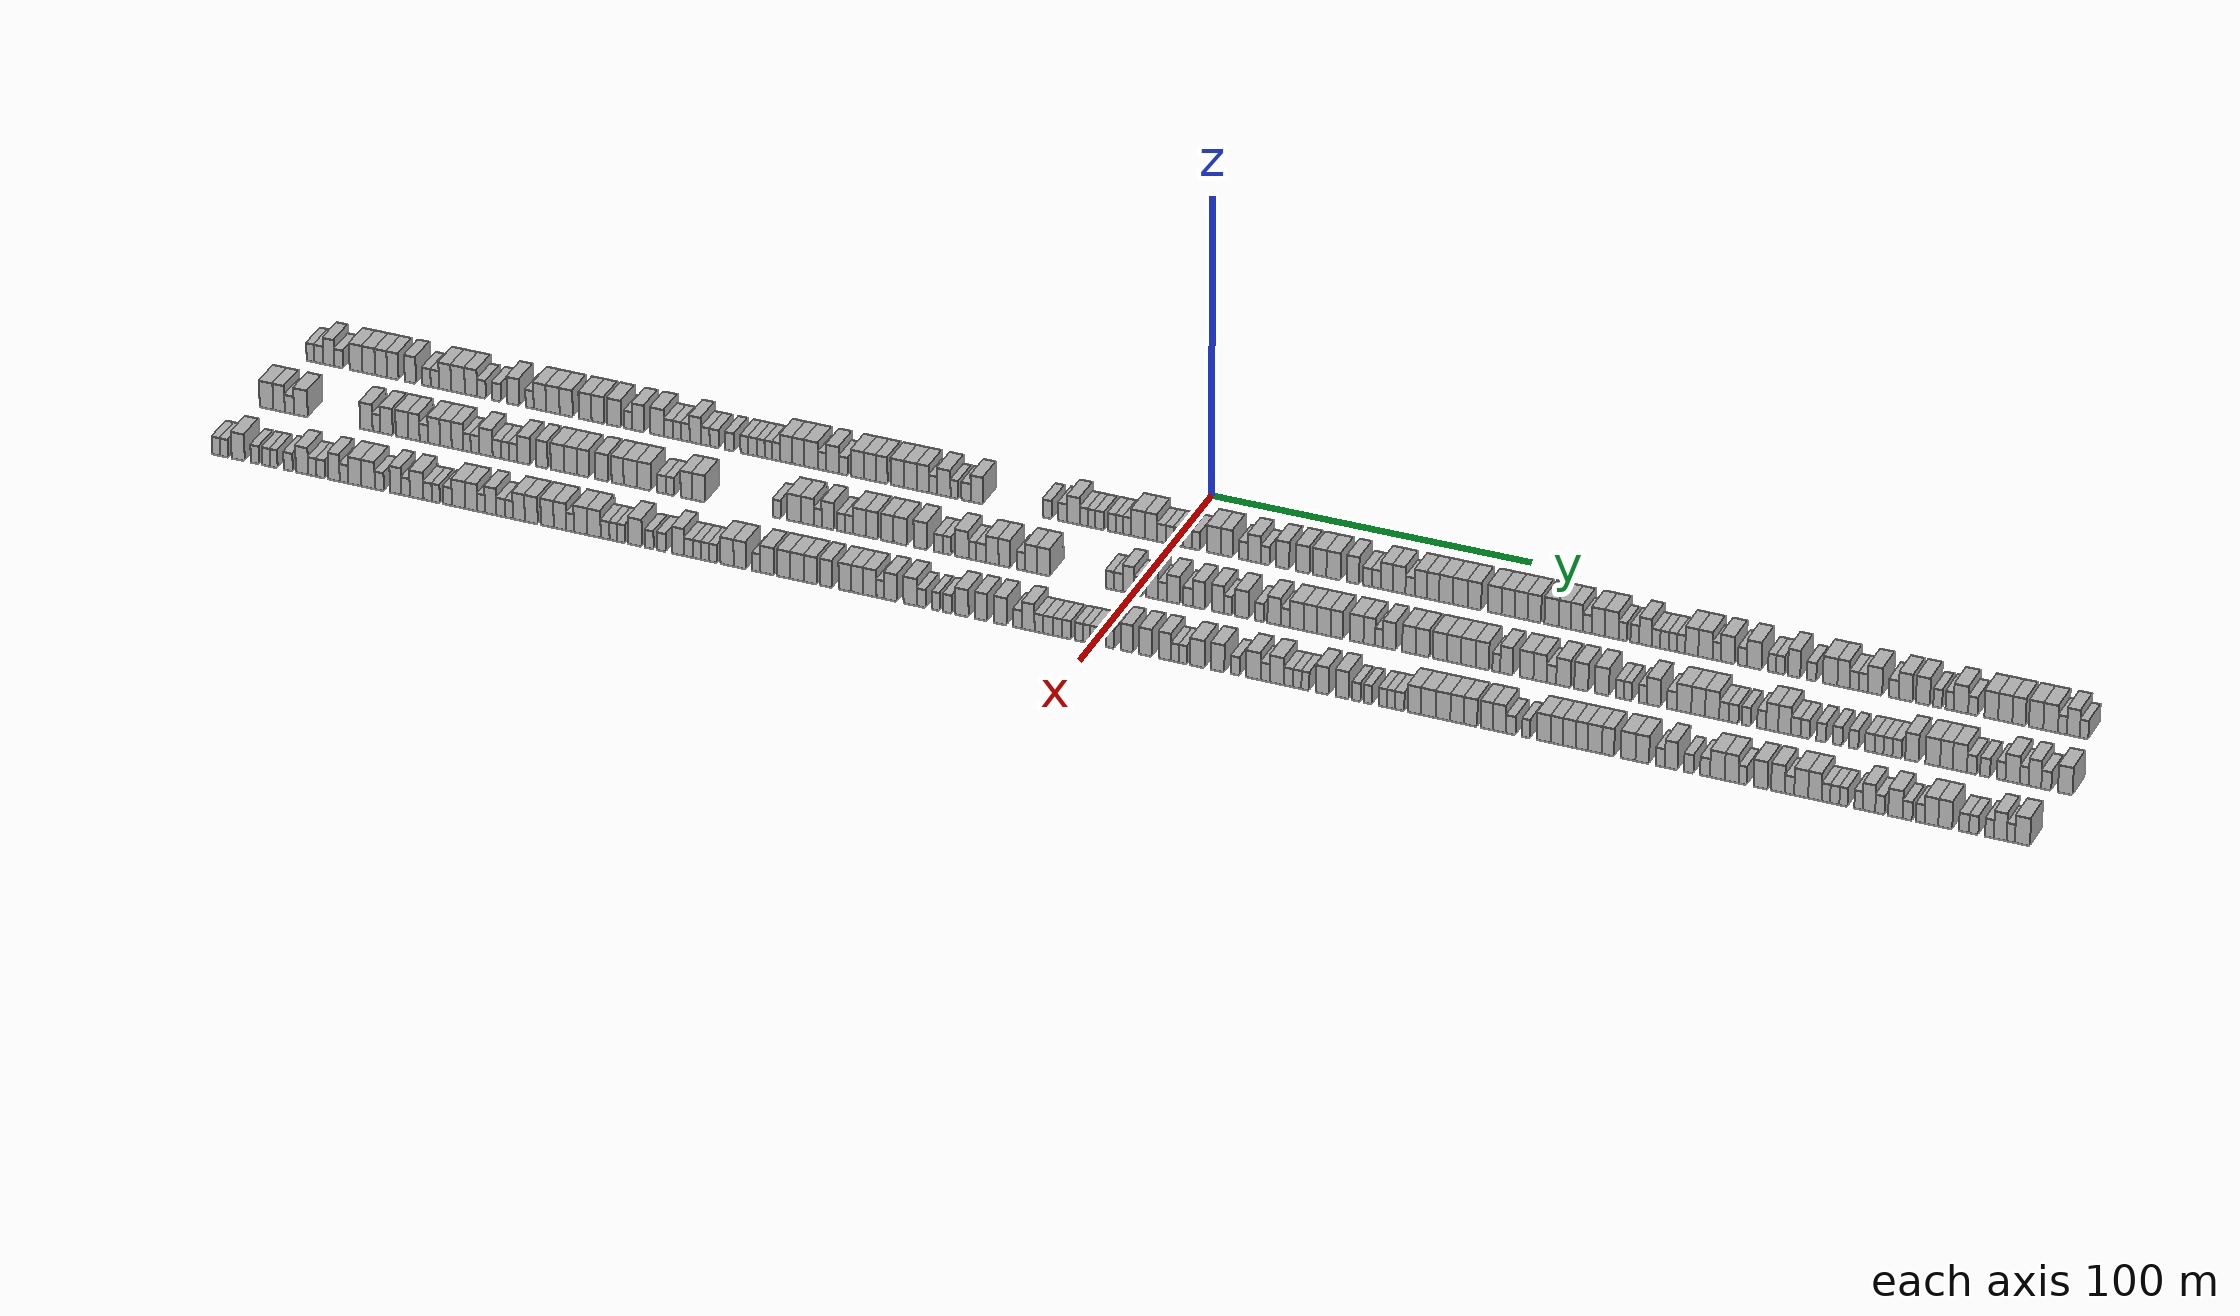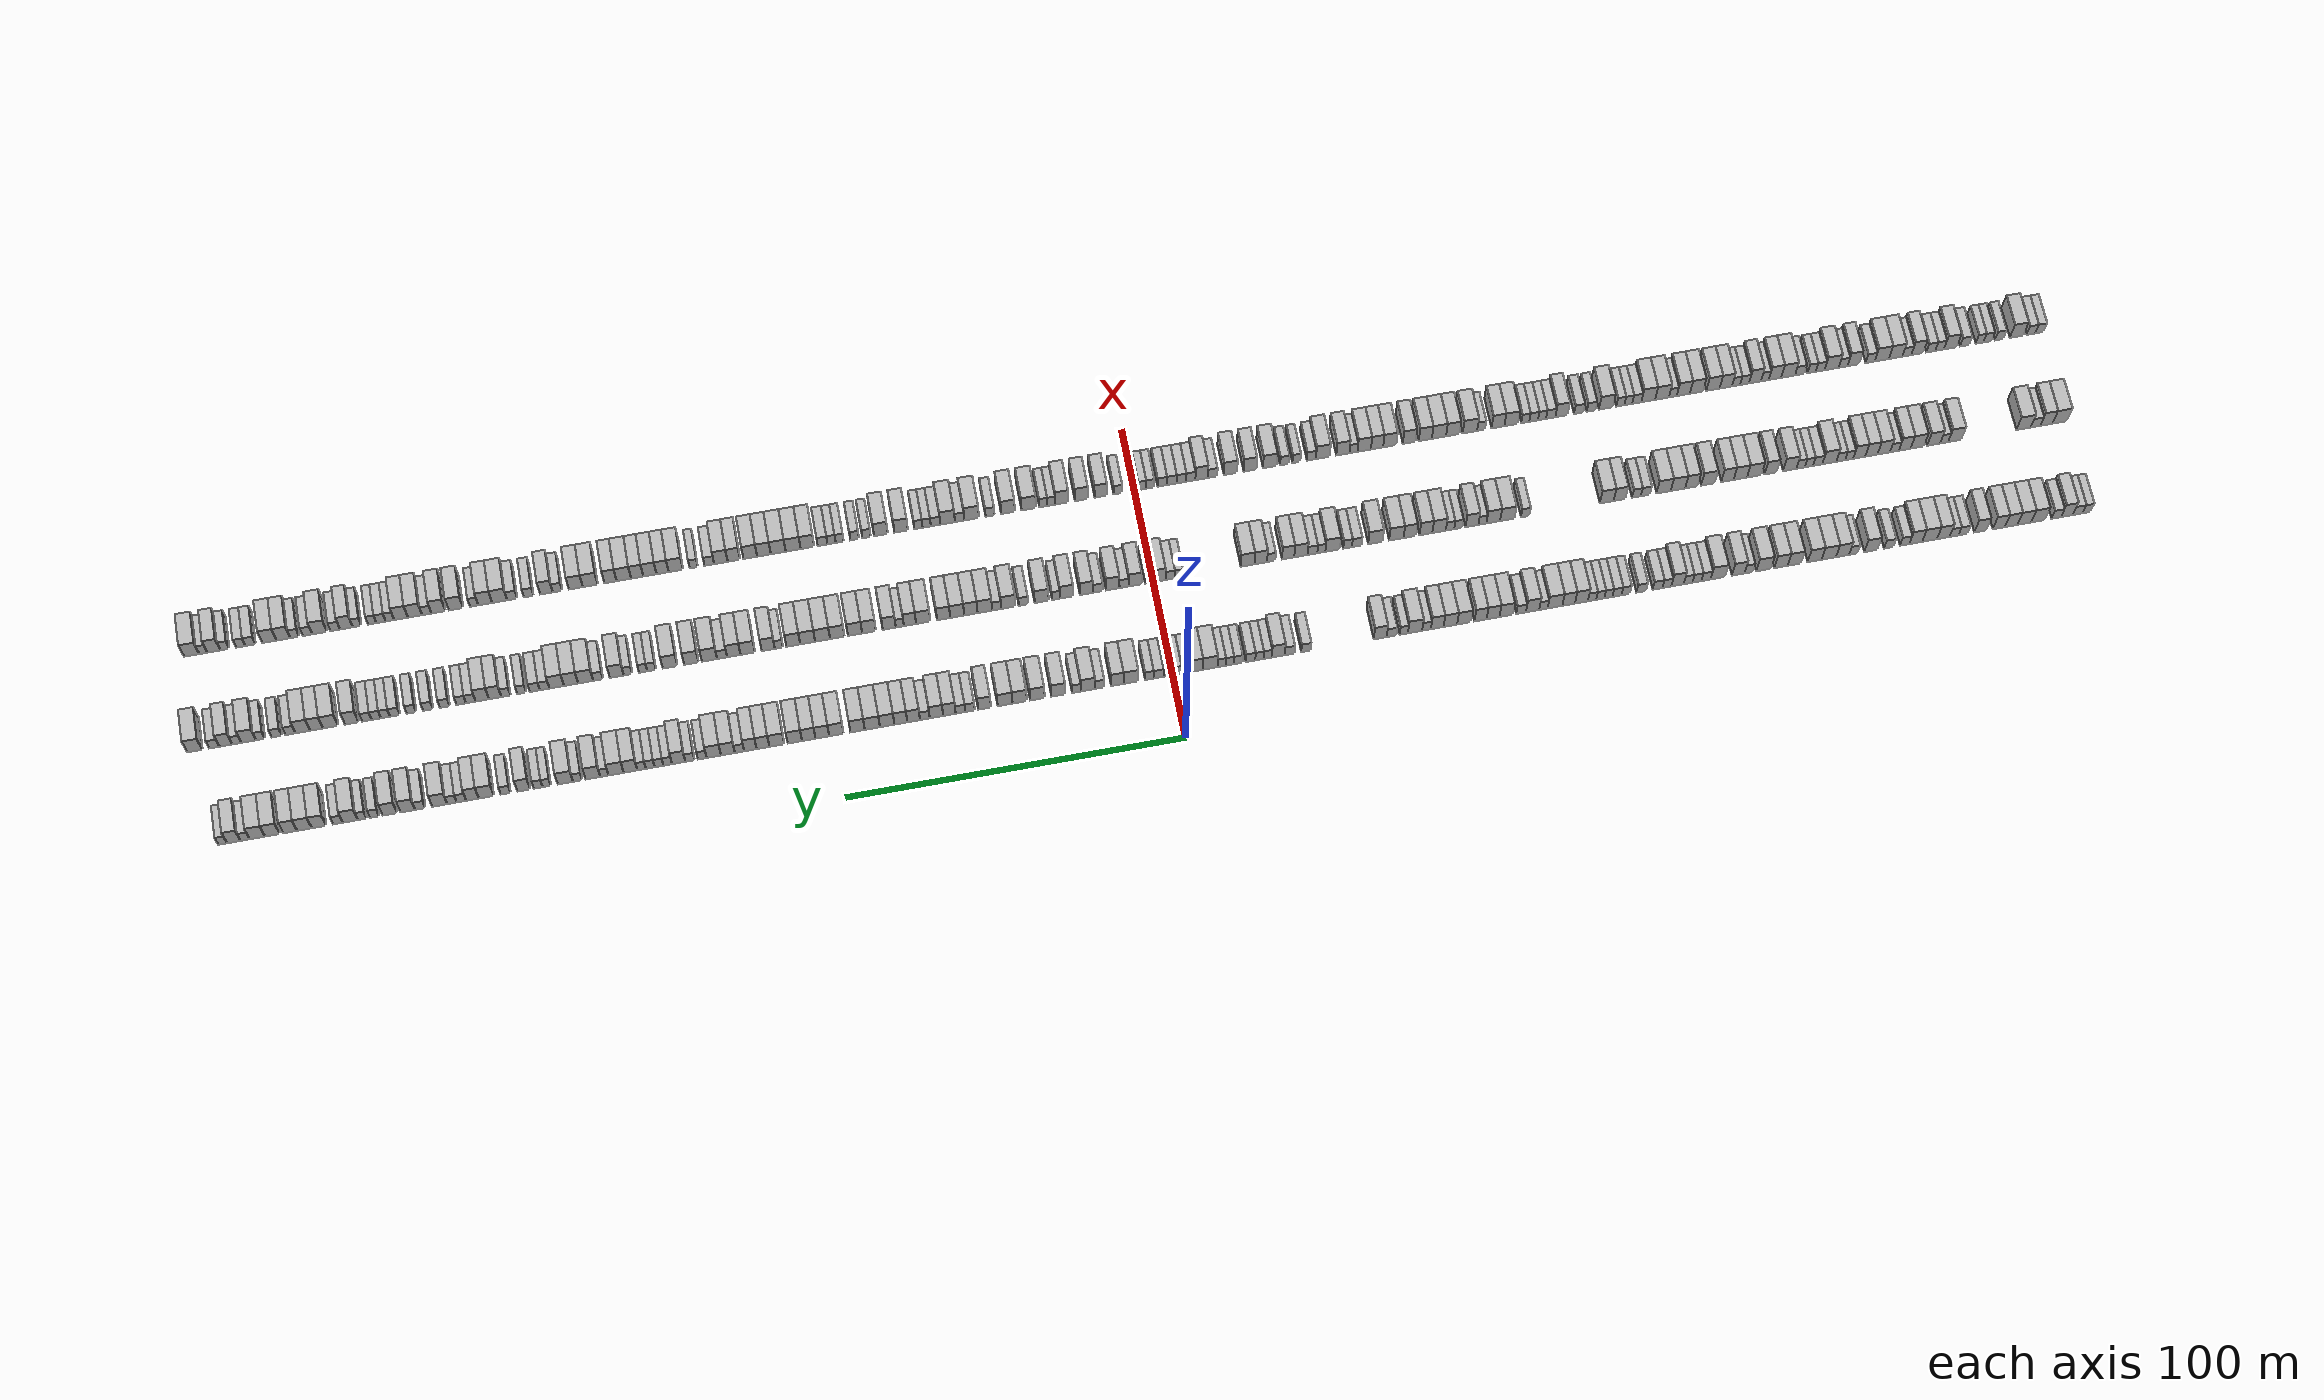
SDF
<sdf version="1.6">
 <world name="default">
  <scene>
   <sky><clouds><speed>12</speed></clouds></sky>
   <ambient>0.4 0.4 0.4 1</ambient>
   <background>0.7 0.7 0.7 1</background>
   <shadows>1</shadows>
  </scene>
  <gravity>0 0 -9.8066</gravity>
  <magnetic_field>6e-06 2.3e-05 -4.2e-05</magnetic_field>
  <physics default="0" name="default_physics" type="ode">
   <ode>
    <solver>
     <type>quick</type>
     <iters>10</iters>
     <sor>1.0</sor>
     <use_dynamic_moi_rescaling>0</use_dynamic_moi_rescaling>
    </solver>
    <constraints>
     <cfm>0</cfm>
     <erp>0.2</erp>
     <contact_max_correcting_vel>100</contact_max_correcting_vel>
     <contact_surface_layer>0.001</contact_surface_layer>
    </constraints>
   </ode>
   <max_step_size>0.004</max_step_size>
   <real_time_factor>1</real_time_factor>
   <real_time_update_rate>250</real_time_update_rate>
  </physics>
  <light name="sun" type="directional">
   <pose>0 0 10 0 0 0</pose>
   <diffuse>0.8 0.8 0.8 1</diffuse>
   <specular>0.2 0.2 0.2 1</specular>
   <attenuation>
    <range>1000</range>
    <constant>0.9</constant>
    <linear>0.01</linear>
    <quadratic>0.001</quadratic>
   </attenuation>
   <direction>-0.5 0.1 -0.9</direction>
  </light>
  <model name="building_1">
   <static>1</static>
   <pose>25.0000 -276.7724 0 0.000000 0.000000 0.000000</pose>
   <link name="link">
    <pose>0 0 3.00 0 0 0</pose>
    <collision name="collision"><geometry><box><size>10.0000 2.4551 6.0000</size></box></geometry></collision>
    <visual name="visual">
     <cast_shadows>0</cast_shadows>
     <geometry><box><size>10.0000 2.4551 6.0000</size></box></geometry>
     <material>
      <script>
       <uri>model://HANNAS_wall/materials/scripts</uri>
       <uri>model://HANNAS_wall/materials/textures</uri>
       <name>vrc/HANNAS_wall</name>
      </script>
     </material>
    </visual>
   </link>
  </model>
  <model name="building_2">
   <static>1</static>
   <pose>25.0000 -274.0450 0 0.000000 0.000000 0.000000</pose>
   <link name="link">
    <pose>0 0 3.00 0 0 0</pose>
    <collision name="collision"><geometry><box><size>10.0000 2.9998 6.0000</size></box></geometry></collision>
    <visual name="visual">
     <cast_shadows>0</cast_shadows>
     <geometry><box><size>10.0000 2.9998 6.0000</size></box></geometry>
     <material>
      <script>
       <uri>model://HANNAS_wall/materials/scripts</uri>
       <uri>model://HANNAS_wall/materials/textures</uri>
       <name>vrc/HANNAS_wall</name>
      </script>
     </material>
    </visual>
   </link>
  </model>
  <model name="building_3">
   <static>1</static>
   <pose>25.0000 -270.7300 0 0.000000 0.000000 0.000000</pose>
   <link name="link">
    <pose>0 0 4.50 0 0 0</pose>
    <collision name="collision"><geometry><box><size>10.0000 3.6301 9.0000</size></box></geometry></collision>
    <visual name="visual">
     <cast_shadows>0</cast_shadows>
     <geometry><box><size>10.0000 3.6301 9.0000</size></box></geometry>
     <material>
      <script>
       <uri>model://HANNAS_wall/materials/scripts</uri>
       <uri>model://HANNAS_wall/materials/textures</uri>
       <name>vrc/HANNAS_wall</name>
      </script>
     </material>
    </visual>
   </link>
  </model>
  <model name="building_4">
   <static>1</static>
   <pose>25.0000 -267.4291 0 0.000000 0.000000 0.000000</pose>
   <link name="link">
    <pose>0 0 3.00 0 0 0</pose>
    <collision name="collision"><geometry><box><size>10.0000 2.9718 6.0000</size></box></geometry></collision>
    <visual name="visual">
     <cast_shadows>0</cast_shadows>
     <geometry><box><size>10.0000 2.9718 6.0000</size></box></geometry>
     <material>
      <script>
       <uri>model://HANNAS_wall/materials/scripts</uri>
       <uri>model://HANNAS_wall/materials/textures</uri>
       <name>vrc/HANNAS_wall</name>
      </script>
     </material>
    </visual>
   </link>
  </model>
  <model name="building_5">
   <static>1</static>
   <pose>25.0000 -261.8477 0 0.000000 0.000000 0.000000</pose>
   <link name="link">
    <pose>0 0 4.50 0 0 0</pose>
    <collision name="collision"><geometry><box><size>10.0000 4.1910 9.0000</size></box></geometry></collision>
    <visual name="visual">
     <cast_shadows>0</cast_shadows>
     <geometry><box><size>10.0000 4.1910 9.0000</size></box></geometry>
     <material>
      <script>
       <uri>model://HANNAS_wall/materials/scripts</uri>
       <uri>model://HANNAS_wall/materials/textures</uri>
       <name>vrc/HANNAS_wall</name>
      </script>
     </material>
    </visual>
   </link>
  </model>
  <model name="building_6">
   <static>1</static>
   <pose>25.0000 -257.6668 0 0.000000 0.000000 0.000000</pose>
   <link name="link">
    <pose>0 0 4.50 0 0 0</pose>
    <collision name="collision"><geometry><box><size>10.0000 4.1707 9.0000</size></box></geometry></collision>
    <visual name="visual">
     <cast_shadows>0</cast_shadows>
     <geometry><box><size>10.0000 4.1707 9.0000</size></box></geometry>
     <material>
      <script>
       <uri>model://HANNAS_wall/materials/scripts</uri>
       <uri>model://HANNAS_wall/materials/textures</uri>
       <name>vrc/HANNAS_wall</name>
      </script>
     </material>
    </visual>
   </link>
  </model>
  <model name="building_7">
   <static>1</static>
   <pose>25.0000 -253.6388 0 0.000000 0.000000 0.000000</pose>
   <link name="link">
    <pose>0 0 4.50 0 0 0</pose>
    <collision name="collision"><geometry><box><size>10.0000 3.8853 9.0000</size></box></geometry></collision>
    <visual name="visual">
     <cast_shadows>0</cast_shadows>
     <geometry><box><size>10.0000 3.8853 9.0000</size></box></geometry>
     <material>
      <script>
       <uri>model://HANNAS_wall/materials/scripts</uri>
       <uri>model://HANNAS_wall/materials/textures</uri>
       <name>vrc/HANNAS_wall</name>
      </script>
     </material>
    </visual>
   </link>
  </model>
  <model name="building_8">
   <static>1</static>
   <pose>25.0000 -249.8201 0 0.000000 0.000000 0.000000</pose>
   <link name="link">
    <pose>0 0 4.50 0 0 0</pose>
    <collision name="collision"><geometry><box><size>10.0000 3.7521 9.0000</size></box></geometry></collision>
    <visual name="visual">
     <cast_shadows>0</cast_shadows>
     <geometry><box><size>10.0000 3.7521 9.0000</size></box></geometry>
     <material>
      <script>
       <uri>model://HANNAS_wall/materials/scripts</uri>
       <uri>model://HANNAS_wall/materials/textures</uri>
       <name>vrc/HANNAS_wall</name>
      </script>
     </material>
    </visual>
   </link>
  </model>
  <model name="building_9">
   <static>1</static>
   <pose>25.0000 -244.1011 0 0.000000 0.000000 0.000000</pose>
   <link name="link">
    <pose>0 0 4.50 0 0 0</pose>
    <collision name="collision"><geometry><box><size>10.0000 3.6858 9.0000</size></box></geometry></collision>
    <visual name="visual">
     <cast_shadows>0</cast_shadows>
     <geometry><box><size>10.0000 3.6858 9.0000</size></box></geometry>
     <material>
      <script>
       <uri>model://HANNAS_wall/materials/scripts</uri>
       <uri>model://HANNAS_wall/materials/textures</uri>
       <name>vrc/HANNAS_wall</name>
      </script>
     </material>
    </visual>
   </link>
  </model>
  <model name="building_10">
   <static>1</static>
   <pose>25.0000 -238.8640 0 0.000000 0.000000 0.000000</pose>
   <link name="link">
    <pose>0 0 3.00 0 0 0</pose>
    <collision name="collision"><geometry><box><size>10.0000 2.7885 6.0000</size></box></geometry></collision>
    <visual name="visual">
     <cast_shadows>0</cast_shadows>
     <geometry><box><size>10.0000 2.7885 6.0000</size></box></geometry>
     <material>
      <script>
       <uri>model://HANNAS_wall/materials/scripts</uri>
       <uri>model://HANNAS_wall/materials/textures</uri>
       <name>vrc/HANNAS_wall</name>
      </script>
     </material>
    </visual>
   </link>
  </model>
  <model name="building_11">
   <static>1</static>
   <pose>25.0000 -236.1084 0 0.000000 0.000000 0.000000</pose>
   <link name="link">
    <pose>0 0 3.00 0 0 0</pose>
    <collision name="collision"><geometry><box><size>10.0000 2.7226 6.0000</size></box></geometry></collision>
    <visual name="visual">
     <cast_shadows>0</cast_shadows>
     <geometry><box><size>10.0000 2.7226 6.0000</size></box></geometry>
     <material>
      <script>
       <uri>model://HANNAS_wall/materials/scripts</uri>
       <uri>model://HANNAS_wall/materials/textures</uri>
       <name>vrc/HANNAS_wall</name>
      </script>
     </material>
    </visual>
   </link>
  </model>
  <model name="building_12">
   <static>1</static>
   <pose>25.0000 -232.7931 0 0.000000 0.000000 0.000000</pose>
   <link name="link">
    <pose>0 0 4.50 0 0 0</pose>
    <collision name="collision"><geometry><box><size>10.0000 3.9082 9.0000</size></box></geometry></collision>
    <visual name="visual">
     <cast_shadows>0</cast_shadows>
     <geometry><box><size>10.0000 3.9082 9.0000</size></box></geometry>
     <material>
      <script>
       <uri>model://HANNAS_wall/materials/scripts</uri>
       <uri>model://HANNAS_wall/materials/textures</uri>
       <name>vrc/HANNAS_wall</name>
      </script>
     </material>
    </visual>
   </link>
  </model>
  <model name="building_13">
   <static>1</static>
   <pose>25.0000 -228.5908 0 0.000000 0.000000 0.000000</pose>
   <link name="link">
    <pose>0 0 4.50 0 0 0</pose>
    <collision name="collision"><geometry><box><size>10.0000 4.4964 9.0000</size></box></geometry></collision>
    <visual name="visual">
     <cast_shadows>0</cast_shadows>
     <geometry><box><size>10.0000 4.4964 9.0000</size></box></geometry>
     <material>
      <script>
       <uri>model://HANNAS_wall/materials/scripts</uri>
       <uri>model://HANNAS_wall/materials/textures</uri>
       <name>vrc/HANNAS_wall</name>
      </script>
     </material>
    </visual>
   </link>
  </model>
  <model name="building_14">
   <static>1</static>
   <pose>25.0000 -224.3549 0 0.000000 0.000000 0.000000</pose>
   <link name="link">
    <pose>0 0 4.50 0 0 0</pose>
    <collision name="collision"><geometry><box><size>10.0000 3.9754 9.0000</size></box></geometry></collision>
    <visual name="visual">
     <cast_shadows>0</cast_shadows>
     <geometry><box><size>10.0000 3.9754 9.0000</size></box></geometry>
     <material>
      <script>
       <uri>model://HANNAS_wall/materials/scripts</uri>
       <uri>model://HANNAS_wall/materials/textures</uri>
       <name>vrc/HANNAS_wall</name>
      </script>
     </material>
    </visual>
   </link>
  </model>
  <model name="building_15">
   <static>1</static>
   <pose>25.0000 -220.9475 0 0.000000 0.000000 0.000000</pose>
   <link name="link">
    <pose>0 0 3.00 0 0 0</pose>
    <collision name="collision"><geometry><box><size>10.0000 2.8393 6.0000</size></box></geometry></collision>
    <visual name="visual">
     <cast_shadows>0</cast_shadows>
     <geometry><box><size>10.0000 2.8393 6.0000</size></box></geometry>
     <material>
      <script>
       <uri>model://HANNAS_wall/materials/scripts</uri>
       <uri>model://HANNAS_wall/materials/textures</uri>
       <name>vrc/HANNAS_wall</name>
      </script>
     </material>
    </visual>
   </link>
  </model>
  <model name="building_16">
   <static>1</static>
   <pose>25.0000 -216.0794 0 0.000000 0.000000 0.000000</pose>
   <link name="link">
    <pose>0 0 3.00 0 0 0</pose>
    <collision name="collision"><geometry><box><size>10.0000 2.8969 6.0000</size></box></geometry></collision>
    <visual name="visual">
     <cast_shadows>0</cast_shadows>
     <geometry><box><size>10.0000 2.8969 6.0000</size></box></geometry>
     <material>
      <script>
       <uri>model://HANNAS_wall/materials/scripts</uri>
       <uri>model://HANNAS_wall/materials/textures</uri>
       <name>vrc/HANNAS_wall</name>
      </script>
     </material>
    </visual>
   </link>
  </model>
  <model name="building_17">
   <static>1</static>
   <pose>25.0000 -210.6145 0 0.000000 0.000000 0.000000</pose>
   <link name="link">
    <pose>0 0 4.50 0 0 0</pose>
    <collision name="collision"><geometry><box><size>10.0000 4.0329 9.0000</size></box></geometry></collision>
    <visual name="visual">
     <cast_shadows>0</cast_shadows>
     <geometry><box><size>10.0000 4.0329 9.0000</size></box></geometry>
     <material>
      <script>
       <uri>model://HANNAS_wall/materials/scripts</uri>
       <uri>model://HANNAS_wall/materials/textures</uri>
       <name>vrc/HANNAS_wall</name>
      </script>
     </material>
    </visual>
   </link>
  </model>
  <model name="building_18">
   <static>1</static>
   <pose>25.0000 -205.2983 0 0.000000 0.000000 0.000000</pose>
   <link name="link">
    <pose>0 0 3.00 0 0 0</pose>
    <collision name="collision"><geometry><box><size>10.0000 2.5995 6.0000</size></box></geometry></collision>
    <visual name="visual">
     <cast_shadows>0</cast_shadows>
     <geometry><box><size>10.0000 2.5995 6.0000</size></box></geometry>
     <material>
      <script>
       <uri>model://HANNAS_wall/materials/scripts</uri>
       <uri>model://HANNAS_wall/materials/textures</uri>
       <name>vrc/HANNAS_wall</name>
      </script>
     </material>
    </visual>
   </link>
  </model>
  <model name="building_19">
   <static>1</static>
   <pose>25.0000 -202.0076 0 0.000000 0.000000 0.000000</pose>
   <link name="link">
    <pose>0 0 4.50 0 0 0</pose>
    <collision name="collision"><geometry><box><size>10.0000 3.9819 9.0000</size></box></geometry></collision>
    <visual name="visual">
     <cast_shadows>0</cast_shadows>
     <geometry><box><size>10.0000 3.9819 9.0000</size></box></geometry>
     <material>
      <script>
       <uri>model://HANNAS_wall/materials/scripts</uri>
       <uri>model://HANNAS_wall/materials/textures</uri>
       <name>vrc/HANNAS_wall</name>
      </script>
     </material>
    </visual>
   </link>
  </model>
  <model name="building_20">
   <static>1</static>
   <pose>25.0000 -197.8102 0 0.000000 0.000000 0.000000</pose>
   <link name="link">
    <pose>0 0 4.50 0 0 0</pose>
    <collision name="collision"><geometry><box><size>10.0000 4.4129 9.0000</size></box></geometry></collision>
    <visual name="visual">
     <cast_shadows>0</cast_shadows>
     <geometry><box><size>10.0000 4.4129 9.0000</size></box></geometry>
     <material>
      <script>
       <uri>model://HANNAS_wall/materials/scripts</uri>
       <uri>model://HANNAS_wall/materials/textures</uri>
       <name>vrc/HANNAS_wall</name>
      </script>
     </material>
    </visual>
   </link>
  </model>
  <model name="building_21">
   <static>1</static>
   <pose>25.0000 -193.4685 0 0.000000 0.000000 0.000000</pose>
   <link name="link">
    <pose>0 0 4.50 0 0 0</pose>
    <collision name="collision"><geometry><box><size>10.0000 4.2705 9.0000</size></box></geometry></collision>
    <visual name="visual">
     <cast_shadows>0</cast_shadows>
     <geometry><box><size>10.0000 4.2705 9.0000</size></box></geometry>
     <material>
      <script>
       <uri>model://HANNAS_wall/materials/scripts</uri>
       <uri>model://HANNAS_wall/materials/textures</uri>
       <name>vrc/HANNAS_wall</name>
      </script>
     </material>
    </visual>
   </link>
  </model>
  <model name="building_22">
   <static>1</static>
   <pose>25.0000 -187.3111 0 0.000000 0.000000 0.000000</pose>
   <link name="link">
    <pose>0 0 4.50 0 0 0</pose>
    <collision name="collision"><geometry><box><size>10.0000 4.0444 9.0000</size></box></geometry></collision>
    <visual name="visual">
     <cast_shadows>0</cast_shadows>
     <geometry><box><size>10.0000 4.0444 9.0000</size></box></geometry>
     <material>
      <script>
       <uri>model://HANNAS_wall/materials/scripts</uri>
       <uri>model://HANNAS_wall/materials/textures</uri>
       <name>vrc/HANNAS_wall</name>
      </script>
     </material>
    </visual>
   </link>
  </model>
  <model name="building_23">
   <static>1</static>
   <pose>25.0000 -183.2346 0 0.000000 0.000000 0.000000</pose>
   <link name="link">
    <pose>0 0 4.50 0 0 0</pose>
    <collision name="collision"><geometry><box><size>10.0000 4.1086 9.0000</size></box></geometry></collision>
    <visual name="visual">
     <cast_shadows>0</cast_shadows>
     <geometry><box><size>10.0000 4.1086 9.0000</size></box></geometry>
     <material>
      <script>
       <uri>model://HANNAS_wall/materials/scripts</uri>
       <uri>model://HANNAS_wall/materials/textures</uri>
       <name>vrc/HANNAS_wall</name>
      </script>
     </material>
    </visual>
   </link>
  </model>
  <model name="building_24">
   <static>1</static>
   <pose>25.0000 -177.9392 0 0.000000 0.000000 0.000000</pose>
   <link name="link">
    <pose>0 0 4.50 0 0 0</pose>
    <collision name="collision"><geometry><box><size>10.0000 4.4822 9.0000</size></box></geometry></collision>
    <visual name="visual">
     <cast_shadows>0</cast_shadows>
     <geometry><box><size>10.0000 4.4822 9.0000</size></box></geometry>
     <material>
      <script>
       <uri>model://HANNAS_wall/materials/scripts</uri>
       <uri>model://HANNAS_wall/materials/textures</uri>
       <name>vrc/HANNAS_wall</name>
      </script>
     </material>
    </visual>
   </link>
  </model>
  <model name="building_25">
   <static>1</static>
   <pose>25.0000 -173.4259 0 0.000000 0.000000 0.000000</pose>
   <link name="link">
    <pose>0 0 3.00 0 0 0</pose>
    <collision name="collision"><geometry><box><size>10.0000 2.5444 6.0000</size></box></geometry></collision>
    <visual name="visual">
     <cast_shadows>0</cast_shadows>
     <geometry><box><size>10.0000 2.5444 6.0000</size></box></geometry>
     <material>
      <script>
       <uri>model://HANNAS_wall/materials/scripts</uri>
       <uri>model://HANNAS_wall/materials/textures</uri>
       <name>vrc/HANNAS_wall</name>
      </script>
     </material>
    </visual>
   </link>
  </model>
  <model name="building_26">
   <static>1</static>
   <pose>25.0000 -170.2114 0 0.000000 0.000000 0.000000</pose>
   <link name="link">
    <pose>0 0 4.50 0 0 0</pose>
    <collision name="collision"><geometry><box><size>10.0000 3.8845 9.0000</size></box></geometry></collision>
    <visual name="visual">
     <cast_shadows>0</cast_shadows>
     <geometry><box><size>10.0000 3.8845 9.0000</size></box></geometry>
     <material>
      <script>
       <uri>model://HANNAS_wall/materials/scripts</uri>
       <uri>model://HANNAS_wall/materials/textures</uri>
       <name>vrc/HANNAS_wall</name>
      </script>
     </material>
    </visual>
   </link>
  </model>
  <model name="building_27">
   <static>1</static>
   <pose>25.0000 -164.0716 0 0.000000 0.000000 0.000000</pose>
   <link name="link">
    <pose>0 0 4.50 0 0 0</pose>
    <collision name="collision"><geometry><box><size>10.0000 4.3951 9.0000</size></box></geometry></collision>
    <visual name="visual">
     <cast_shadows>0</cast_shadows>
     <geometry><box><size>10.0000 4.3951 9.0000</size></box></geometry>
     <material>
      <script>
       <uri>model://HANNAS_wall/materials/scripts</uri>
       <uri>model://HANNAS_wall/materials/textures</uri>
       <name>vrc/HANNAS_wall</name>
      </script>
     </material>
    </visual>
   </link>
  </model>
  <model name="building_28">
   <static>1</static>
   <pose>25.0000 -160.4498 0 0.000000 0.000000 0.000000</pose>
   <link name="link">
    <pose>0 0 3.00 0 0 0</pose>
    <collision name="collision"><geometry><box><size>10.0000 2.8483 6.0000</size></box></geometry></collision>
    <visual name="visual">
     <cast_shadows>0</cast_shadows>
     <geometry><box><size>10.0000 2.8483 6.0000</size></box></geometry>
     <material>
      <script>
       <uri>model://HANNAS_wall/materials/scripts</uri>
       <uri>model://HANNAS_wall/materials/textures</uri>
       <name>vrc/HANNAS_wall</name>
      </script>
     </material>
    </visual>
   </link>
  </model>
  <model name="building_29">
   <static>1</static>
   <pose>25.0000 -157.6659 0 0.000000 0.000000 0.000000</pose>
   <link name="link">
    <pose>0 0 3.00 0 0 0</pose>
    <collision name="collision"><geometry><box><size>10.0000 2.7195 6.0000</size></box></geometry></collision>
    <visual name="visual">
     <cast_shadows>0</cast_shadows>
     <geometry><box><size>10.0000 2.7195 6.0000</size></box></geometry>
     <material>
      <script>
       <uri>model://HANNAS_wall/materials/scripts</uri>
       <uri>model://HANNAS_wall/materials/textures</uri>
       <name>vrc/HANNAS_wall</name>
      </script>
     </material>
    </visual>
   </link>
  </model>
  <model name="building_30">
   <static>1</static>
   <pose>25.0000 -154.9750 0 0.000000 0.000000 0.000000</pose>
   <link name="link">
    <pose>0 0 3.00 0 0 0</pose>
    <collision name="collision"><geometry><box><size>10.0000 2.6625 6.0000</size></box></geometry></collision>
    <visual name="visual">
     <cast_shadows>0</cast_shadows>
     <geometry><box><size>10.0000 2.6625 6.0000</size></box></geometry>
     <material>
      <script>
       <uri>model://HANNAS_wall/materials/scripts</uri>
       <uri>model://HANNAS_wall/materials/textures</uri>
       <name>vrc/HANNAS_wall</name>
      </script>
     </material>
    </visual>
   </link>
  </model>
  <model name="building_31">
   <static>1</static>
   <pose>25.0000 -151.7612 0 0.000000 0.000000 0.000000</pose>
   <link name="link">
    <pose>0 0 4.50 0 0 0</pose>
    <collision name="collision"><geometry><box><size>10.0000 3.7650 9.0000</size></box></geometry></collision>
    <visual name="visual">
     <cast_shadows>0</cast_shadows>
     <geometry><box><size>10.0000 3.7650 9.0000</size></box></geometry>
     <material>
      <script>
       <uri>model://HANNAS_wall/materials/scripts</uri>
       <uri>model://HANNAS_wall/materials/textures</uri>
       <name>vrc/HANNAS_wall</name>
      </script>
     </material>
    </visual>
   </link>
  </model>
  <model name="building_32">
   <static>1</static>
   <pose>25.0000 -148.5566 0 0.000000 0.000000 0.000000</pose>
   <link name="link">
    <pose>0 0 3.00 0 0 0</pose>
    <collision name="collision"><geometry><box><size>10.0000 2.6443 6.0000</size></box></geometry></collision>
    <visual name="visual">
     <cast_shadows>0</cast_shadows>
     <geometry><box><size>10.0000 2.6443 6.0000</size></box></geometry>
     <material>
      <script>
       <uri>model://HANNAS_wall/materials/scripts</uri>
       <uri>model://HANNAS_wall/materials/textures</uri>
       <name>vrc/HANNAS_wall</name>
      </script>
     </material>
    </visual>
   </link>
  </model>
  <model name="building_33">
   <static>1</static>
   <pose>25.0000 -145.7440 0 0.000000 0.000000 0.000000</pose>
   <link name="link">
    <pose>0 0 3.00 0 0 0</pose>
    <collision name="collision"><geometry><box><size>10.0000 2.9810 6.0000</size></box></geometry></collision>
    <visual name="visual">
     <cast_shadows>0</cast_shadows>
     <geometry><box><size>10.0000 2.9810 6.0000</size></box></geometry>
     <material>
      <script>
       <uri>model://HANNAS_wall/materials/scripts</uri>
       <uri>model://HANNAS_wall/materials/textures</uri>
       <name>vrc/HANNAS_wall</name>
      </script>
     </material>
    </visual>
   </link>
  </model>
  <model name="building_34">
   <static>1</static>
   <pose>25.0000 -140.7916 0 0.000000 0.000000 0.000000</pose>
   <link name="link">
    <pose>0 0 3.00 0 0 0</pose>
    <collision name="collision"><geometry><box><size>10.0000 2.9238 6.0000</size></box></geometry></collision>
    <visual name="visual">
     <cast_shadows>0</cast_shadows>
     <geometry><box><size>10.0000 2.9238 6.0000</size></box></geometry>
     <material>
      <script>
       <uri>model://HANNAS_wall/materials/scripts</uri>
       <uri>model://HANNAS_wall/materials/textures</uri>
       <name>vrc/HANNAS_wall</name>
      </script>
     </material>
    </visual>
   </link>
  </model>
  <model name="building_35">
   <static>1</static>
   <pose>25.0000 -136.0664 0 0.000000 0.000000 0.000000</pose>
   <link name="link">
    <pose>0 0 3.00 0 0 0</pose>
    <collision name="collision"><geometry><box><size>10.0000 2.5266 6.0000</size></box></geometry></collision>
    <visual name="visual">
     <cast_shadows>0</cast_shadows>
     <geometry><box><size>10.0000 2.5266 6.0000</size></box></geometry>
     <material>
      <script>
       <uri>model://HANNAS_wall/materials/scripts</uri>
       <uri>model://HANNAS_wall/materials/textures</uri>
       <name>vrc/HANNAS_wall</name>
      </script>
     </material>
    </visual>
   </link>
  </model>
  <model name="building_36">
   <static>1</static>
   <pose>25.0000 -133.4076 0 0.000000 0.000000 0.000000</pose>
   <link name="link">
    <pose>0 0 3.00 0 0 0</pose>
    <collision name="collision"><geometry><box><size>10.0000 2.7912 6.0000</size></box></geometry></collision>
    <visual name="visual">
     <cast_shadows>0</cast_shadows>
     <geometry><box><size>10.0000 2.7912 6.0000</size></box></geometry>
     <material>
      <script>
       <uri>model://HANNAS_wall/materials/scripts</uri>
       <uri>model://HANNAS_wall/materials/textures</uri>
       <name>vrc/HANNAS_wall</name>
      </script>
     </material>
    </visual>
   </link>
  </model>
  <model name="building_37">
   <static>1</static>
   <pose>25.0000 -130.7990 0 0.000000 0.000000 0.000000</pose>
   <link name="link">
    <pose>0 0 3.00 0 0 0</pose>
    <collision name="collision"><geometry><box><size>10.0000 2.4260 6.0000</size></box></geometry></collision>
    <visual name="visual">
     <cast_shadows>0</cast_shadows>
     <geometry><box><size>10.0000 2.4260 6.0000</size></box></geometry>
     <material>
      <script>
       <uri>model://HANNAS_wall/materials/scripts</uri>
       <uri>model://HANNAS_wall/materials/textures</uri>
       <name>vrc/HANNAS_wall</name>
      </script>
     </material>
    </visual>
   </link>
  </model>
  <model name="building_38">
   <static>1</static>
   <pose>25.0000 -128.3628 0 0.000000 0.000000 0.000000</pose>
   <link name="link">
    <pose>0 0 3.00 0 0 0</pose>
    <collision name="collision"><geometry><box><size>10.0000 2.4464 6.0000</size></box></geometry></collision>
    <visual name="visual">
     <cast_shadows>0</cast_shadows>
     <geometry><box><size>10.0000 2.4464 6.0000</size></box></geometry>
     <material>
      <script>
       <uri>model://HANNAS_wall/materials/scripts</uri>
       <uri>model://HANNAS_wall/materials/textures</uri>
       <name>vrc/HANNAS_wall</name>
      </script>
     </material>
    </visual>
   </link>
  </model>
  <model name="building_39">
   <static>1</static>
   <pose>25.0000 -125.8921 0 0.000000 0.000000 0.000000</pose>
   <link name="link">
    <pose>0 0 3.00 0 0 0</pose>
    <collision name="collision"><geometry><box><size>10.0000 2.4951 6.0000</size></box></geometry></collision>
    <visual name="visual">
     <cast_shadows>0</cast_shadows>
     <geometry><box><size>10.0000 2.4951 6.0000</size></box></geometry>
     <material>
      <script>
       <uri>model://HANNAS_wall/materials/scripts</uri>
       <uri>model://HANNAS_wall/materials/textures</uri>
       <name>vrc/HANNAS_wall</name>
      </script>
     </material>
    </visual>
   </link>
  </model>
  <model name="building_40">
   <static>1</static>
   <pose>25.0000 -122.6725 0 0.000000 0.000000 0.000000</pose>
   <link name="link">
    <pose>0 0 4.50 0 0 0</pose>
    <collision name="collision"><geometry><box><size>10.0000 3.9441 9.0000</size></box></geometry></collision>
    <visual name="visual">
     <cast_shadows>0</cast_shadows>
     <geometry><box><size>10.0000 3.9441 9.0000</size></box></geometry>
     <material>
      <script>
       <uri>model://HANNAS_wall/materials/scripts</uri>
       <uri>model://HANNAS_wall/materials/textures</uri>
       <name>vrc/HANNAS_wall</name>
      </script>
     </material>
    </visual>
   </link>
  </model>
  <model name="building_41">
   <static>1</static>
   <pose>25.0000 -118.8062 0 0.000000 0.000000 0.000000</pose>
   <link name="link">
    <pose>0 0 4.50 0 0 0</pose>
    <collision name="collision"><geometry><box><size>10.0000 3.7884 9.0000</size></box></geometry></collision>
    <visual name="visual">
     <cast_shadows>0</cast_shadows>
     <geometry><box><size>10.0000 3.7884 9.0000</size></box></geometry>
     <material>
      <script>
       <uri>model://HANNAS_wall/materials/scripts</uri>
       <uri>model://HANNAS_wall/materials/textures</uri>
       <name>vrc/HANNAS_wall</name>
      </script>
     </material>
    </visual>
   </link>
  </model>
  <model name="building_42">
   <static>1</static>
   <pose>25.0000 -114.6699 0 0.000000 0.000000 0.000000</pose>
   <link name="link">
    <pose>0 0 4.50 0 0 0</pose>
    <collision name="collision"><geometry><box><size>10.0000 4.4842 9.0000</size></box></geometry></collision>
    <visual name="visual">
     <cast_shadows>0</cast_shadows>
     <geometry><box><size>10.0000 4.4842 9.0000</size></box></geometry>
     <material>
      <script>
       <uri>model://HANNAS_wall/materials/scripts</uri>
       <uri>model://HANNAS_wall/materials/textures</uri>
       <name>vrc/HANNAS_wall</name>
      </script>
     </material>
    </visual>
   </link>
  </model>
  <model name="building_43">
   <static>1</static>
   <pose>25.0000 -111.1604 0 0.000000 0.000000 0.000000</pose>
   <link name="link">
    <pose>0 0 3.00 0 0 0</pose>
    <collision name="collision"><geometry><box><size>10.0000 2.5348 6.0000</size></box></geometry></collision>
    <visual name="visual">
     <cast_shadows>0</cast_shadows>
     <geometry><box><size>10.0000 2.5348 6.0000</size></box></geometry>
     <material>
      <script>
       <uri>model://HANNAS_wall/materials/scripts</uri>
       <uri>model://HANNAS_wall/materials/textures</uri>
       <name>vrc/HANNAS_wall</name>
      </script>
     </material>
    </visual>
   </link>
  </model>
  <model name="building_44">
   <static>1</static>
   <pose>25.0000 -107.8823 0 0.000000 0.000000 0.000000</pose>
   <link name="link">
    <pose>0 0 4.50 0 0 0</pose>
    <collision name="collision"><geometry><box><size>10.0000 4.0214 9.0000</size></box></geometry></collision>
    <visual name="visual">
     <cast_shadows>0</cast_shadows>
     <geometry><box><size>10.0000 4.0214 9.0000</size></box></geometry>
     <material>
      <script>
       <uri>model://HANNAS_wall/materials/scripts</uri>
       <uri>model://HANNAS_wall/materials/textures</uri>
       <name>vrc/HANNAS_wall</name>
      </script>
     </material>
    </visual>
   </link>
  </model>
  <model name="building_45">
   <static>1</static>
   <pose>25.0000 -104.4185 0 0.000000 0.000000 0.000000</pose>
   <link name="link">
    <pose>0 0 3.00 0 0 0</pose>
    <collision name="collision"><geometry><box><size>10.0000 2.9063 6.0000</size></box></geometry></collision>
    <visual name="visual">
     <cast_shadows>0</cast_shadows>
     <geometry><box><size>10.0000 2.9063 6.0000</size></box></geometry>
     <material>
      <script>
       <uri>model://HANNAS_wall/materials/scripts</uri>
       <uri>model://HANNAS_wall/materials/textures</uri>
       <name>vrc/HANNAS_wall</name>
      </script>
     </material>
    </visual>
   </link>
  </model>
  <model name="building_46">
   <static>1</static>
   <pose>25.0000 -99.9442 0 0.000000 0.000000 0.000000</pose>
   <link name="link">
    <pose>0 0 4.50 0 0 0</pose>
    <collision name="collision"><geometry><box><size>10.0000 4.0422 9.0000</size></box></geometry></collision>
    <visual name="visual">
     <cast_shadows>0</cast_shadows>
     <geometry><box><size>10.0000 4.0422 9.0000</size></box></geometry>
     <material>
      <script>
       <uri>model://HANNAS_wall/materials/scripts</uri>
       <uri>model://HANNAS_wall/materials/textures</uri>
       <name>vrc/HANNAS_wall</name>
      </script>
     </material>
    </visual>
   </link>
  </model>
  <model name="building_47">
   <static>1</static>
   <pose>25.0000 -95.9646 0 0.000000 0.000000 0.000000</pose>
   <link name="link">
    <pose>0 0 4.50 0 0 0</pose>
    <collision name="collision"><geometry><box><size>10.0000 3.9172 9.0000</size></box></geometry></collision>
    <visual name="visual">
     <cast_shadows>0</cast_shadows>
     <geometry><box><size>10.0000 3.9172 9.0000</size></box></geometry>
     <material>
      <script>
       <uri>model://HANNAS_wall/materials/scripts</uri>
       <uri>model://HANNAS_wall/materials/textures</uri>
       <name>vrc/HANNAS_wall</name>
      </script>
     </material>
    </visual>
   </link>
  </model>
  <model name="building_48">
   <static>1</static>
   <pose>25.0000 -92.1847 0 0.000000 0.000000 0.000000</pose>
   <link name="link">
    <pose>0 0 4.50 0 0 0</pose>
    <collision name="collision"><geometry><box><size>10.0000 3.6426 9.0000</size></box></geometry></collision>
    <visual name="visual">
     <cast_shadows>0</cast_shadows>
     <geometry><box><size>10.0000 3.6426 9.0000</size></box></geometry>
     <material>
      <script>
       <uri>model://HANNAS_wall/materials/scripts</uri>
       <uri>model://HANNAS_wall/materials/textures</uri>
       <name>vrc/HANNAS_wall</name>
      </script>
     </material>
    </visual>
   </link>
  </model>
  <model name="building_49">
   <static>1</static>
   <pose>25.0000 -87.2521 0 0.000000 0.000000 0.000000</pose>
   <link name="link">
    <pose>0 0 4.50 0 0 0</pose>
    <collision name="collision"><geometry><box><size>10.0000 4.2227 9.0000</size></box></geometry></collision>
    <visual name="visual">
     <cast_shadows>0</cast_shadows>
     <geometry><box><size>10.0000 4.2227 9.0000</size></box></geometry>
     <material>
      <script>
       <uri>model://HANNAS_wall/materials/scripts</uri>
       <uri>model://HANNAS_wall/materials/textures</uri>
       <name>vrc/HANNAS_wall</name>
      </script>
     </material>
    </visual>
   </link>
  </model>
  <model name="building_50">
   <static>1</static>
   <pose>25.0000 -83.1014 0 0.000000 0.000000 0.000000</pose>
   <link name="link">
    <pose>0 0 4.50 0 0 0</pose>
    <collision name="collision"><geometry><box><size>10.0000 4.0787 9.0000</size></box></geometry></collision>
    <visual name="visual">
     <cast_shadows>0</cast_shadows>
     <geometry><box><size>10.0000 4.0787 9.0000</size></box></geometry>
     <material>
      <script>
       <uri>model://HANNAS_wall/materials/scripts</uri>
       <uri>model://HANNAS_wall/materials/textures</uri>
       <name>vrc/HANNAS_wall</name>
      </script>
     </material>
    </visual>
   </link>
  </model>
  <model name="building_51">
   <static>1</static>
   <pose>25.0000 -79.1638 0 0.000000 0.000000 0.000000</pose>
   <link name="link">
    <pose>0 0 4.50 0 0 0</pose>
    <collision name="collision"><geometry><box><size>10.0000 3.7964 9.0000</size></box></geometry></collision>
    <visual name="visual">
     <cast_shadows>0</cast_shadows>
     <geometry><box><size>10.0000 3.7964 9.0000</size></box></geometry>
     <material>
      <script>
       <uri>model://HANNAS_wall/materials/scripts</uri>
       <uri>model://HANNAS_wall/materials/textures</uri>
       <name>vrc/HANNAS_wall</name>
      </script>
     </material>
    </visual>
   </link>
  </model>
  <model name="building_52">
   <static>1</static>
   <pose>25.0000 -75.9613 0 0.000000 0.000000 0.000000</pose>
   <link name="link">
    <pose>0 0 3.00 0 0 0</pose>
    <collision name="collision"><geometry><box><size>10.0000 2.6087 6.0000</size></box></geometry></collision>
    <visual name="visual">
     <cast_shadows>0</cast_shadows>
     <geometry><box><size>10.0000 2.6087 6.0000</size></box></geometry>
     <material>
      <script>
       <uri>model://HANNAS_wall/materials/scripts</uri>
       <uri>model://HANNAS_wall/materials/textures</uri>
       <name>vrc/HANNAS_wall</name>
      </script>
     </material>
    </visual>
   </link>
  </model>
  <model name="building_53">
   <static>1</static>
   <pose>25.0000 -72.5091 0 0.000000 0.000000 0.000000</pose>
   <link name="link">
    <pose>0 0 4.50 0 0 0</pose>
    <collision name="collision"><geometry><box><size>10.0000 4.2957 9.0000</size></box></geometry></collision>
    <visual name="visual">
     <cast_shadows>0</cast_shadows>
     <geometry><box><size>10.0000 4.2957 9.0000</size></box></geometry>
     <material>
      <script>
       <uri>model://HANNAS_wall/materials/scripts</uri>
       <uri>model://HANNAS_wall/materials/textures</uri>
       <name>vrc/HANNAS_wall</name>
      </script>
     </material>
    </visual>
   </link>
  </model>
  <model name="building_54">
   <static>1</static>
   <pose>25.0000 -69.1283 0 0.000000 0.000000 0.000000</pose>
   <link name="link">
    <pose>0 0 3.00 0 0 0</pose>
    <collision name="collision"><geometry><box><size>10.0000 2.4661 6.0000</size></box></geometry></collision>
    <visual name="visual">
     <cast_shadows>0</cast_shadows>
     <geometry><box><size>10.0000 2.4661 6.0000</size></box></geometry>
     <material>
      <script>
       <uri>model://HANNAS_wall/materials/scripts</uri>
       <uri>model://HANNAS_wall/materials/textures</uri>
       <name>vrc/HANNAS_wall</name>
      </script>
     </material>
    </visual>
   </link>
  </model>
  <model name="building_55">
   <static>1</static>
   <pose>25.0000 -65.4440 0 0.000000 0.000000 0.000000</pose>
   <link name="link">
    <pose>0 0 3.00 0 0 0</pose>
    <collision name="collision"><geometry><box><size>10.0000 2.9026 6.0000</size></box></geometry></collision>
    <visual name="visual">
     <cast_shadows>0</cast_shadows>
     <geometry><box><size>10.0000 2.9026 6.0000</size></box></geometry>
     <material>
      <script>
       <uri>model://HANNAS_wall/materials/scripts</uri>
       <uri>model://HANNAS_wall/materials/textures</uri>
       <name>vrc/HANNAS_wall</name>
      </script>
     </material>
    </visual>
   </link>
  </model>
  <model name="building_56">
   <static>1</static>
   <pose>25.0000 -62.0371 0 0.000000 0.000000 0.000000</pose>
   <link name="link">
    <pose>0 0 4.50 0 0 0</pose>
    <collision name="collision"><geometry><box><size>10.0000 3.9111 9.0000</size></box></geometry></collision>
    <visual name="visual">
     <cast_shadows>0</cast_shadows>
     <geometry><box><size>10.0000 3.9111 9.0000</size></box></geometry>
     <material>
      <script>
       <uri>model://HANNAS_wall/materials/scripts</uri>
       <uri>model://HANNAS_wall/materials/textures</uri>
       <name>vrc/HANNAS_wall</name>
      </script>
     </material>
    </visual>
   </link>
  </model>
  <model name="building_57">
   <static>1</static>
   <pose>25.0000 -39.7772 0 0.000000 0.000000 0.000000</pose>
   <link name="link">
    <pose>0 0 3.00 0 0 0</pose>
    <collision name="collision"><geometry><box><size>10.0000 2.8696 6.0000</size></box></geometry></collision>
    <visual name="visual">
     <cast_shadows>0</cast_shadows>
     <geometry><box><size>10.0000 2.8696 6.0000</size></box></geometry>
     <material>
      <script>
       <uri>model://HANNAS_wall/materials/scripts</uri>
       <uri>model://HANNAS_wall/materials/textures</uri>
       <name>vrc/HANNAS_wall</name>
      </script>
     </material>
    </visual>
   </link>
  </model>
  <model name="building_58">
   <static>1</static>
   <pose>25.0000 -34.8943 0 0.000000 0.000000 0.000000</pose>
   <link name="link">
    <pose>0 0 3.00 0 0 0</pose>
    <collision name="collision"><geometry><box><size>10.0000 2.8963 6.0000</size></box></geometry></collision>
    <visual name="visual">
     <cast_shadows>0</cast_shadows>
     <geometry><box><size>10.0000 2.8963 6.0000</size></box></geometry>
     <material>
      <script>
       <uri>model://HANNAS_wall/materials/scripts</uri>
       <uri>model://HANNAS_wall/materials/textures</uri>
       <name>vrc/HANNAS_wall</name>
      </script>
     </material>
    </visual>
   </link>
  </model>
  <model name="building_59">
   <static>1</static>
   <pose>25.0000 -31.4945 0 0.000000 0.000000 0.000000</pose>
   <link name="link">
    <pose>0 0 4.50 0 0 0</pose>
    <collision name="collision"><geometry><box><size>10.0000 3.9032 9.0000</size></box></geometry></collision>
    <visual name="visual">
     <cast_shadows>0</cast_shadows>
     <geometry><box><size>10.0000 3.9032 9.0000</size></box></geometry>
     <material>
      <script>
       <uri>model://HANNAS_wall/materials/scripts</uri>
       <uri>model://HANNAS_wall/materials/textures</uri>
       <name>vrc/HANNAS_wall</name>
      </script>
     </material>
    </visual>
   </link>
  </model>
  <model name="building_60">
   <static>1</static>
   <pose>25.0000 -28.2952 0 0.000000 0.000000 0.000000</pose>
   <link name="link">
    <pose>0 0 3.00 0 0 0</pose>
    <collision name="collision"><geometry><box><size>10.0000 2.4956 6.0000</size></box></geometry></collision>
    <visual name="visual">
     <cast_shadows>0</cast_shadows>
     <geometry><box><size>10.0000 2.4956 6.0000</size></box></geometry>
     <material>
      <script>
       <uri>model://HANNAS_wall/materials/scripts</uri>
       <uri>model://HANNAS_wall/materials/textures</uri>
       <name>vrc/HANNAS_wall</name>
      </script>
     </material>
    </visual>
   </link>
  </model>
  <model name="building_61">
   <static>1</static>
   <pose>25.0000 -25.8230 0 0.000000 0.000000 0.000000</pose>
   <link name="link">
    <pose>0 0 3.00 0 0 0</pose>
    <collision name="collision"><geometry><box><size>10.0000 2.4488 6.0000</size></box></geometry></collision>
    <visual name="visual">
     <cast_shadows>0</cast_shadows>
     <geometry><box><size>10.0000 2.4488 6.0000</size></box></geometry>
     <material>
      <script>
       <uri>model://HANNAS_wall/materials/scripts</uri>
       <uri>model://HANNAS_wall/materials/textures</uri>
       <name>vrc/HANNAS_wall</name>
      </script>
     </material>
    </visual>
   </link>
  </model>
  <model name="building_62">
   <static>1</static>
   <pose>25.0000 -23.1798 0 0.000000 0.000000 0.000000</pose>
   <link name="link">
    <pose>0 0 3.00 0 0 0</pose>
    <collision name="collision"><geometry><box><size>10.0000 2.8376 6.0000</size></box></geometry></collision>
    <visual name="visual">
     <cast_shadows>0</cast_shadows>
     <geometry><box><size>10.0000 2.8376 6.0000</size></box></geometry>
     <material>
      <script>
       <uri>model://HANNAS_wall/materials/scripts</uri>
       <uri>model://HANNAS_wall/materials/textures</uri>
       <name>vrc/HANNAS_wall</name>
      </script>
     </material>
    </visual>
   </link>
  </model>
  <model name="building_63">
   <static>1</static>
   <pose>25.0000 -19.4813 0 0.000000 0.000000 0.000000</pose>
   <link name="link">
    <pose>0 0 3.00 0 0 0</pose>
    <collision name="collision"><geometry><box><size>10.0000 2.5593 6.0000</size></box></geometry></collision>
    <visual name="visual">
     <cast_shadows>0</cast_shadows>
     <geometry><box><size>10.0000 2.5593 6.0000</size></box></geometry>
     <material>
      <script>
       <uri>model://HANNAS_wall/materials/scripts</uri>
       <uri>model://HANNAS_wall/materials/textures</uri>
       <name>vrc/HANNAS_wall</name>
      </script>
     </material>
    </visual>
   </link>
  </model>
  <model name="building_64">
   <static>1</static>
   <pose>25.0000 -16.9886 0 0.000000 0.000000 0.000000</pose>
   <link name="link">
    <pose>0 0 3.00 0 0 0</pose>
    <collision name="collision"><geometry><box><size>10.0000 2.4261 6.0000</size></box></geometry></collision>
    <visual name="visual">
     <cast_shadows>0</cast_shadows>
     <geometry><box><size>10.0000 2.4261 6.0000</size></box></geometry>
     <material>
      <script>
       <uri>model://HANNAS_wall/materials/scripts</uri>
       <uri>model://HANNAS_wall/materials/textures</uri>
       <name>vrc/HANNAS_wall</name>
      </script>
     </material>
    </visual>
   </link>
  </model>
  <model name="building_65">
   <static>1</static>
   <pose>25.0000 -14.5397 0 0.000000 0.000000 0.000000</pose>
   <link name="link">
    <pose>0 0 3.00 0 0 0</pose>
    <collision name="collision"><geometry><box><size>10.0000 2.4717 6.0000</size></box></geometry></collision>
    <visual name="visual">
     <cast_shadows>0</cast_shadows>
     <geometry><box><size>10.0000 2.4717 6.0000</size></box></geometry>
     <material>
      <script>
       <uri>model://HANNAS_wall/materials/scripts</uri>
       <uri>model://HANNAS_wall/materials/textures</uri>
       <name>vrc/HANNAS_wall</name>
      </script>
     </material>
    </visual>
   </link>
  </model>
  <model name="building_66">
   <static>1</static>
   <pose>25.0000 -11.1215 0 0.000000 0.000000 0.000000</pose>
   <link name="link">
    <pose>0 0 4.50 0 0 0</pose>
    <collision name="collision"><geometry><box><size>10.0000 4.3648 9.0000</size></box></geometry></collision>
    <visual name="visual">
     <cast_shadows>0</cast_shadows>
     <geometry><box><size>10.0000 4.3648 9.0000</size></box></geometry>
     <material>
      <script>
       <uri>model://HANNAS_wall/materials/scripts</uri>
       <uri>model://HANNAS_wall/materials/textures</uri>
       <name>vrc/HANNAS_wall</name>
      </script>
     </material>
    </visual>
   </link>
  </model>
  <model name="building_67">
   <static>1</static>
   <pose>25.0000 -7.0458 0 0.000000 0.000000 0.000000</pose>
   <link name="link">
    <pose>0 0 4.50 0 0 0</pose>
    <collision name="collision"><geometry><box><size>10.0000 3.7866 9.0000</size></box></geometry></collision>
    <visual name="visual">
     <cast_shadows>0</cast_shadows>
     <geometry><box><size>10.0000 3.7866 9.0000</size></box></geometry>
     <material>
      <script>
       <uri>model://HANNAS_wall/materials/scripts</uri>
       <uri>model://HANNAS_wall/materials/textures</uri>
       <name>vrc/HANNAS_wall</name>
      </script>
     </material>
    </visual>
   </link>
  </model>
  <model name="building_68">
   <static>1</static>
   <pose>25.0000 -3.8396 0 0.000000 0.000000 0.000000</pose>
   <link name="link">
    <pose>0 0 3.00 0 0 0</pose>
    <collision name="collision"><geometry><box><size>10.0000 2.6257 6.0000</size></box></geometry></collision>
    <visual name="visual">
     <cast_shadows>0</cast_shadows>
     <geometry><box><size>10.0000 2.6257 6.0000</size></box></geometry>
     <material>
      <script>
       <uri>model://HANNAS_wall/materials/scripts</uri>
       <uri>model://HANNAS_wall/materials/textures</uri>
       <name>vrc/HANNAS_wall</name>
      </script>
     </material>
    </visual>
   </link>
  </model>
  <model name="building_69">
   <static>1</static>
   <pose>25.0000 -1.2427 0 0.000000 0.000000 0.000000</pose>
   <link name="link">
    <pose>0 0 3.00 0 0 0</pose>
    <collision name="collision"><geometry><box><size>10.0000 2.5681 6.0000</size></box></geometry></collision>
    <visual name="visual">
     <cast_shadows>0</cast_shadows>
     <geometry><box><size>10.0000 2.5681 6.0000</size></box></geometry>
     <material>
      <script>
       <uri>model://HANNAS_wall/materials/scripts</uri>
       <uri>model://HANNAS_wall/materials/textures</uri>
       <name>vrc/HANNAS_wall</name>
      </script>
     </material>
    </visual>
   </link>
  </model>
  <model name="building_70">
   <static>1</static>
   <pose>25.0000 1.4318 0 0.000000 0.000000 0.000000</pose>
   <link name="link">
    <pose>0 0 3.00 0 0 0</pose>
    <collision name="collision"><geometry><box><size>10.0000 2.7810 6.0000</size></box></geometry></collision>
    <visual name="visual">
     <cast_shadows>0</cast_shadows>
     <geometry><box><size>10.0000 2.7810 6.0000</size></box></geometry>
     <material>
      <script>
       <uri>model://HANNAS_wall/materials/scripts</uri>
       <uri>model://HANNAS_wall/materials/textures</uri>
       <name>vrc/HANNAS_wall</name>
      </script>
     </material>
    </visual>
   </link>
  </model>
  <model name="building_71">
   <static>1</static>
   <pose>25.0000 4.2804 0 0.000000 0.000000 0.000000</pose>
   <link name="link">
    <pose>0 0 3.00 0 0 0</pose>
    <collision name="collision"><geometry><box><size>10.0000 2.9163 6.0000</size></box></geometry></collision>
    <visual name="visual">
     <cast_shadows>0</cast_shadows>
     <geometry><box><size>10.0000 2.9163 6.0000</size></box></geometry>
     <material>
      <script>
       <uri>model://HANNAS_wall/materials/scripts</uri>
       <uri>model://HANNAS_wall/materials/textures</uri>
       <name>vrc/HANNAS_wall</name>
      </script>
     </material>
    </visual>
   </link>
  </model>
  <model name="building_72">
   <static>1</static>
   <pose>25.0000 7.0259 0 0.000000 0.000000 0.000000</pose>
   <link name="link">
    <pose>0 0 3.00 0 0 0</pose>
    <collision name="collision"><geometry><box><size>10.0000 2.5747 6.0000</size></box></geometry></collision>
    <visual name="visual">
     <cast_shadows>0</cast_shadows>
     <geometry><box><size>10.0000 2.5747 6.0000</size></box></geometry>
     <material>
      <script>
       <uri>model://HANNAS_wall/materials/scripts</uri>
       <uri>model://HANNAS_wall/materials/textures</uri>
       <name>vrc/HANNAS_wall</name>
      </script>
     </material>
    </visual>
   </link>
  </model>
  <model name="building_73">
   <static>1</static>
   <pose>25.0000 12.4999 0 0.000000 0.000000 0.000000</pose>
   <link name="link">
    <pose>0 0 4.50 0 0 0</pose>
    <collision name="collision"><geometry><box><size>10.0000 4.3732 9.0000</size></box></geometry></collision>
    <visual name="visual">
     <cast_shadows>0</cast_shadows>
     <geometry><box><size>10.0000 4.3732 9.0000</size></box></geometry>
     <material>
      <script>
       <uri>model://HANNAS_wall/materials/scripts</uri>
       <uri>model://HANNAS_wall/materials/textures</uri>
       <name>vrc/HANNAS_wall</name>
      </script>
     </material>
    </visual>
   </link>
  </model>
  <model name="building_74">
   <static>1</static>
   <pose>25.0000 16.5477 0 0.000000 0.000000 0.000000</pose>
   <link name="link">
    <pose>0 0 4.50 0 0 0</pose>
    <collision name="collision"><geometry><box><size>10.0000 3.7223 9.0000</size></box></geometry></collision>
    <visual name="visual">
     <cast_shadows>0</cast_shadows>
     <geometry><box><size>10.0000 3.7223 9.0000</size></box></geometry>
     <material>
      <script>
       <uri>model://HANNAS_wall/materials/scripts</uri>
       <uri>model://HANNAS_wall/materials/textures</uri>
       <name>vrc/HANNAS_wall</name>
      </script>
     </material>
    </visual>
   </link>
  </model>
  <model name="building_75">
   <static>1</static>
   <pose>25.0000 21.7971 0 0.000000 0.000000 0.000000</pose>
   <link name="link">
    <pose>0 0 3.00 0 0 0</pose>
    <collision name="collision"><geometry><box><size>10.0000 2.7764 6.0000</size></box></geometry></collision>
    <visual name="visual">
     <cast_shadows>0</cast_shadows>
     <geometry><box><size>10.0000 2.7764 6.0000</size></box></geometry>
     <material>
      <script>
       <uri>model://HANNAS_wall/materials/scripts</uri>
       <uri>model://HANNAS_wall/materials/textures</uri>
       <name>vrc/HANNAS_wall</name>
      </script>
     </material>
    </visual>
   </link>
  </model>
  <model name="building_76">
   <static>1</static>
   <pose>25.0000 25.2983 0 0.000000 0.000000 0.000000</pose>
   <link name="link">
    <pose>0 0 4.50 0 0 0</pose>
    <collision name="collision"><geometry><box><size>10.0000 4.2261 9.0000</size></box></geometry></collision>
    <visual name="visual">
     <cast_shadows>0</cast_shadows>
     <geometry><box><size>10.0000 4.2261 9.0000</size></box></geometry>
     <material>
      <script>
       <uri>model://HANNAS_wall/materials/scripts</uri>
       <uri>model://HANNAS_wall/materials/textures</uri>
       <name>vrc/HANNAS_wall</name>
      </script>
     </material>
    </visual>
   </link>
  </model>
  <model name="building_77">
   <static>1</static>
   <pose>25.0000 28.7182 0 0.000000 0.000000 0.000000</pose>
   <link name="link">
    <pose>0 0 3.00 0 0 0</pose>
    <collision name="collision"><geometry><box><size>10.0000 2.6137 6.0000</size></box></geometry></collision>
    <visual name="visual">
     <cast_shadows>0</cast_shadows>
     <geometry><box><size>10.0000 2.6137 6.0000</size></box></geometry>
     <material>
      <script>
       <uri>model://HANNAS_wall/materials/scripts</uri>
       <uri>model://HANNAS_wall/materials/textures</uri>
       <name>vrc/HANNAS_wall</name>
      </script>
     </material>
    </visual>
   </link>
  </model>
  <model name="building_78">
   <static>1</static>
   <pose>25.0000 34.0914 0 0.000000 0.000000 0.000000</pose>
   <link name="link">
    <pose>0 0 4.50 0 0 0</pose>
    <collision name="collision"><geometry><box><size>10.0000 4.1329 9.0000</size></box></geometry></collision>
    <visual name="visual">
     <cast_shadows>0</cast_shadows>
     <geometry><box><size>10.0000 4.1329 9.0000</size></box></geometry>
     <material>
      <script>
       <uri>model://HANNAS_wall/materials/scripts</uri>
       <uri>model://HANNAS_wall/materials/textures</uri>
       <name>vrc/HANNAS_wall</name>
      </script>
     </material>
    </visual>
   </link>
  </model>
  <model name="building_79">
   <static>1</static>
   <pose>25.0000 40.3118 0 0.000000 0.000000 0.000000</pose>
   <link name="link">
    <pose>0 0 4.50 0 0 0</pose>
    <collision name="collision"><geometry><box><size>10.0000 4.3079 9.0000</size></box></geometry></collision>
    <visual name="visual">
     <cast_shadows>0</cast_shadows>
     <geometry><box><size>10.0000 4.3079 9.0000</size></box></geometry>
     <material>
      <script>
       <uri>model://HANNAS_wall/materials/scripts</uri>
       <uri>model://HANNAS_wall/materials/textures</uri>
       <name>vrc/HANNAS_wall</name>
      </script>
     </material>
    </visual>
   </link>
  </model>
  <model name="building_80">
   <static>1</static>
   <pose>25.0000 45.5788 0 0.000000 0.000000 0.000000</pose>
   <link name="link">
    <pose>0 0 4.50 0 0 0</pose>
    <collision name="collision"><geometry><box><size>10.0000 4.2260 9.0000</size></box></geometry></collision>
    <visual name="visual">
     <cast_shadows>0</cast_shadows>
     <geometry><box><size>10.0000 4.2260 9.0000</size></box></geometry>
     <material>
      <script>
       <uri>model://HANNAS_wall/materials/scripts</uri>
       <uri>model://HANNAS_wall/materials/textures</uri>
       <name>vrc/HANNAS_wall</name>
      </script>
     </material>
    </visual>
   </link>
  </model>
  <model name="building_81">
   <static>1</static>
   <pose>25.0000 49.9076 0 0.000000 0.000000 0.000000</pose>
   <link name="link">
    <pose>0 0 4.50 0 0 0</pose>
    <collision name="collision"><geometry><box><size>10.0000 4.4317 9.0000</size></box></geometry></collision>
    <visual name="visual">
     <cast_shadows>0</cast_shadows>
     <geometry><box><size>10.0000 4.4317 9.0000</size></box></geometry>
     <material>
      <script>
       <uri>model://HANNAS_wall/materials/scripts</uri>
       <uri>model://HANNAS_wall/materials/textures</uri>
       <name>vrc/HANNAS_wall</name>
      </script>
     </material>
    </visual>
   </link>
  </model>
  <model name="building_82">
   <static>1</static>
   <pose>25.0000 56.0168 0 0.000000 0.000000 0.000000</pose>
   <link name="link">
    <pose>0 0 4.50 0 0 0</pose>
    <collision name="collision"><geometry><box><size>10.0000 3.7868 9.0000</size></box></geometry></collision>
    <visual name="visual">
     <cast_shadows>0</cast_shadows>
     <geometry><box><size>10.0000 3.7868 9.0000</size></box></geometry>
     <material>
      <script>
       <uri>model://HANNAS_wall/materials/scripts</uri>
       <uri>model://HANNAS_wall/materials/textures</uri>
       <name>vrc/HANNAS_wall</name>
      </script>
     </material>
    </visual>
   </link>
  </model>
  <model name="building_83">
   <static>1</static>
   <pose>25.0000 60.3226 0 0.000000 0.000000 0.000000</pose>
   <link name="link">
    <pose>0 0 3.00 0 0 0</pose>
    <collision name="collision"><geometry><box><size>10.0000 2.8248 6.0000</size></box></geometry></collision>
    <visual name="visual">
     <cast_shadows>0</cast_shadows>
     <geometry><box><size>10.0000 2.8248 6.0000</size></box></geometry>
     <material>
      <script>
       <uri>model://HANNAS_wall/materials/scripts</uri>
       <uri>model://HANNAS_wall/materials/textures</uri>
       <name>vrc/HANNAS_wall</name>
      </script>
     </material>
    </visual>
   </link>
  </model>
  <model name="building_84">
   <static>1</static>
   <pose>25.0000 63.1462 0 0.000000 0.000000 0.000000</pose>
   <link name="link">
    <pose>0 0 3.00 0 0 0</pose>
    <collision name="collision"><geometry><box><size>10.0000 2.8224 6.0000</size></box></geometry></collision>
    <visual name="visual">
     <cast_shadows>0</cast_shadows>
     <geometry><box><size>10.0000 2.8224 6.0000</size></box></geometry>
     <material>
      <script>
       <uri>model://HANNAS_wall/materials/scripts</uri>
       <uri>model://HANNAS_wall/materials/textures</uri>
       <name>vrc/HANNAS_wall</name>
      </script>
     </material>
    </visual>
   </link>
  </model>
  <model name="building_85">
   <static>1</static>
   <pose>25.0000 66.4141 0 0.000000 0.000000 0.000000</pose>
   <link name="link">
    <pose>0 0 4.50 0 0 0</pose>
    <collision name="collision"><geometry><box><size>10.0000 3.7135 9.0000</size></box></geometry></collision>
    <visual name="visual">
     <cast_shadows>0</cast_shadows>
     <geometry><box><size>10.0000 3.7135 9.0000</size></box></geometry>
     <material>
      <script>
       <uri>model://HANNAS_wall/materials/scripts</uri>
       <uri>model://HANNAS_wall/materials/textures</uri>
       <name>vrc/HANNAS_wall</name>
      </script>
     </material>
    </visual>
   </link>
  </model>
  <model name="building_86">
   <static>1</static>
   <pose>25.0000 70.2426 0 0.000000 0.000000 0.000000</pose>
   <link name="link">
    <pose>0 0 4.50 0 0 0</pose>
    <collision name="collision"><geometry><box><size>10.0000 3.9434 9.0000</size></box></geometry></collision>
    <visual name="visual">
     <cast_shadows>0</cast_shadows>
     <geometry><box><size>10.0000 3.9434 9.0000</size></box></geometry>
     <material>
      <script>
       <uri>model://HANNAS_wall/materials/scripts</uri>
       <uri>model://HANNAS_wall/materials/textures</uri>
       <name>vrc/HANNAS_wall</name>
      </script>
     </material>
    </visual>
   </link>
  </model>
  <model name="building_87">
   <static>1</static>
   <pose>25.0000 73.6612 0 0.000000 0.000000 0.000000</pose>
   <link name="link">
    <pose>0 0 3.00 0 0 0</pose>
    <collision name="collision"><geometry><box><size>10.0000 2.8939 6.0000</size></box></geometry></collision>
    <visual name="visual">
     <cast_shadows>0</cast_shadows>
     <geometry><box><size>10.0000 2.8939 6.0000</size></box></geometry>
     <material>
      <script>
       <uri>model://HANNAS_wall/materials/scripts</uri>
       <uri>model://HANNAS_wall/materials/textures</uri>
       <name>vrc/HANNAS_wall</name>
      </script>
     </material>
    </visual>
   </link>
  </model>
  <model name="building_88">
   <static>1</static>
   <pose>25.0000 76.9845 0 0.000000 0.000000 0.000000</pose>
   <link name="link">
    <pose>0 0 4.50 0 0 0</pose>
    <collision name="collision"><geometry><box><size>10.0000 3.7528 9.0000</size></box></geometry></collision>
    <visual name="visual">
     <cast_shadows>0</cast_shadows>
     <geometry><box><size>10.0000 3.7528 9.0000</size></box></geometry>
     <material>
      <script>
       <uri>model://HANNAS_wall/materials/scripts</uri>
       <uri>model://HANNAS_wall/materials/textures</uri>
       <name>vrc/HANNAS_wall</name>
      </script>
     </material>
    </visual>
   </link>
  </model>
  <model name="building_89">
   <static>1</static>
   <pose>25.0000 80.7704 0 0.000000 0.000000 0.000000</pose>
   <link name="link">
    <pose>0 0 4.50 0 0 0</pose>
    <collision name="collision"><geometry><box><size>10.0000 3.8189 9.0000</size></box></geometry></collision>
    <visual name="visual">
     <cast_shadows>0</cast_shadows>
     <geometry><box><size>10.0000 3.8189 9.0000</size></box></geometry>
     <material>
      <script>
       <uri>model://HANNAS_wall/materials/scripts</uri>
       <uri>model://HANNAS_wall/materials/textures</uri>
       <name>vrc/HANNAS_wall</name>
      </script>
     </material>
    </visual>
   </link>
  </model>
  <model name="building_90">
   <static>1</static>
   <pose>25.0000 84.8143 0 0.000000 0.000000 0.000000</pose>
   <link name="link">
    <pose>0 0 4.50 0 0 0</pose>
    <collision name="collision"><geometry><box><size>10.0000 4.2689 9.0000</size></box></geometry></collision>
    <visual name="visual">
     <cast_shadows>0</cast_shadows>
     <geometry><box><size>10.0000 4.2689 9.0000</size></box></geometry>
     <material>
      <script>
       <uri>model://HANNAS_wall/materials/scripts</uri>
       <uri>model://HANNAS_wall/materials/textures</uri>
       <name>vrc/HANNAS_wall</name>
      </script>
     </material>
    </visual>
   </link>
  </model>
  <model name="building_91">
   <static>1</static>
   <pose>25.0000 89.1890 0 0.000000 0.000000 0.000000</pose>
   <link name="link">
    <pose>0 0 4.50 0 0 0</pose>
    <collision name="collision"><geometry><box><size>10.0000 4.4805 9.0000</size></box></geometry></collision>
    <visual name="visual">
     <cast_shadows>0</cast_shadows>
     <geometry><box><size>10.0000 4.4805 9.0000</size></box></geometry>
     <material>
      <script>
       <uri>model://HANNAS_wall/materials/scripts</uri>
       <uri>model://HANNAS_wall/materials/textures</uri>
       <name>vrc/HANNAS_wall</name>
      </script>
     </material>
    </visual>
   </link>
  </model>
  <model name="building_92">
   <static>1</static>
   <pose>25.0000 93.5502 0 0.000000 0.000000 0.000000</pose>
   <link name="link">
    <pose>0 0 4.50 0 0 0</pose>
    <collision name="collision"><geometry><box><size>10.0000 4.2420 9.0000</size></box></geometry></collision>
    <visual name="visual">
     <cast_shadows>0</cast_shadows>
     <geometry><box><size>10.0000 4.2420 9.0000</size></box></geometry>
     <material>
      <script>
       <uri>model://HANNAS_wall/materials/scripts</uri>
       <uri>model://HANNAS_wall/materials/textures</uri>
       <name>vrc/HANNAS_wall</name>
      </script>
     </material>
    </visual>
   </link>
  </model>
  <model name="building_93">
   <static>1</static>
   <pose>25.0000 99.7878 0 0.000000 0.000000 0.000000</pose>
   <link name="link">
    <pose>0 0 4.50 0 0 0</pose>
    <collision name="collision"><geometry><box><size>10.0000 4.2331 9.0000</size></box></geometry></collision>
    <visual name="visual">
     <cast_shadows>0</cast_shadows>
     <geometry><box><size>10.0000 4.2331 9.0000</size></box></geometry>
     <material>
      <script>
       <uri>model://HANNAS_wall/materials/scripts</uri>
       <uri>model://HANNAS_wall/materials/textures</uri>
       <name>vrc/HANNAS_wall</name>
      </script>
     </material>
    </visual>
   </link>
  </model>
  <model name="building_94">
   <static>1</static>
   <pose>25.0000 103.9227 0 0.000000 0.000000 0.000000</pose>
   <link name="link">
    <pose>0 0 4.50 0 0 0</pose>
    <collision name="collision"><geometry><box><size>10.0000 4.0367 9.0000</size></box></geometry></collision>
    <visual name="visual">
     <cast_shadows>0</cast_shadows>
     <geometry><box><size>10.0000 4.0367 9.0000</size></box></geometry>
     <material>
      <script>
       <uri>model://HANNAS_wall/materials/scripts</uri>
       <uri>model://HANNAS_wall/materials/textures</uri>
       <name>vrc/HANNAS_wall</name>
      </script>
     </material>
    </visual>
   </link>
  </model>
  <model name="building_95">
   <static>1</static>
   <pose>25.0000 107.9242 0 0.000000 0.000000 0.000000</pose>
   <link name="link">
    <pose>0 0 4.50 0 0 0</pose>
    <collision name="collision"><geometry><box><size>10.0000 3.9663 9.0000</size></box></geometry></collision>
    <visual name="visual">
     <cast_shadows>0</cast_shadows>
     <geometry><box><size>10.0000 3.9663 9.0000</size></box></geometry>
     <material>
      <script>
       <uri>model://HANNAS_wall/materials/scripts</uri>
       <uri>model://HANNAS_wall/materials/textures</uri>
       <name>vrc/HANNAS_wall</name>
      </script>
     </material>
    </visual>
   </link>
  </model>
  <model name="building_96">
   <static>1</static>
   <pose>25.0000 112.0197 0 0.000000 0.000000 0.000000</pose>
   <link name="link">
    <pose>0 0 4.50 0 0 0</pose>
    <collision name="collision"><geometry><box><size>10.0000 4.2246 9.0000</size></box></geometry></collision>
    <visual name="visual">
     <cast_shadows>0</cast_shadows>
     <geometry><box><size>10.0000 4.2246 9.0000</size></box></geometry>
     <material>
      <script>
       <uri>model://HANNAS_wall/materials/scripts</uri>
       <uri>model://HANNAS_wall/materials/textures</uri>
       <name>vrc/HANNAS_wall</name>
      </script>
     </material>
    </visual>
   </link>
  </model>
  <model name="building_97">
   <static>1</static>
   <pose>25.0000 117.3238 0 0.000000 0.000000 0.000000</pose>
   <link name="link">
    <pose>0 0 4.50 0 0 0</pose>
    <collision name="collision"><geometry><box><size>10.0000 4.3836 9.0000</size></box></geometry></collision>
    <visual name="visual">
     <cast_shadows>0</cast_shadows>
     <geometry><box><size>10.0000 4.3836 9.0000</size></box></geometry>
     <material>
      <script>
       <uri>model://HANNAS_wall/materials/scripts</uri>
       <uri>model://HANNAS_wall/materials/textures</uri>
       <name>vrc/HANNAS_wall</name>
      </script>
     </material>
    </visual>
   </link>
  </model>
  <model name="building_98">
   <static>1</static>
   <pose>25.0000 121.3828 0 0.000000 0.000000 0.000000</pose>
   <link name="link">
    <pose>0 0 4.50 0 0 0</pose>
    <collision name="collision"><geometry><box><size>10.0000 3.7343 9.0000</size></box></geometry></collision>
    <visual name="visual">
     <cast_shadows>0</cast_shadows>
     <geometry><box><size>10.0000 3.7343 9.0000</size></box></geometry>
     <material>
      <script>
       <uri>model://HANNAS_wall/materials/scripts</uri>
       <uri>model://HANNAS_wall/materials/textures</uri>
       <name>vrc/HANNAS_wall</name>
      </script>
     </material>
    </visual>
   </link>
  </model>
  <model name="building_99">
   <static>1</static>
   <pose>25.0000 125.0819 0 0.000000 0.000000 0.000000</pose>
   <link name="link">
    <pose>0 0 4.50 0 0 0</pose>
    <collision name="collision"><geometry><box><size>10.0000 3.6638 9.0000</size></box></geometry></collision>
    <visual name="visual">
     <cast_shadows>0</cast_shadows>
     <geometry><box><size>10.0000 3.6638 9.0000</size></box></geometry>
     <material>
      <script>
       <uri>model://HANNAS_wall/materials/scripts</uri>
       <uri>model://HANNAS_wall/materials/textures</uri>
       <name>vrc/HANNAS_wall</name>
      </script>
     </material>
    </visual>
   </link>
  </model>
  <model name="building_100">
   <static>1</static>
   <pose>25.0000 128.2956 0 0.000000 0.000000 0.000000</pose>
   <link name="link">
    <pose>0 0 3.00 0 0 0</pose>
    <collision name="collision"><geometry><box><size>10.0000 2.7637 6.0000</size></box></geometry></collision>
    <visual name="visual">
     <cast_shadows>0</cast_shadows>
     <geometry><box><size>10.0000 2.7637 6.0000</size></box></geometry>
     <material>
      <script>
       <uri>model://HANNAS_wall/materials/scripts</uri>
       <uri>model://HANNAS_wall/materials/textures</uri>
       <name>vrc/HANNAS_wall</name>
      </script>
     </material>
    </visual>
   </link>
  </model>
  <model name="building_101">
   <static>1</static>
   <pose>25.0000 131.6940 0 0.000000 0.000000 0.000000</pose>
   <link name="link">
    <pose>0 0 4.50 0 0 0</pose>
    <collision name="collision"><geometry><box><size>10.0000 4.0330 9.0000</size></box></geometry></collision>
    <visual name="visual">
     <cast_shadows>0</cast_shadows>
     <geometry><box><size>10.0000 4.0330 9.0000</size></box></geometry>
     <material>
      <script>
       <uri>model://HANNAS_wall/materials/scripts</uri>
       <uri>model://HANNAS_wall/materials/textures</uri>
       <name>vrc/HANNAS_wall</name>
      </script>
     </material>
    </visual>
   </link>
  </model>
  <model name="building_102">
   <static>1</static>
   <pose>25.0000 135.8416 0 0.000000 0.000000 0.000000</pose>
   <link name="link">
    <pose>0 0 4.50 0 0 0</pose>
    <collision name="collision"><geometry><box><size>10.0000 4.2621 9.0000</size></box></geometry></collision>
    <visual name="visual">
     <cast_shadows>0</cast_shadows>
     <geometry><box><size>10.0000 4.2621 9.0000</size></box></geometry>
     <material>
      <script>
       <uri>model://HANNAS_wall/materials/scripts</uri>
       <uri>model://HANNAS_wall/materials/textures</uri>
       <name>vrc/HANNAS_wall</name>
      </script>
     </material>
    </visual>
   </link>
  </model>
  <model name="building_103">
   <static>1</static>
   <pose>25.0000 139.2490 0 0.000000 0.000000 0.000000</pose>
   <link name="link">
    <pose>0 0 3.00 0 0 0</pose>
    <collision name="collision"><geometry><box><size>10.0000 2.5527 6.0000</size></box></geometry></collision>
    <visual name="visual">
     <cast_shadows>0</cast_shadows>
     <geometry><box><size>10.0000 2.5527 6.0000</size></box></geometry>
     <material>
      <script>
       <uri>model://HANNAS_wall/materials/scripts</uri>
       <uri>model://HANNAS_wall/materials/textures</uri>
       <name>vrc/HANNAS_wall</name>
      </script>
     </material>
    </visual>
   </link>
  </model>
  <model name="building_104">
   <static>1</static>
   <pose>25.0000 142.8617 0 0.000000 0.000000 0.000000</pose>
   <link name="link">
    <pose>0 0 3.00 0 0 0</pose>
    <collision name="collision"><geometry><box><size>10.0000 2.6727 6.0000</size></box></geometry></collision>
    <visual name="visual">
     <cast_shadows>0</cast_shadows>
     <geometry><box><size>10.0000 2.6727 6.0000</size></box></geometry>
     <material>
      <script>
       <uri>model://HANNAS_wall/materials/scripts</uri>
       <uri>model://HANNAS_wall/materials/textures</uri>
       <name>vrc/HANNAS_wall</name>
      </script>
     </material>
    </visual>
   </link>
  </model>
  <model name="building_105">
   <static>1</static>
   <pose>25.0000 146.1495 0 0.000000 0.000000 0.000000</pose>
   <link name="link">
    <pose>0 0 4.50 0 0 0</pose>
    <collision name="collision"><geometry><box><size>10.0000 3.9028 9.0000</size></box></geometry></collision>
    <visual name="visual">
     <cast_shadows>0</cast_shadows>
     <geometry><box><size>10.0000 3.9028 9.0000</size></box></geometry>
     <material>
      <script>
       <uri>model://HANNAS_wall/materials/scripts</uri>
       <uri>model://HANNAS_wall/materials/textures</uri>
       <name>vrc/HANNAS_wall</name>
      </script>
     </material>
    </visual>
   </link>
  </model>
  <model name="building_106">
   <static>1</static>
   <pose>25.0000 149.3687 0 0.000000 0.000000 0.000000</pose>
   <link name="link">
    <pose>0 0 3.00 0 0 0</pose>
    <collision name="collision"><geometry><box><size>10.0000 2.5357 6.0000</size></box></geometry></collision>
    <visual name="visual">
     <cast_shadows>0</cast_shadows>
     <geometry><box><size>10.0000 2.5357 6.0000</size></box></geometry>
     <material>
      <script>
       <uri>model://HANNAS_wall/materials/scripts</uri>
       <uri>model://HANNAS_wall/materials/textures</uri>
       <name>vrc/HANNAS_wall</name>
      </script>
     </material>
    </visual>
   </link>
  </model>
  <model name="building_107">
   <static>1</static>
   <pose>25.0000 151.9216 0 0.000000 0.000000 0.000000</pose>
   <link name="link">
    <pose>0 0 3.00 0 0 0</pose>
    <collision name="collision"><geometry><box><size>10.0000 2.5700 6.0000</size></box></geometry></collision>
    <visual name="visual">
     <cast_shadows>0</cast_shadows>
     <geometry><box><size>10.0000 2.5700 6.0000</size></box></geometry>
     <material>
      <script>
       <uri>model://HANNAS_wall/materials/scripts</uri>
       <uri>model://HANNAS_wall/materials/textures</uri>
       <name>vrc/HANNAS_wall</name>
      </script>
     </material>
    </visual>
   </link>
  </model>
  <model name="building_108">
   <static>1</static>
   <pose>25.0000 154.5004 0 0.000000 0.000000 0.000000</pose>
   <link name="link">
    <pose>0 0 3.00 0 0 0</pose>
    <collision name="collision"><geometry><box><size>10.0000 2.5876 6.0000</size></box></geometry></collision>
    <visual name="visual">
     <cast_shadows>0</cast_shadows>
     <geometry><box><size>10.0000 2.5876 6.0000</size></box></geometry>
     <material>
      <script>
       <uri>model://HANNAS_wall/materials/scripts</uri>
       <uri>model://HANNAS_wall/materials/textures</uri>
       <name>vrc/HANNAS_wall</name>
      </script>
     </material>
    </visual>
   </link>
  </model>
  <model name="building_109">
   <static>1</static>
   <pose>25.0000 157.0377 0 0.000000 0.000000 0.000000</pose>
   <link name="link">
    <pose>0 0 3.00 0 0 0</pose>
    <collision name="collision"><geometry><box><size>10.0000 2.4871 6.0000</size></box></geometry></collision>
    <visual name="visual">
     <cast_shadows>0</cast_shadows>
     <geometry><box><size>10.0000 2.4871 6.0000</size></box></geometry>
     <material>
      <script>
       <uri>model://HANNAS_wall/materials/scripts</uri>
       <uri>model://HANNAS_wall/materials/textures</uri>
       <name>vrc/HANNAS_wall</name>
      </script>
     </material>
    </visual>
   </link>
  </model>
  <model name="building_110">
   <static>1</static>
   <pose>25.0000 160.2730 0 0.000000 0.000000 0.000000</pose>
   <link name="link">
    <pose>0 0 4.50 0 0 0</pose>
    <collision name="collision"><geometry><box><size>10.0000 3.9833 9.0000</size></box></geometry></collision>
    <visual name="visual">
     <cast_shadows>0</cast_shadows>
     <geometry><box><size>10.0000 3.9833 9.0000</size></box></geometry>
     <material>
      <script>
       <uri>model://HANNAS_wall/materials/scripts</uri>
       <uri>model://HANNAS_wall/materials/textures</uri>
       <name>vrc/HANNAS_wall</name>
      </script>
     </material>
    </visual>
   </link>
  </model>
  <model name="building_111">
   <static>1</static>
   <pose>25.0000 164.4878 0 0.000000 0.000000 0.000000</pose>
   <link name="link">
    <pose>0 0 4.50 0 0 0</pose>
    <collision name="collision"><geometry><box><size>10.0000 4.4463 9.0000</size></box></geometry></collision>
    <visual name="visual">
     <cast_shadows>0</cast_shadows>
     <geometry><box><size>10.0000 4.4463 9.0000</size></box></geometry>
     <material>
      <script>
       <uri>model://HANNAS_wall/materials/scripts</uri>
       <uri>model://HANNAS_wall/materials/textures</uri>
       <name>vrc/HANNAS_wall</name>
      </script>
     </material>
    </visual>
   </link>
  </model>
  <model name="building_112">
   <static>1</static>
   <pose>25.0000 167.9205 0 0.000000 0.000000 0.000000</pose>
   <link name="link">
    <pose>0 0 3.00 0 0 0</pose>
    <collision name="collision"><geometry><box><size>10.0000 2.4192 6.0000</size></box></geometry></collision>
    <visual name="visual">
     <cast_shadows>0</cast_shadows>
     <geometry><box><size>10.0000 2.4192 6.0000</size></box></geometry>
     <material>
      <script>
       <uri>model://HANNAS_wall/materials/scripts</uri>
       <uri>model://HANNAS_wall/materials/textures</uri>
       <name>vrc/HANNAS_wall</name>
      </script>
     </material>
    </visual>
   </link>
  </model>
  <model name="building_113">
   <static>1</static>
   <pose>25.0000 171.2638 0 0.000000 0.000000 0.000000</pose>
   <link name="link">
    <pose>0 0 4.50 0 0 0</pose>
    <collision name="collision"><geometry><box><size>10.0000 4.2674 9.0000</size></box></geometry></collision>
    <visual name="visual">
     <cast_shadows>0</cast_shadows>
     <geometry><box><size>10.0000 4.2674 9.0000</size></box></geometry>
     <material>
      <script>
       <uri>model://HANNAS_wall/materials/scripts</uri>
       <uri>model://HANNAS_wall/materials/textures</uri>
       <name>vrc/HANNAS_wall</name>
      </script>
     </material>
    </visual>
   </link>
  </model>
  <model name="building_114">
   <static>1</static>
   <pose>25.0000 175.7431 0 0.000000 0.000000 0.000000</pose>
   <link name="link">
    <pose>0 0 3.00 0 0 0</pose>
    <collision name="collision"><geometry><box><size>10.0000 2.6913 6.0000</size></box></geometry></collision>
    <visual name="visual">
     <cast_shadows>0</cast_shadows>
     <geometry><box><size>10.0000 2.6913 6.0000</size></box></geometry>
     <material>
      <script>
       <uri>model://HANNAS_wall/materials/scripts</uri>
       <uri>model://HANNAS_wall/materials/textures</uri>
       <name>vrc/HANNAS_wall</name>
      </script>
     </material>
    </visual>
   </link>
  </model>
  <model name="building_115">
   <static>1</static>
   <pose>25.0000 179.3215 0 0.000000 0.000000 0.000000</pose>
   <link name="link">
    <pose>0 0 4.50 0 0 0</pose>
    <collision name="collision"><geometry><box><size>10.0000 4.4655 9.0000</size></box></geometry></collision>
    <visual name="visual">
     <cast_shadows>0</cast_shadows>
     <geometry><box><size>10.0000 4.4655 9.0000</size></box></geometry>
     <material>
      <script>
       <uri>model://HANNAS_wall/materials/scripts</uri>
       <uri>model://HANNAS_wall/materials/textures</uri>
       <name>vrc/HANNAS_wall</name>
      </script>
     </material>
    </visual>
   </link>
  </model>
  <model name="building_116">
   <static>1</static>
   <pose>25.0000 184.7603 0 0.000000 0.000000 0.000000</pose>
   <link name="link">
    <pose>0 0 3.00 0 0 0</pose>
    <collision name="collision"><geometry><box><size>10.0000 2.4120 6.0000</size></box></geometry></collision>
    <visual name="visual">
     <cast_shadows>0</cast_shadows>
     <geometry><box><size>10.0000 2.4120 6.0000</size></box></geometry>
     <material>
      <script>
       <uri>model://HANNAS_wall/materials/scripts</uri>
       <uri>model://HANNAS_wall/materials/textures</uri>
       <name>vrc/HANNAS_wall</name>
      </script>
     </material>
    </visual>
   </link>
  </model>
  <model name="building_117">
   <static>1</static>
   <pose>25.0000 187.2755 0 0.000000 0.000000 0.000000</pose>
   <link name="link">
    <pose>0 0 3.00 0 0 0</pose>
    <collision name="collision"><geometry><box><size>10.0000 2.6185 6.0000</size></box></geometry></collision>
    <visual name="visual">
     <cast_shadows>0</cast_shadows>
     <geometry><box><size>10.0000 2.6185 6.0000</size></box></geometry>
     <material>
      <script>
       <uri>model://HANNAS_wall/materials/scripts</uri>
       <uri>model://HANNAS_wall/materials/textures</uri>
       <name>vrc/HANNAS_wall</name>
      </script>
     </material>
    </visual>
   </link>
  </model>
  <model name="building_118">
   <static>1</static>
   <pose>25.0000 191.4516 0 0.000000 0.000000 0.000000</pose>
   <link name="link">
    <pose>0 0 4.50 0 0 0</pose>
    <collision name="collision"><geometry><box><size>10.0000 3.7337 9.0000</size></box></geometry></collision>
    <visual name="visual">
     <cast_shadows>0</cast_shadows>
     <geometry><box><size>10.0000 3.7337 9.0000</size></box></geometry>
     <material>
      <script>
       <uri>model://HANNAS_wall/materials/scripts</uri>
       <uri>model://HANNAS_wall/materials/textures</uri>
       <name>vrc/HANNAS_wall</name>
      </script>
     </material>
    </visual>
   </link>
  </model>
  <model name="building_119">
   <static>1</static>
   <pose>25.0000 196.7462 0 0.000000 0.000000 0.000000</pose>
   <link name="link">
    <pose>0 0 3.00 0 0 0</pose>
    <collision name="collision"><geometry><box><size>10.0000 2.8554 6.0000</size></box></geometry></collision>
    <visual name="visual">
     <cast_shadows>0</cast_shadows>
     <geometry><box><size>10.0000 2.8554 6.0000</size></box></geometry>
     <material>
      <script>
       <uri>model://HANNAS_wall/materials/scripts</uri>
       <uri>model://HANNAS_wall/materials/textures</uri>
       <name>vrc/HANNAS_wall</name>
      </script>
     </material>
    </visual>
   </link>
  </model>
  <model name="building_120">
   <static>1</static>
   <pose>25.0000 202.3743 0 0.000000 0.000000 0.000000</pose>
   <link name="link">
    <pose>0 0 4.50 0 0 0</pose>
    <collision name="collision"><geometry><box><size>10.0000 4.4009 9.0000</size></box></geometry></collision>
    <visual name="visual">
     <cast_shadows>0</cast_shadows>
     <geometry><box><size>10.0000 4.4009 9.0000</size></box></geometry>
     <material>
      <script>
       <uri>model://HANNAS_wall/materials/scripts</uri>
       <uri>model://HANNAS_wall/materials/textures</uri>
       <name>vrc/HANNAS_wall</name>
      </script>
     </material>
    </visual>
   </link>
  </model>
  <model name="building_121">
   <static>1</static>
   <pose>25.0000 206.4135 0 0.000000 0.000000 0.000000</pose>
   <link name="link">
    <pose>0 0 4.50 0 0 0</pose>
    <collision name="collision"><geometry><box><size>10.0000 3.6773 9.0000</size></box></geometry></collision>
    <visual name="visual">
     <cast_shadows>0</cast_shadows>
     <geometry><box><size>10.0000 3.6773 9.0000</size></box></geometry>
     <material>
      <script>
       <uri>model://HANNAS_wall/materials/scripts</uri>
       <uri>model://HANNAS_wall/materials/textures</uri>
       <name>vrc/HANNAS_wall</name>
      </script>
     </material>
    </visual>
   </link>
  </model>
  <model name="building_122">
   <static>1</static>
   <pose>25.0000 209.6356 0 0.000000 0.000000 0.000000</pose>
   <link name="link">
    <pose>0 0 3.00 0 0 0</pose>
    <collision name="collision"><geometry><box><size>10.0000 2.7668 6.0000</size></box></geometry></collision>
    <visual name="visual">
     <cast_shadows>0</cast_shadows>
     <geometry><box><size>10.0000 2.7668 6.0000</size></box></geometry>
     <material>
      <script>
       <uri>model://HANNAS_wall/materials/scripts</uri>
       <uri>model://HANNAS_wall/materials/textures</uri>
       <name>vrc/HANNAS_wall</name>
      </script>
     </material>
    </visual>
   </link>
  </model>
  <model name="building_123">
   <static>1</static>
   <pose>25.0000 212.3842 0 0.000000 0.000000 0.000000</pose>
   <link name="link">
    <pose>0 0 3.00 0 0 0</pose>
    <collision name="collision"><geometry><box><size>10.0000 2.7304 6.0000</size></box></geometry></collision>
    <visual name="visual">
     <cast_shadows>0</cast_shadows>
     <geometry><box><size>10.0000 2.7304 6.0000</size></box></geometry>
     <material>
      <script>
       <uri>model://HANNAS_wall/materials/scripts</uri>
       <uri>model://HANNAS_wall/materials/textures</uri>
       <name>vrc/HANNAS_wall</name>
      </script>
     </material>
    </visual>
   </link>
  </model>
  <model name="building_124">
   <static>1</static>
   <pose>25.0000 215.9480 0 0.000000 0.000000 0.000000</pose>
   <link name="link">
    <pose>0 0 4.50 0 0 0</pose>
    <collision name="collision"><geometry><box><size>10.0000 4.3972 9.0000</size></box></geometry></collision>
    <visual name="visual">
     <cast_shadows>0</cast_shadows>
     <geometry><box><size>10.0000 4.3972 9.0000</size></box></geometry>
     <material>
      <script>
       <uri>model://HANNAS_wall/materials/scripts</uri>
       <uri>model://HANNAS_wall/materials/textures</uri>
       <name>vrc/HANNAS_wall</name>
      </script>
     </material>
    </visual>
   </link>
  </model>
  <model name="building_125">
   <static>1</static>
   <pose>25.0000 221.6409 0 0.000000 0.000000 0.000000</pose>
   <link name="link">
    <pose>0 0 3.00 0 0 0</pose>
    <collision name="collision"><geometry><box><size>10.0000 2.9886 6.0000</size></box></geometry></collision>
    <visual name="visual">
     <cast_shadows>0</cast_shadows>
     <geometry><box><size>10.0000 2.9886 6.0000</size></box></geometry>
     <material>
      <script>
       <uri>model://HANNAS_wall/materials/scripts</uri>
       <uri>model://HANNAS_wall/materials/textures</uri>
       <name>vrc/HANNAS_wall</name>
      </script>
     </material>
    </visual>
   </link>
  </model>
  <model name="building_126">
   <static>1</static>
   <pose>25.0000 225.2407 0 0.000000 0.000000 0.000000</pose>
   <link name="link">
    <pose>0 0 4.50 0 0 0</pose>
    <collision name="collision"><geometry><box><size>10.0000 4.2111 9.0000</size></box></geometry></collision>
    <visual name="visual">
     <cast_shadows>0</cast_shadows>
     <geometry><box><size>10.0000 4.2111 9.0000</size></box></geometry>
     <material>
      <script>
       <uri>model://HANNAS_wall/materials/scripts</uri>
       <uri>model://HANNAS_wall/materials/textures</uri>
       <name>vrc/HANNAS_wall</name>
      </script>
     </material>
    </visual>
   </link>
  </model>
  <model name="building_127">
   <static>1</static>
   <pose>25.0000 230.4610 0 0.000000 0.000000 0.000000</pose>
   <link name="link">
    <pose>0 0 4.50 0 0 0</pose>
    <collision name="collision"><geometry><box><size>10.0000 4.2294 9.0000</size></box></geometry></collision>
    <visual name="visual">
     <cast_shadows>0</cast_shadows>
     <geometry><box><size>10.0000 4.2294 9.0000</size></box></geometry>
     <material>
      <script>
       <uri>model://HANNAS_wall/materials/scripts</uri>
       <uri>model://HANNAS_wall/materials/textures</uri>
       <name>vrc/HANNAS_wall</name>
      </script>
     </material>
    </visual>
   </link>
  </model>
  <model name="building_128">
   <static>1</static>
   <pose>25.0000 234.9080 0 0.000000 0.000000 0.000000</pose>
   <link name="link">
    <pose>0 0 3.00 0 0 0</pose>
    <collision name="collision"><geometry><box><size>10.0000 2.6645 6.0000</size></box></geometry></collision>
    <visual name="visual">
     <cast_shadows>0</cast_shadows>
     <geometry><box><size>10.0000 2.6645 6.0000</size></box></geometry>
     <material>
      <script>
       <uri>model://HANNAS_wall/materials/scripts</uri>
       <uri>model://HANNAS_wall/materials/textures</uri>
       <name>vrc/HANNAS_wall</name>
      </script>
     </material>
    </visual>
   </link>
  </model>
  <model name="building_129">
   <static>1</static>
   <pose>25.0000 238.4753 0 0.000000 0.000000 0.000000</pose>
   <link name="link">
    <pose>0 0 3.00 0 0 0</pose>
    <collision name="collision"><geometry><box><size>10.0000 2.4701 6.0000</size></box></geometry></collision>
    <visual name="visual">
     <cast_shadows>0</cast_shadows>
     <geometry><box><size>10.0000 2.4701 6.0000</size></box></geometry>
     <material>
      <script>
       <uri>model://HANNAS_wall/materials/scripts</uri>
       <uri>model://HANNAS_wall/materials/textures</uri>
       <name>vrc/HANNAS_wall</name>
      </script>
     </material>
    </visual>
   </link>
  </model>
  <model name="building_130">
   <static>1</static>
   <pose>25.0000 241.9039 0 0.000000 0.000000 0.000000</pose>
   <link name="link">
    <pose>0 0 4.50 0 0 0</pose>
    <collision name="collision"><geometry><box><size>10.0000 4.3871 9.0000</size></box></geometry></collision>
    <visual name="visual">
     <cast_shadows>0</cast_shadows>
     <geometry><box><size>10.0000 4.3871 9.0000</size></box></geometry>
     <material>
      <script>
       <uri>model://HANNAS_wall/materials/scripts</uri>
       <uri>model://HANNAS_wall/materials/textures</uri>
       <name>vrc/HANNAS_wall</name>
      </script>
     </material>
    </visual>
   </link>
  </model>
  <model name="building_131">
   <static>1</static>
   <pose>25.0000 245.5277 0 0.000000 0.000000 0.000000</pose>
   <link name="link">
    <pose>0 0 3.00 0 0 0</pose>
    <collision name="collision"><geometry><box><size>10.0000 2.8605 6.0000</size></box></geometry></collision>
    <visual name="visual">
     <cast_shadows>0</cast_shadows>
     <geometry><box><size>10.0000 2.8605 6.0000</size></box></geometry>
     <material>
      <script>
       <uri>model://HANNAS_wall/materials/scripts</uri>
       <uri>model://HANNAS_wall/materials/textures</uri>
       <name>vrc/HANNAS_wall</name>
      </script>
     </material>
    </visual>
   </link>
  </model>
  <model name="building_132">
   <static>1</static>
   <pose>25.0000 251.0271 0 0.000000 0.000000 0.000000</pose>
   <link name="link">
    <pose>0 0 4.50 0 0 0</pose>
    <collision name="collision"><geometry><box><size>10.0000 4.1383 9.0000</size></box></geometry></collision>
    <visual name="visual">
     <cast_shadows>0</cast_shadows>
     <geometry><box><size>10.0000 4.1383 9.0000</size></box></geometry>
     <material>
      <script>
       <uri>model://HANNAS_wall/materials/scripts</uri>
       <uri>model://HANNAS_wall/materials/textures</uri>
       <name>vrc/HANNAS_wall</name>
      </script>
     </material>
    </visual>
   </link>
  </model>
  <model name="building_133">
   <static>1</static>
   <pose>25.0000 255.2303 0 0.000000 0.000000 0.000000</pose>
   <link name="link">
    <pose>0 0 4.50 0 0 0</pose>
    <collision name="collision"><geometry><box><size>10.0000 4.2679 9.0000</size></box></geometry></collision>
    <visual name="visual">
     <cast_shadows>0</cast_shadows>
     <geometry><box><size>10.0000 4.2679 9.0000</size></box></geometry>
     <material>
      <script>
       <uri>model://HANNAS_wall/materials/scripts</uri>
       <uri>model://HANNAS_wall/materials/textures</uri>
       <name>vrc/HANNAS_wall</name>
      </script>
     </material>
    </visual>
   </link>
  </model>
  <model name="building_134">
   <static>1</static>
   <pose>25.0000 259.3645 0 0.000000 0.000000 0.000000</pose>
   <link name="link">
    <pose>0 0 4.50 0 0 0</pose>
    <collision name="collision"><geometry><box><size>10.0000 4.0006 9.0000</size></box></geometry></collision>
    <visual name="visual">
     <cast_shadows>0</cast_shadows>
     <geometry><box><size>10.0000 4.0006 9.0000</size></box></geometry>
     <material>
      <script>
       <uri>model://HANNAS_wall/materials/scripts</uri>
       <uri>model://HANNAS_wall/materials/textures</uri>
       <name>vrc/HANNAS_wall</name>
      </script>
     </material>
    </visual>
   </link>
  </model>
  <model name="building_135">
   <static>1</static>
   <pose>25.0000 264.5157 0 0.000000 0.000000 0.000000</pose>
   <link name="link">
    <pose>0 0 4.50 0 0 0</pose>
    <collision name="collision"><geometry><box><size>10.0000 4.3018 9.0000</size></box></geometry></collision>
    <visual name="visual">
     <cast_shadows>0</cast_shadows>
     <geometry><box><size>10.0000 4.3018 9.0000</size></box></geometry>
     <material>
      <script>
       <uri>model://HANNAS_wall/materials/scripts</uri>
       <uri>model://HANNAS_wall/materials/textures</uri>
       <name>vrc/HANNAS_wall</name>
      </script>
     </material>
    </visual>
   </link>
  </model>
  <model name="building_136">
   <static>1</static>
   <pose>25.0000 268.8646 0 0.000000 0.000000 0.000000</pose>
   <link name="link">
    <pose>0 0 4.50 0 0 0</pose>
    <collision name="collision"><geometry><box><size>10.0000 4.3961 9.0000</size></box></geometry></collision>
    <visual name="visual">
     <cast_shadows>0</cast_shadows>
     <geometry><box><size>10.0000 4.3961 9.0000</size></box></geometry>
     <material>
      <script>
       <uri>model://HANNAS_wall/materials/scripts</uri>
       <uri>model://HANNAS_wall/materials/textures</uri>
       <name>vrc/HANNAS_wall</name>
      </script>
     </material>
    </visual>
   </link>
  </model>
  <model name="building_137">
   <static>1</static>
   <pose>25.0000 272.3982 0 0.000000 0.000000 0.000000</pose>
   <link name="link">
    <pose>0 0 3.00 0 0 0</pose>
    <collision name="collision"><geometry><box><size>10.0000 2.6710 6.0000</size></box></geometry></collision>
    <visual name="visual">
     <cast_shadows>0</cast_shadows>
     <geometry><box><size>10.0000 2.6710 6.0000</size></box></geometry>
     <material>
      <script>
       <uri>model://HANNAS_wall/materials/scripts</uri>
       <uri>model://HANNAS_wall/materials/textures</uri>
       <name>vrc/HANNAS_wall</name>
      </script>
     </material>
    </visual>
   </link>
  </model>
  <model name="building_138">
   <static>1</static>
   <pose>25.0000 275.6759 0 0.000000 0.000000 0.000000</pose>
   <link name="link">
    <pose>0 0 4.50 0 0 0</pose>
    <collision name="collision"><geometry><box><size>10.0000 3.8845 9.0000</size></box></geometry></collision>
    <visual name="visual">
     <cast_shadows>0</cast_shadows>
     <geometry><box><size>10.0000 3.8845 9.0000</size></box></geometry>
     <material>
      <script>
       <uri>model://HANNAS_wall/materials/scripts</uri>
       <uri>model://HANNAS_wall/materials/textures</uri>
       <name>vrc/HANNAS_wall</name>
      </script>
     </material>
    </visual>
   </link>
  </model>
  <model name="building_139">
   <static>1</static>
   <pose>25.0000 278.8853 0 0.000000 0.000000 0.000000</pose>
   <link name="link">
    <pose>0 0 3.00 0 0 0</pose>
    <collision name="collision"><geometry><box><size>10.0000 2.5343 6.0000</size></box></geometry></collision>
    <visual name="visual">
     <cast_shadows>0</cast_shadows>
     <geometry><box><size>10.0000 2.5343 6.0000</size></box></geometry>
     <material>
      <script>
       <uri>model://HANNAS_wall/materials/scripts</uri>
       <uri>model://HANNAS_wall/materials/textures</uri>
       <name>vrc/HANNAS_wall</name>
      </script>
     </material>
    </visual>
   </link>
  </model>
  <model name="building_140">
   <static>1</static>
   <pose>55.0000 -276.7888 0 0.000000 0.000000 0.000000</pose>
   <link name="link">
    <pose>0 0 4.50 0 0 0</pose>
    <collision name="collision"><geometry><box><size>10.0000 4.4224 9.0000</size></box></geometry></collision>
    <visual name="visual">
     <cast_shadows>0</cast_shadows>
     <geometry><box><size>10.0000 4.4224 9.0000</size></box></geometry>
     <material>
      <script>
       <uri>model://HANNAS_wall/materials/scripts</uri>
       <uri>model://HANNAS_wall/materials/textures</uri>
       <name>vrc/HANNAS_wall</name>
      </script>
     </material>
    </visual>
   </link>
  </model>
  <model name="building_141">
   <static>1</static>
   <pose>55.0000 -272.7049 0 0.000000 0.000000 0.000000</pose>
   <link name="link">
    <pose>0 0 4.50 0 0 0</pose>
    <collision name="collision"><geometry><box><size>10.0000 3.7455 9.0000</size></box></geometry></collision>
    <visual name="visual">
     <cast_shadows>0</cast_shadows>
     <geometry><box><size>10.0000 3.7455 9.0000</size></box></geometry>
     <material>
      <script>
       <uri>model://HANNAS_wall/materials/scripts</uri>
       <uri>model://HANNAS_wall/materials/textures</uri>
       <name>vrc/HANNAS_wall</name>
      </script>
     </material>
    </visual>
   </link>
  </model>
  <model name="building_142">
   <static>1</static>
   <pose>55.0000 -269.3329 0 0.000000 0.000000 0.000000</pose>
   <link name="link">
    <pose>0 0 3.00 0 0 0</pose>
    <collision name="collision"><geometry><box><size>10.0000 2.9984 6.0000</size></box></geometry></collision>
    <visual name="visual">
     <cast_shadows>0</cast_shadows>
     <geometry><box><size>10.0000 2.9984 6.0000</size></box></geometry>
     <material>
      <script>
       <uri>model://HANNAS_wall/materials/scripts</uri>
       <uri>model://HANNAS_wall/materials/textures</uri>
       <name>vrc/HANNAS_wall</name>
      </script>
     </material>
    </visual>
   </link>
  </model>
  <model name="building_143">
   <static>1</static>
   <pose>55.0000 -265.5855 0 0.000000 0.000000 0.000000</pose>
   <link name="link">
    <pose>0 0 4.50 0 0 0</pose>
    <collision name="collision"><geometry><box><size>10.0000 4.4965 9.0000</size></box></geometry></collision>
    <visual name="visual">
     <cast_shadows>0</cast_shadows>
     <geometry><box><size>10.0000 4.4965 9.0000</size></box></geometry>
     <material>
      <script>
       <uri>model://HANNAS_wall/materials/scripts</uri>
       <uri>model://HANNAS_wall/materials/textures</uri>
       <name>vrc/HANNAS_wall</name>
      </script>
     </material>
    </visual>
   </link>
  </model>
  <model name="building_144">
   <static>1</static>
   <pose>55.0000 -244.2856 0 0.000000 0.000000 0.000000</pose>
   <link name="link">
    <pose>0 0 4.50 0 0 0</pose>
    <collision name="collision"><geometry><box><size>10.0000 4.0345 9.0000</size></box></geometry></collision>
    <visual name="visual">
     <cast_shadows>0</cast_shadows>
     <geometry><box><size>10.0000 4.0345 9.0000</size></box></geometry>
     <material>
      <script>
       <uri>model://HANNAS_wall/materials/scripts</uri>
       <uri>model://HANNAS_wall/materials/textures</uri>
       <name>vrc/HANNAS_wall</name>
      </script>
     </material>
    </visual>
   </link>
  </model>
  <model name="building_145">
   <static>1</static>
   <pose>55.0000 -241.0254 0 0.000000 0.000000 0.000000</pose>
   <link name="link">
    <pose>0 0 3.00 0 0 0</pose>
    <collision name="collision"><geometry><box><size>10.0000 2.4859 6.0000</size></box></geometry></collision>
    <visual name="visual">
     <cast_shadows>0</cast_shadows>
     <geometry><box><size>10.0000 2.4859 6.0000</size></box></geometry>
     <material>
      <script>
       <uri>model://HANNAS_wall/materials/scripts</uri>
       <uri>model://HANNAS_wall/materials/textures</uri>
       <name>vrc/HANNAS_wall</name>
      </script>
     </material>
    </visual>
   </link>
  </model>
  <model name="building_146">
   <static>1</static>
   <pose>55.0000 -237.7533 0 0.000000 0.000000 0.000000</pose>
   <link name="link">
    <pose>0 0 4.50 0 0 0</pose>
    <collision name="collision"><geometry><box><size>10.0000 4.0582 9.0000</size></box></geometry></collision>
    <visual name="visual">
     <cast_shadows>0</cast_shadows>
     <geometry><box><size>10.0000 4.0582 9.0000</size></box></geometry>
     <material>
      <script>
       <uri>model://HANNAS_wall/materials/scripts</uri>
       <uri>model://HANNAS_wall/materials/textures</uri>
       <name>vrc/HANNAS_wall</name>
      </script>
     </material>
    </visual>
   </link>
  </model>
  <model name="building_147">
   <static>1</static>
   <pose>55.0000 -232.6905 0 0.000000 0.000000 0.000000</pose>
   <link name="link">
    <pose>0 0 4.50 0 0 0</pose>
    <collision name="collision"><geometry><box><size>10.0000 4.0676 9.0000</size></box></geometry></collision>
    <visual name="visual">
     <cast_shadows>0</cast_shadows>
     <geometry><box><size>10.0000 4.0676 9.0000</size></box></geometry>
     <material>
      <script>
       <uri>model://HANNAS_wall/materials/scripts</uri>
       <uri>model://HANNAS_wall/materials/textures</uri>
       <name>vrc/HANNAS_wall</name>
      </script>
     </material>
    </visual>
   </link>
  </model>
  <model name="building_148">
   <static>1</static>
   <pose>55.0000 -228.8450 0 0.000000 0.000000 0.000000</pose>
   <link name="link">
    <pose>0 0 4.50 0 0 0</pose>
    <collision name="collision"><geometry><box><size>10.0000 3.6233 9.0000</size></box></geometry></collision>
    <visual name="visual">
     <cast_shadows>0</cast_shadows>
     <geometry><box><size>10.0000 3.6233 9.0000</size></box></geometry>
     <material>
      <script>
       <uri>model://HANNAS_wall/materials/scripts</uri>
       <uri>model://HANNAS_wall/materials/textures</uri>
       <name>vrc/HANNAS_wall</name>
      </script>
     </material>
    </visual>
   </link>
  </model>
  <model name="building_149">
   <static>1</static>
   <pose>55.0000 -225.6634 0 0.000000 0.000000 0.000000</pose>
   <link name="link">
    <pose>0 0 3.00 0 0 0</pose>
    <collision name="collision"><geometry><box><size>10.0000 2.7401 6.0000</size></box></geometry></collision>
    <visual name="visual">
     <cast_shadows>0</cast_shadows>
     <geometry><box><size>10.0000 2.7401 6.0000</size></box></geometry>
     <material>
      <script>
       <uri>model://HANNAS_wall/materials/scripts</uri>
       <uri>model://HANNAS_wall/materials/textures</uri>
       <name>vrc/HANNAS_wall</name>
      </script>
     </material>
    </visual>
   </link>
  </model>
  <model name="building_150">
   <static>1</static>
   <pose>55.0000 -222.3528 0 0.000000 0.000000 0.000000</pose>
   <link name="link">
    <pose>0 0 4.50 0 0 0</pose>
    <collision name="collision"><geometry><box><size>10.0000 3.8811 9.0000</size></box></geometry></collision>
    <visual name="visual">
     <cast_shadows>0</cast_shadows>
     <geometry><box><size>10.0000 3.8811 9.0000</size></box></geometry>
     <material>
      <script>
       <uri>model://HANNAS_wall/materials/scripts</uri>
       <uri>model://HANNAS_wall/materials/textures</uri>
       <name>vrc/HANNAS_wall</name>
      </script>
     </material>
    </visual>
   </link>
  </model>
  <model name="building_151">
   <static>1</static>
   <pose>55.0000 -218.5354 0 0.000000 0.000000 0.000000</pose>
   <link name="link">
    <pose>0 0 4.50 0 0 0</pose>
    <collision name="collision"><geometry><box><size>10.0000 3.7537 9.0000</size></box></geometry></collision>
    <visual name="visual">
     <cast_shadows>0</cast_shadows>
     <geometry><box><size>10.0000 3.7537 9.0000</size></box></geometry>
     <material>
      <script>
       <uri>model://HANNAS_wall/materials/scripts</uri>
       <uri>model://HANNAS_wall/materials/textures</uri>
       <name>vrc/HANNAS_wall</name>
      </script>
     </material>
    </visual>
   </link>
  </model>
  <model name="building_152">
   <static>1</static>
   <pose>55.0000 -214.7939 0 0.000000 0.000000 0.000000</pose>
   <link name="link">
    <pose>0 0 4.50 0 0 0</pose>
    <collision name="collision"><geometry><box><size>10.0000 3.7292 9.0000</size></box></geometry></collision>
    <visual name="visual">
     <cast_shadows>0</cast_shadows>
     <geometry><box><size>10.0000 3.7292 9.0000</size></box></geometry>
     <material>
      <script>
       <uri>model://HANNAS_wall/materials/scripts</uri>
       <uri>model://HANNAS_wall/materials/textures</uri>
       <name>vrc/HANNAS_wall</name>
      </script>
     </material>
    </visual>
   </link>
  </model>
  <model name="building_153">
   <static>1</static>
   <pose>55.0000 -211.7141 0 0.000000 0.000000 0.000000</pose>
   <link name="link">
    <pose>0 0 3.00 0 0 0</pose>
    <collision name="collision"><geometry><box><size>10.0000 2.4303 6.0000</size></box></geometry></collision>
    <visual name="visual">
     <cast_shadows>0</cast_shadows>
     <geometry><box><size>10.0000 2.4303 6.0000</size></box></geometry>
     <material>
      <script>
       <uri>model://HANNAS_wall/materials/scripts</uri>
       <uri>model://HANNAS_wall/materials/textures</uri>
       <name>vrc/HANNAS_wall</name>
      </script>
     </material>
    </visual>
   </link>
  </model>
  <model name="building_154">
   <static>1</static>
   <pose>55.0000 -209.1279 0 0.000000 0.000000 0.000000</pose>
   <link name="link">
    <pose>0 0 3.00 0 0 0</pose>
    <collision name="collision"><geometry><box><size>10.0000 2.7421 6.0000</size></box></geometry></collision>
    <visual name="visual">
     <cast_shadows>0</cast_shadows>
     <geometry><box><size>10.0000 2.7421 6.0000</size></box></geometry>
     <material>
      <script>
       <uri>model://HANNAS_wall/materials/scripts</uri>
       <uri>model://HANNAS_wall/materials/textures</uri>
       <name>vrc/HANNAS_wall</name>
      </script>
     </material>
    </visual>
   </link>
  </model>
  <model name="building_155">
   <static>1</static>
   <pose>55.0000 -205.6067 0 0.000000 0.000000 0.000000</pose>
   <link name="link">
    <pose>0 0 4.50 0 0 0</pose>
    <collision name="collision"><geometry><box><size>10.0000 4.3004 9.0000</size></box></geometry></collision>
    <visual name="visual">
     <cast_shadows>0</cast_shadows>
     <geometry><box><size>10.0000 4.3004 9.0000</size></box></geometry>
     <material>
      <script>
       <uri>model://HANNAS_wall/materials/scripts</uri>
       <uri>model://HANNAS_wall/materials/textures</uri>
       <name>vrc/HANNAS_wall</name>
      </script>
     </material>
    </visual>
   </link>
  </model>
  <model name="building_156">
   <static>1</static>
   <pose>55.0000 -202.0225 0 0.000000 0.000000 0.000000</pose>
   <link name="link">
    <pose>0 0 3.00 0 0 0</pose>
    <collision name="collision"><geometry><box><size>10.0000 2.8679 6.0000</size></box></geometry></collision>
    <visual name="visual">
     <cast_shadows>0</cast_shadows>
     <geometry><box><size>10.0000 2.8679 6.0000</size></box></geometry>
     <material>
      <script>
       <uri>model://HANNAS_wall/materials/scripts</uri>
       <uri>model://HANNAS_wall/materials/textures</uri>
       <name>vrc/HANNAS_wall</name>
      </script>
     </material>
    </visual>
   </link>
  </model>
  <model name="building_157">
   <static>1</static>
   <pose>55.0000 -199.3125 0 0.000000 0.000000 0.000000</pose>
   <link name="link">
    <pose>0 0 3.00 0 0 0</pose>
    <collision name="collision"><geometry><box><size>10.0000 2.5521 6.0000</size></box></geometry></collision>
    <visual name="visual">
     <cast_shadows>0</cast_shadows>
     <geometry><box><size>10.0000 2.5521 6.0000</size></box></geometry>
     <material>
      <script>
       <uri>model://HANNAS_wall/materials/scripts</uri>
       <uri>model://HANNAS_wall/materials/textures</uri>
       <name>vrc/HANNAS_wall</name>
      </script>
     </material>
    </visual>
   </link>
  </model>
  <model name="building_158">
   <static>1</static>
   <pose>55.0000 -196.7479 0 0.000000 0.000000 0.000000</pose>
   <link name="link">
    <pose>0 0 3.00 0 0 0</pose>
    <collision name="collision"><geometry><box><size>10.0000 2.5771 6.0000</size></box></geometry></collision>
    <visual name="visual">
     <cast_shadows>0</cast_shadows>
     <geometry><box><size>10.0000 2.5771 6.0000</size></box></geometry>
     <material>
      <script>
       <uri>model://HANNAS_wall/materials/scripts</uri>
       <uri>model://HANNAS_wall/materials/textures</uri>
       <name>vrc/HANNAS_wall</name>
      </script>
     </material>
    </visual>
   </link>
  </model>
  <model name="building_159">
   <static>1</static>
   <pose>55.0000 -193.4083 0 0.000000 0.000000 0.000000</pose>
   <link name="link">
    <pose>0 0 4.50 0 0 0</pose>
    <collision name="collision"><geometry><box><size>10.0000 4.1020 9.0000</size></box></geometry></collision>
    <visual name="visual">
     <cast_shadows>0</cast_shadows>
     <geometry><box><size>10.0000 4.1020 9.0000</size></box></geometry>
     <material>
      <script>
       <uri>model://HANNAS_wall/materials/scripts</uri>
       <uri>model://HANNAS_wall/materials/textures</uri>
       <name>vrc/HANNAS_wall</name>
      </script>
     </material>
    </visual>
   </link>
  </model>
  <model name="building_160">
   <static>1</static>
   <pose>55.0000 -187.5261 0 0.000000 0.000000 0.000000</pose>
   <link name="link">
    <pose>0 0 4.50 0 0 0</pose>
    <collision name="collision"><geometry><box><size>10.0000 3.6625 9.0000</size></box></geometry></collision>
    <visual name="visual">
     <cast_shadows>0</cast_shadows>
     <geometry><box><size>10.0000 3.6625 9.0000</size></box></geometry>
     <material>
      <script>
       <uri>model://HANNAS_wall/materials/scripts</uri>
       <uri>model://HANNAS_wall/materials/textures</uri>
       <name>vrc/HANNAS_wall</name>
      </script>
     </material>
    </visual>
   </link>
  </model>
  <model name="building_161">
   <static>1</static>
   <pose>55.0000 -182.5062 0 0.000000 0.000000 0.000000</pose>
   <link name="link">
    <pose>0 0 4.50 0 0 0</pose>
    <collision name="collision"><geometry><box><size>10.0000 4.3771 9.0000</size></box></geometry></collision>
    <visual name="visual">
     <cast_shadows>0</cast_shadows>
     <geometry><box><size>10.0000 4.3771 9.0000</size></box></geometry>
     <material>
      <script>
       <uri>model://HANNAS_wall/materials/scripts</uri>
       <uri>model://HANNAS_wall/materials/textures</uri>
       <name>vrc/HANNAS_wall</name>
      </script>
     </material>
    </visual>
   </link>
  </model>
  <model name="building_162">
   <static>1</static>
   <pose>55.0000 -178.2542 0 0.000000 0.000000 0.000000</pose>
   <link name="link">
    <pose>0 0 4.50 0 0 0</pose>
    <collision name="collision"><geometry><box><size>10.0000 4.1270 9.0000</size></box></geometry></collision>
    <visual name="visual">
     <cast_shadows>0</cast_shadows>
     <geometry><box><size>10.0000 4.1270 9.0000</size></box></geometry>
     <material>
      <script>
       <uri>model://HANNAS_wall/materials/scripts</uri>
       <uri>model://HANNAS_wall/materials/textures</uri>
       <name>vrc/HANNAS_wall</name>
      </script>
     </material>
    </visual>
   </link>
  </model>
  <model name="building_163">
   <static>1</static>
   <pose>55.0000 -174.2946 0 0.000000 0.000000 0.000000</pose>
   <link name="link">
    <pose>0 0 4.50 0 0 0</pose>
    <collision name="collision"><geometry><box><size>10.0000 3.7922 9.0000</size></box></geometry></collision>
    <visual name="visual">
     <cast_shadows>0</cast_shadows>
     <geometry><box><size>10.0000 3.7922 9.0000</size></box></geometry>
     <material>
      <script>
       <uri>model://HANNAS_wall/materials/scripts</uri>
       <uri>model://HANNAS_wall/materials/textures</uri>
       <name>vrc/HANNAS_wall</name>
      </script>
     </material>
    </visual>
   </link>
  </model>
  <model name="building_164">
   <static>1</static>
   <pose>55.0000 -168.2914 0 0.000000 0.000000 0.000000</pose>
   <link name="link">
    <pose>0 0 4.50 0 0 0</pose>
    <collision name="collision"><geometry><box><size>10.0000 4.2143 9.0000</size></box></geometry></collision>
    <visual name="visual">
     <cast_shadows>0</cast_shadows>
     <geometry><box><size>10.0000 4.2143 9.0000</size></box></geometry>
     <material>
      <script>
       <uri>model://HANNAS_wall/materials/scripts</uri>
       <uri>model://HANNAS_wall/materials/textures</uri>
       <name>vrc/HANNAS_wall</name>
      </script>
     </material>
    </visual>
   </link>
  </model>
  <model name="building_165">
   <static>1</static>
   <pose>55.0000 -163.2559 0 0.000000 0.000000 0.000000</pose>
   <link name="link">
    <pose>0 0 4.50 0 0 0</pose>
    <collision name="collision"><geometry><box><size>10.0000 3.8566 9.0000</size></box></geometry></collision>
    <visual name="visual">
     <cast_shadows>0</cast_shadows>
     <geometry><box><size>10.0000 3.8566 9.0000</size></box></geometry>
     <material>
      <script>
       <uri>model://HANNAS_wall/materials/scripts</uri>
       <uri>model://HANNAS_wall/materials/textures</uri>
       <name>vrc/HANNAS_wall</name>
      </script>
     </material>
    </visual>
   </link>
  </model>
  <model name="building_166">
   <static>1</static>
   <pose>55.0000 -159.1270 0 0.000000 0.000000 0.000000</pose>
   <link name="link">
    <pose>0 0 4.50 0 0 0</pose>
    <collision name="collision"><geometry><box><size>10.0000 4.4013 9.0000</size></box></geometry></collision>
    <visual name="visual">
     <cast_shadows>0</cast_shadows>
     <geometry><box><size>10.0000 4.4013 9.0000</size></box></geometry>
     <material>
      <script>
       <uri>model://HANNAS_wall/materials/scripts</uri>
       <uri>model://HANNAS_wall/materials/textures</uri>
       <name>vrc/HANNAS_wall</name>
      </script>
     </material>
    </visual>
   </link>
  </model>
  <model name="building_167">
   <static>1</static>
   <pose>55.0000 -154.7473 0 0.000000 0.000000 0.000000</pose>
   <link name="link">
    <pose>0 0 4.50 0 0 0</pose>
    <collision name="collision"><geometry><box><size>10.0000 4.3580 9.0000</size></box></geometry></collision>
    <visual name="visual">
     <cast_shadows>0</cast_shadows>
     <geometry><box><size>10.0000 4.3580 9.0000</size></box></geometry>
     <material>
      <script>
       <uri>model://HANNAS_wall/materials/scripts</uri>
       <uri>model://HANNAS_wall/materials/textures</uri>
       <name>vrc/HANNAS_wall</name>
      </script>
     </material>
    </visual>
   </link>
  </model>
  <model name="building_168">
   <static>1</static>
   <pose>55.0000 -149.1738 0 0.000000 0.000000 0.000000</pose>
   <link name="link">
    <pose>0 0 3.00 0 0 0</pose>
    <collision name="collision"><geometry><box><size>10.0000 2.7890 6.0000</size></box></geometry></collision>
    <visual name="visual">
     <cast_shadows>0</cast_shadows>
     <geometry><box><size>10.0000 2.7890 6.0000</size></box></geometry>
     <material>
      <script>
       <uri>model://HANNAS_wall/materials/scripts</uri>
       <uri>model://HANNAS_wall/materials/textures</uri>
       <name>vrc/HANNAS_wall</name>
      </script>
     </material>
    </visual>
   </link>
  </model>
  <model name="building_169">
   <static>1</static>
   <pose>55.0000 -146.4246 0 0.000000 0.000000 0.000000</pose>
   <link name="link">
    <pose>0 0 3.00 0 0 0</pose>
    <collision name="collision"><geometry><box><size>10.0000 2.7095 6.0000</size></box></geometry></collision>
    <visual name="visual">
     <cast_shadows>0</cast_shadows>
     <geometry><box><size>10.0000 2.7095 6.0000</size></box></geometry>
     <material>
      <script>
       <uri>model://HANNAS_wall/materials/scripts</uri>
       <uri>model://HANNAS_wall/materials/textures</uri>
       <name>vrc/HANNAS_wall</name>
      </script>
     </material>
    </visual>
   </link>
  </model>
  <model name="building_170">
   <static>1</static>
   <pose>55.0000 -141.2665 0 0.000000 0.000000 0.000000</pose>
   <link name="link">
    <pose>0 0 4.50 0 0 0</pose>
    <collision name="collision"><geometry><box><size>10.0000 3.6068 9.0000</size></box></geometry></collision>
    <visual name="visual">
     <cast_shadows>0</cast_shadows>
     <geometry><box><size>10.0000 3.6068 9.0000</size></box></geometry>
     <material>
      <script>
       <uri>model://HANNAS_wall/materials/scripts</uri>
       <uri>model://HANNAS_wall/materials/textures</uri>
       <name>vrc/HANNAS_wall</name>
      </script>
     </material>
    </visual>
   </link>
  </model>
  <model name="building_171">
   <static>1</static>
   <pose>55.0000 -137.3552 0 0.000000 0.000000 0.000000</pose>
   <link name="link">
    <pose>0 0 4.50 0 0 0</pose>
    <collision name="collision"><geometry><box><size>10.0000 4.2157 9.0000</size></box></geometry></collision>
    <visual name="visual">
     <cast_shadows>0</cast_shadows>
     <geometry><box><size>10.0000 4.2157 9.0000</size></box></geometry>
     <material>
      <script>
       <uri>model://HANNAS_wall/materials/scripts</uri>
       <uri>model://HANNAS_wall/materials/textures</uri>
       <name>vrc/HANNAS_wall</name>
      </script>
     </material>
    </visual>
   </link>
  </model>
  <model name="building_172">
   <static>1</static>
   <pose>55.0000 -112.4554 0 0.000000 0.000000 0.000000</pose>
   <link name="link">
    <pose>0 0 3.00 0 0 0</pose>
    <collision name="collision"><geometry><box><size>10.0000 2.5280 6.0000</size></box></geometry></collision>
    <visual name="visual">
     <cast_shadows>0</cast_shadows>
     <geometry><box><size>10.0000 2.5280 6.0000</size></box></geometry>
     <material>
      <script>
       <uri>model://HANNAS_wall/materials/scripts</uri>
       <uri>model://HANNAS_wall/materials/textures</uri>
       <name>vrc/HANNAS_wall</name>
      </script>
     </material>
    </visual>
   </link>
  </model>
  <model name="building_173">
   <static>1</static>
   <pose>55.0000 -106.9963 0 0.000000 0.000000 0.000000</pose>
   <link name="link">
    <pose>0 0 4.50 0 0 0</pose>
    <collision name="collision"><geometry><box><size>10.0000 4.3902 9.0000</size></box></geometry></collision>
    <visual name="visual">
     <cast_shadows>0</cast_shadows>
     <geometry><box><size>10.0000 4.3902 9.0000</size></box></geometry>
     <material>
      <script>
       <uri>model://HANNAS_wall/materials/scripts</uri>
       <uri>model://HANNAS_wall/materials/textures</uri>
       <name>vrc/HANNAS_wall</name>
      </script>
     </material>
    </visual>
   </link>
  </model>
  <model name="building_174">
   <static>1</static>
   <pose>55.0000 -102.7351 0 0.000000 0.000000 0.000000</pose>
   <link name="link">
    <pose>0 0 4.50 0 0 0</pose>
    <collision name="collision"><geometry><box><size>10.0000 4.1322 9.0000</size></box></geometry></collision>
    <visual name="visual">
     <cast_shadows>0</cast_shadows>
     <geometry><box><size>10.0000 4.1322 9.0000</size></box></geometry>
     <material>
      <script>
       <uri>model://HANNAS_wall/materials/scripts</uri>
       <uri>model://HANNAS_wall/materials/textures</uri>
       <name>vrc/HANNAS_wall</name>
      </script>
     </material>
    </visual>
   </link>
  </model>
  <model name="building_175">
   <static>1</static>
   <pose>55.0000 -99.4397 0 0.000000 0.000000 0.000000</pose>
   <link name="link">
    <pose>0 0 3.00 0 0 0</pose>
    <collision name="collision"><geometry><box><size>10.0000 2.4585 6.0000</size></box></geometry></collision>
    <visual name="visual">
     <cast_shadows>0</cast_shadows>
     <geometry><box><size>10.0000 2.4585 6.0000</size></box></geometry>
     <material>
      <script>
       <uri>model://HANNAS_wall/materials/scripts</uri>
       <uri>model://HANNAS_wall/materials/textures</uri>
       <name>vrc/HANNAS_wall</name>
      </script>
     </material>
    </visual>
   </link>
  </model>
  <model name="building_176">
   <static>1</static>
   <pose>55.0000 -96.2603 0 0.000000 0.000000 0.000000</pose>
   <link name="link">
    <pose>0 0 4.50 0 0 0</pose>
    <collision name="collision"><geometry><box><size>10.0000 3.9003 9.0000</size></box></geometry></collision>
    <visual name="visual">
     <cast_shadows>0</cast_shadows>
     <geometry><box><size>10.0000 3.9003 9.0000</size></box></geometry>
     <material>
      <script>
       <uri>model://HANNAS_wall/materials/scripts</uri>
       <uri>model://HANNAS_wall/materials/textures</uri>
       <name>vrc/HANNAS_wall</name>
      </script>
     </material>
    </visual>
   </link>
  </model>
  <model name="building_177">
   <static>1</static>
   <pose>55.0000 -92.0925 0 0.000000 0.000000 0.000000</pose>
   <link name="link">
    <pose>0 0 3.00 0 0 0</pose>
    <collision name="collision"><geometry><box><size>10.0000 2.4353 6.0000</size></box></geometry></collision>
    <visual name="visual">
     <cast_shadows>0</cast_shadows>
     <geometry><box><size>10.0000 2.4353 6.0000</size></box></geometry>
     <material>
      <script>
       <uri>model://HANNAS_wall/materials/scripts</uri>
       <uri>model://HANNAS_wall/materials/textures</uri>
       <name>vrc/HANNAS_wall</name>
      </script>
     </material>
    </visual>
   </link>
  </model>
  <model name="building_178">
   <static>1</static>
   <pose>55.0000 -89.5919 0 0.000000 0.000000 0.000000</pose>
   <link name="link">
    <pose>0 0 3.00 0 0 0</pose>
    <collision name="collision"><geometry><box><size>10.0000 2.5658 6.0000</size></box></geometry></collision>
    <visual name="visual">
     <cast_shadows>0</cast_shadows>
     <geometry><box><size>10.0000 2.5658 6.0000</size></box></geometry>
     <material>
      <script>
       <uri>model://HANNAS_wall/materials/scripts</uri>
       <uri>model://HANNAS_wall/materials/textures</uri>
       <name>vrc/HANNAS_wall</name>
      </script>
     </material>
    </visual>
   </link>
  </model>
  <model name="building_179">
   <static>1</static>
   <pose>55.0000 -86.2620 0 0.000000 0.000000 0.000000</pose>
   <link name="link">
    <pose>0 0 4.50 0 0 0</pose>
    <collision name="collision"><geometry><box><size>10.0000 4.0940 9.0000</size></box></geometry></collision>
    <visual name="visual">
     <cast_shadows>0</cast_shadows>
     <geometry><box><size>10.0000 4.0940 9.0000</size></box></geometry>
     <material>
      <script>
       <uri>model://HANNAS_wall/materials/scripts</uri>
       <uri>model://HANNAS_wall/materials/textures</uri>
       <name>vrc/HANNAS_wall</name>
      </script>
     </material>
    </visual>
   </link>
  </model>
  <model name="building_180">
   <static>1</static>
   <pose>55.0000 -82.2673 0 0.000000 0.000000 0.000000</pose>
   <link name="link">
    <pose>0 0 4.50 0 0 0</pose>
    <collision name="collision"><geometry><box><size>10.0000 3.8955 9.0000</size></box></geometry></collision>
    <visual name="visual">
     <cast_shadows>0</cast_shadows>
     <geometry><box><size>10.0000 3.8955 9.0000</size></box></geometry>
     <material>
      <script>
       <uri>model://HANNAS_wall/materials/scripts</uri>
       <uri>model://HANNAS_wall/materials/textures</uri>
       <name>vrc/HANNAS_wall</name>
      </script>
     </material>
    </visual>
   </link>
  </model>
  <model name="building_181">
   <static>1</static>
   <pose>55.0000 -77.4086 0 0.000000 0.000000 0.000000</pose>
   <link name="link">
    <pose>0 0 4.50 0 0 0</pose>
    <collision name="collision"><geometry><box><size>10.0000 3.8219 9.0000</size></box></geometry></collision>
    <visual name="visual">
     <cast_shadows>0</cast_shadows>
     <geometry><box><size>10.0000 3.8219 9.0000</size></box></geometry>
     <material>
      <script>
       <uri>model://HANNAS_wall/materials/scripts</uri>
       <uri>model://HANNAS_wall/materials/textures</uri>
       <name>vrc/HANNAS_wall</name>
      </script>
     </material>
    </visual>
   </link>
  </model>
  <model name="building_182">
   <static>1</static>
   <pose>55.0000 -73.3087 0 0.000000 0.000000 0.000000</pose>
   <link name="link">
    <pose>0 0 4.50 0 0 0</pose>
    <collision name="collision"><geometry><box><size>10.0000 4.3779 9.0000</size></box></geometry></collision>
    <visual name="visual">
     <cast_shadows>0</cast_shadows>
     <geometry><box><size>10.0000 4.3779 9.0000</size></box></geometry>
     <material>
      <script>
       <uri>model://HANNAS_wall/materials/scripts</uri>
       <uri>model://HANNAS_wall/materials/textures</uri>
       <name>vrc/HANNAS_wall</name>
      </script>
     </material>
    </visual>
   </link>
  </model>
  <model name="building_183">
   <static>1</static>
   <pose>55.0000 -66.9469 0 0.000000 0.000000 0.000000</pose>
   <link name="link">
    <pose>0 0 4.50 0 0 0</pose>
    <collision name="collision"><geometry><box><size>10.0000 4.3457 9.0000</size></box></geometry></collision>
    <visual name="visual">
     <cast_shadows>0</cast_shadows>
     <geometry><box><size>10.0000 4.3457 9.0000</size></box></geometry>
     <material>
      <script>
       <uri>model://HANNAS_wall/materials/scripts</uri>
       <uri>model://HANNAS_wall/materials/textures</uri>
       <name>vrc/HANNAS_wall</name>
      </script>
     </material>
    </visual>
   </link>
  </model>
  <model name="building_184">
   <static>1</static>
   <pose>55.0000 -61.3167 0 0.000000 0.000000 0.000000</pose>
   <link name="link">
    <pose>0 0 3.00 0 0 0</pose>
    <collision name="collision"><geometry><box><size>10.0000 2.9147 6.0000</size></box></geometry></collision>
    <visual name="visual">
     <cast_shadows>0</cast_shadows>
     <geometry><box><size>10.0000 2.9147 6.0000</size></box></geometry>
     <material>
      <script>
       <uri>model://HANNAS_wall/materials/scripts</uri>
       <uri>model://HANNAS_wall/materials/textures</uri>
       <name>vrc/HANNAS_wall</name>
      </script>
     </material>
    </visual>
   </link>
  </model>
  <model name="building_185">
   <static>1</static>
   <pose>55.0000 -58.5292 0 0.000000 0.000000 0.000000</pose>
   <link name="link">
    <pose>0 0 3.00 0 0 0</pose>
    <collision name="collision"><geometry><box><size>10.0000 2.6602 6.0000</size></box></geometry></collision>
    <visual name="visual">
     <cast_shadows>0</cast_shadows>
     <geometry><box><size>10.0000 2.6602 6.0000</size></box></geometry>
     <material>
      <script>
       <uri>model://HANNAS_wall/materials/scripts</uri>
       <uri>model://HANNAS_wall/materials/textures</uri>
       <name>vrc/HANNAS_wall</name>
      </script>
     </material>
    </visual>
   </link>
  </model>
  <model name="building_186">
   <static>1</static>
   <pose>55.0000 -54.0063 0 0.000000 0.000000 0.000000</pose>
   <link name="link">
    <pose>0 0 4.50 0 0 0</pose>
    <collision name="collision"><geometry><box><size>10.0000 4.3857 9.0000</size></box></geometry></collision>
    <visual name="visual">
     <cast_shadows>0</cast_shadows>
     <geometry><box><size>10.0000 4.3857 9.0000</size></box></geometry>
     <material>
      <script>
       <uri>model://HANNAS_wall/materials/scripts</uri>
       <uri>model://HANNAS_wall/materials/textures</uri>
       <name>vrc/HANNAS_wall</name>
      </script>
     </material>
    </visual>
   </link>
  </model>
  <model name="building_187">
   <static>1</static>
   <pose>55.0000 -50.5920 0 0.000000 0.000000 0.000000</pose>
   <link name="link">
    <pose>0 0 3.00 0 0 0</pose>
    <collision name="collision"><geometry><box><size>10.0000 2.4429 6.0000</size></box></geometry></collision>
    <visual name="visual">
     <cast_shadows>0</cast_shadows>
     <geometry><box><size>10.0000 2.4429 6.0000</size></box></geometry>
     <material>
      <script>
       <uri>model://HANNAS_wall/materials/scripts</uri>
       <uri>model://HANNAS_wall/materials/textures</uri>
       <name>vrc/HANNAS_wall</name>
      </script>
     </material>
    </visual>
   </link>
  </model>
  <model name="building_188">
   <static>1</static>
   <pose>55.0000 -47.8993 0 0.000000 0.000000 0.000000</pose>
   <link name="link">
    <pose>0 0 3.00 0 0 0</pose>
    <collision name="collision"><geometry><box><size>10.0000 2.9425 6.0000</size></box></geometry></collision>
    <visual name="visual">
     <cast_shadows>0</cast_shadows>
     <geometry><box><size>10.0000 2.9425 6.0000</size></box></geometry>
     <material>
      <script>
       <uri>model://HANNAS_wall/materials/scripts</uri>
       <uri>model://HANNAS_wall/materials/textures</uri>
       <name>vrc/HANNAS_wall</name>
      </script>
     </material>
    </visual>
   </link>
  </model>
  <model name="building_189">
   <static>1</static>
   <pose>55.0000 -44.4167 0 0.000000 0.000000 0.000000</pose>
   <link name="link">
    <pose>0 0 4.50 0 0 0</pose>
    <collision name="collision"><geometry><box><size>10.0000 4.0227 9.0000</size></box></geometry></collision>
    <visual name="visual">
     <cast_shadows>0</cast_shadows>
     <geometry><box><size>10.0000 4.0227 9.0000</size></box></geometry>
     <material>
      <script>
       <uri>model://HANNAS_wall/materials/scripts</uri>
       <uri>model://HANNAS_wall/materials/textures</uri>
       <name>vrc/HANNAS_wall</name>
      </script>
     </material>
    </visual>
   </link>
  </model>
  <model name="building_190">
   <static>1</static>
   <pose>55.0000 -40.5450 0 0.000000 0.000000 0.000000</pose>
   <link name="link">
    <pose>0 0 4.50 0 0 0</pose>
    <collision name="collision"><geometry><box><size>10.0000 3.7207 9.0000</size></box></geometry></collision>
    <visual name="visual">
     <cast_shadows>0</cast_shadows>
     <geometry><box><size>10.0000 3.7207 9.0000</size></box></geometry>
     <material>
      <script>
       <uri>model://HANNAS_wall/materials/scripts</uri>
       <uri>model://HANNAS_wall/materials/textures</uri>
       <name>vrc/HANNAS_wall</name>
      </script>
     </material>
    </visual>
   </link>
  </model>
  <model name="building_191">
   <static>1</static>
   <pose>55.0000 -35.4329 0 0.000000 0.000000 0.000000</pose>
   <link name="link">
    <pose>0 0 3.00 0 0 0</pose>
    <collision name="collision"><geometry><box><size>10.0000 2.5034 6.0000</size></box></geometry></collision>
    <visual name="visual">
     <cast_shadows>0</cast_shadows>
     <geometry><box><size>10.0000 2.5034 6.0000</size></box></geometry>
     <material>
      <script>
       <uri>model://HANNAS_wall/materials/scripts</uri>
       <uri>model://HANNAS_wall/materials/textures</uri>
       <name>vrc/HANNAS_wall</name>
      </script>
     </material>
    </visual>
   </link>
  </model>
  <model name="building_192">
   <static>1</static>
   <pose>55.0000 -32.2838 0 0.000000 0.000000 0.000000</pose>
   <link name="link">
    <pose>0 0 4.50 0 0 0</pose>
    <collision name="collision"><geometry><box><size>10.0000 3.7947 9.0000</size></box></geometry></collision>
    <visual name="visual">
     <cast_shadows>0</cast_shadows>
     <geometry><box><size>10.0000 3.7947 9.0000</size></box></geometry>
     <material>
      <script>
       <uri>model://HANNAS_wall/materials/scripts</uri>
       <uri>model://HANNAS_wall/materials/textures</uri>
       <name>vrc/HANNAS_wall</name>
      </script>
     </material>
    </visual>
   </link>
  </model>
  <model name="building_193">
   <static>1</static>
   <pose>55.0000 -28.3087 0 0.000000 0.000000 0.000000</pose>
   <link name="link">
    <pose>0 0 4.50 0 0 0</pose>
    <collision name="collision"><geometry><box><size>10.0000 4.1557 9.0000</size></box></geometry></collision>
    <visual name="visual">
     <cast_shadows>0</cast_shadows>
     <geometry><box><size>10.0000 4.1557 9.0000</size></box></geometry>
     <material>
      <script>
       <uri>model://HANNAS_wall/materials/scripts</uri>
       <uri>model://HANNAS_wall/materials/textures</uri>
       <name>vrc/HANNAS_wall</name>
      </script>
     </material>
    </visual>
   </link>
  </model>
  <model name="building_194">
   <static>1</static>
   <pose>55.0000 -7.6068 0 0.000000 0.000000 0.000000</pose>
   <link name="link">
    <pose>0 0 3.00 0 0 0</pose>
    <collision name="collision"><geometry><box><size>10.0000 2.4160 6.0000</size></box></geometry></collision>
    <visual name="visual">
     <cast_shadows>0</cast_shadows>
     <geometry><box><size>10.0000 2.4160 6.0000</size></box></geometry>
     <material>
      <script>
       <uri>model://HANNAS_wall/materials/scripts</uri>
       <uri>model://HANNAS_wall/materials/textures</uri>
       <name>vrc/HANNAS_wall</name>
      </script>
     </material>
    </visual>
   </link>
  </model>
  <model name="building_195">
   <static>1</static>
   <pose>55.0000 -4.9760 0 0.000000 0.000000 0.000000</pose>
   <link name="link">
    <pose>0 0 3.00 0 0 0</pose>
    <collision name="collision"><geometry><box><size>10.0000 2.8454 6.0000</size></box></geometry></collision>
    <visual name="visual">
     <cast_shadows>0</cast_shadows>
     <geometry><box><size>10.0000 2.8454 6.0000</size></box></geometry>
     <material>
      <script>
       <uri>model://HANNAS_wall/materials/scripts</uri>
       <uri>model://HANNAS_wall/materials/textures</uri>
       <name>vrc/HANNAS_wall</name>
      </script>
     </material>
    </visual>
   </link>
  </model>
  <model name="building_196">
   <static>1</static>
   <pose>55.0000 -1.7102 0 0.000000 0.000000 0.000000</pose>
   <link name="link">
    <pose>0 0 4.50 0 0 0</pose>
    <collision name="collision"><geometry><box><size>10.0000 3.6862 9.0000</size></box></geometry></collision>
    <visual name="visual">
     <cast_shadows>0</cast_shadows>
     <geometry><box><size>10.0000 3.6862 9.0000</size></box></geometry>
     <material>
      <script>
       <uri>model://HANNAS_wall/materials/scripts</uri>
       <uri>model://HANNAS_wall/materials/textures</uri>
       <name>vrc/HANNAS_wall</name>
      </script>
     </material>
    </visual>
   </link>
  </model>
  <model name="building_197">
   <static>1</static>
   <pose>55.0000 1.3608 0 0.000000 0.000000 0.000000</pose>
   <link name="link">
    <pose>0 0 3.00 0 0 0</pose>
    <collision name="collision"><geometry><box><size>10.0000 2.4559 6.0000</size></box></geometry></collision>
    <visual name="visual">
     <cast_shadows>0</cast_shadows>
     <geometry><box><size>10.0000 2.4559 6.0000</size></box></geometry>
     <material>
      <script>
       <uri>model://HANNAS_wall/materials/scripts</uri>
       <uri>model://HANNAS_wall/materials/textures</uri>
       <name>vrc/HANNAS_wall</name>
      </script>
     </material>
    </visual>
   </link>
  </model>
  <model name="building_198">
   <static>1</static>
   <pose>55.0000 5.5393 0 0.000000 0.000000 0.000000</pose>
   <link name="link">
    <pose>0 0 4.50 0 0 0</pose>
    <collision name="collision"><geometry><box><size>10.0000 3.9011 9.0000</size></box></geometry></collision>
    <visual name="visual">
     <cast_shadows>0</cast_shadows>
     <geometry><box><size>10.0000 3.9011 9.0000</size></box></geometry>
     <material>
      <script>
       <uri>model://HANNAS_wall/materials/scripts</uri>
       <uri>model://HANNAS_wall/materials/textures</uri>
       <name>vrc/HANNAS_wall</name>
      </script>
     </material>
    </visual>
   </link>
  </model>
  <model name="building_199">
   <static>1</static>
   <pose>55.0000 8.8799 0 0.000000 0.000000 0.000000</pose>
   <link name="link">
    <pose>0 0 3.00 0 0 0</pose>
    <collision name="collision"><geometry><box><size>10.0000 2.7799 6.0000</size></box></geometry></collision>
    <visual name="visual">
     <cast_shadows>0</cast_shadows>
     <geometry><box><size>10.0000 2.7799 6.0000</size></box></geometry>
     <material>
      <script>
       <uri>model://HANNAS_wall/materials/scripts</uri>
       <uri>model://HANNAS_wall/materials/textures</uri>
       <name>vrc/HANNAS_wall</name>
      </script>
     </material>
    </visual>
   </link>
  </model>
  <model name="building_200">
   <static>1</static>
   <pose>55.0000 12.2966 0 0.000000 0.000000 0.000000</pose>
   <link name="link">
    <pose>0 0 4.50 0 0 0</pose>
    <collision name="collision"><geometry><box><size>10.0000 4.0535 9.0000</size></box></geometry></collision>
    <visual name="visual">
     <cast_shadows>0</cast_shadows>
     <geometry><box><size>10.0000 4.0535 9.0000</size></box></geometry>
     <material>
      <script>
       <uri>model://HANNAS_wall/materials/scripts</uri>
       <uri>model://HANNAS_wall/materials/textures</uri>
       <name>vrc/HANNAS_wall</name>
      </script>
     </material>
    </visual>
   </link>
  </model>
  <model name="building_201">
   <static>1</static>
   <pose>55.0000 16.7907 0 0.000000 0.000000 0.000000</pose>
   <link name="link">
    <pose>0 0 3.00 0 0 0</pose>
    <collision name="collision"><geometry><box><size>10.0000 2.9347 6.0000</size></box></geometry></collision>
    <visual name="visual">
     <cast_shadows>0</cast_shadows>
     <geometry><box><size>10.0000 2.9347 6.0000</size></box></geometry>
     <material>
      <script>
       <uri>model://HANNAS_wall/materials/scripts</uri>
       <uri>model://HANNAS_wall/materials/textures</uri>
       <name>vrc/HANNAS_wall</name>
      </script>
     </material>
    </visual>
   </link>
  </model>
  <model name="building_202">
   <static>1</static>
   <pose>55.0000 20.1926 0 0.000000 0.000000 0.000000</pose>
   <link name="link">
    <pose>0 0 4.50 0 0 0</pose>
    <collision name="collision"><geometry><box><size>10.0000 3.8692 9.0000</size></box></geometry></collision>
    <visual name="visual">
     <cast_shadows>0</cast_shadows>
     <geometry><box><size>10.0000 3.8692 9.0000</size></box></geometry>
     <material>
      <script>
       <uri>model://HANNAS_wall/materials/scripts</uri>
       <uri>model://HANNAS_wall/materials/textures</uri>
       <name>vrc/HANNAS_wall</name>
      </script>
     </material>
    </visual>
   </link>
  </model>
  <model name="building_203">
   <static>1</static>
   <pose>55.0000 26.1217 0 0.000000 0.000000 0.000000</pose>
   <link name="link">
    <pose>0 0 4.50 0 0 0</pose>
    <collision name="collision"><geometry><box><size>10.0000 3.9889 9.0000</size></box></geometry></collision>
    <visual name="visual">
     <cast_shadows>0</cast_shadows>
     <geometry><box><size>10.0000 3.9889 9.0000</size></box></geometry>
     <material>
      <script>
       <uri>model://HANNAS_wall/materials/scripts</uri>
       <uri>model://HANNAS_wall/materials/textures</uri>
       <name>vrc/HANNAS_wall</name>
      </script>
     </material>
    </visual>
   </link>
  </model>
  <model name="building_204">
   <static>1</static>
   <pose>55.0000 29.3165 0 0.000000 0.000000 0.000000</pose>
   <link name="link">
    <pose>0 0 3.00 0 0 0</pose>
    <collision name="collision"><geometry><box><size>10.0000 2.4008 6.0000</size></box></geometry></collision>
    <visual name="visual">
     <cast_shadows>0</cast_shadows>
     <geometry><box><size>10.0000 2.4008 6.0000</size></box></geometry>
     <material>
      <script>
       <uri>model://HANNAS_wall/materials/scripts</uri>
       <uri>model://HANNAS_wall/materials/textures</uri>
       <name>vrc/HANNAS_wall</name>
      </script>
     </material>
    </visual>
   </link>
  </model>
  <model name="building_205">
   <static>1</static>
   <pose>55.0000 33.6114 0 0.000000 0.000000 0.000000</pose>
   <link name="link">
    <pose>0 0 4.50 0 0 0</pose>
    <collision name="collision"><geometry><box><size>10.0000 4.1890 9.0000</size></box></geometry></collision>
    <visual name="visual">
     <cast_shadows>0</cast_shadows>
     <geometry><box><size>10.0000 4.1890 9.0000</size></box></geometry>
     <material>
      <script>
       <uri>model://HANNAS_wall/materials/scripts</uri>
       <uri>model://HANNAS_wall/materials/textures</uri>
       <name>vrc/HANNAS_wall</name>
      </script>
     </material>
    </visual>
   </link>
  </model>
  <model name="building_206">
   <static>1</static>
   <pose>55.0000 39.0952 0 0.000000 0.000000 0.000000</pose>
   <link name="link">
    <pose>0 0 3.00 0 0 0</pose>
    <collision name="collision"><geometry><box><size>10.0000 2.7786 6.0000</size></box></geometry></collision>
    <visual name="visual">
     <cast_shadows>0</cast_shadows>
     <geometry><box><size>10.0000 2.7786 6.0000</size></box></geometry>
     <material>
      <script>
       <uri>model://HANNAS_wall/materials/scripts</uri>
       <uri>model://HANNAS_wall/materials/textures</uri>
       <name>vrc/HANNAS_wall</name>
      </script>
     </material>
    </visual>
   </link>
  </model>
  <model name="building_207">
   <static>1</static>
   <pose>55.0000 43.6165 0 0.000000 0.000000 0.000000</pose>
   <link name="link">
    <pose>0 0 4.50 0 0 0</pose>
    <collision name="collision"><geometry><box><size>10.0000 4.2639 9.0000</size></box></geometry></collision>
    <visual name="visual">
     <cast_shadows>0</cast_shadows>
     <geometry><box><size>10.0000 4.2639 9.0000</size></box></geometry>
     <material>
      <script>
       <uri>model://HANNAS_wall/materials/scripts</uri>
       <uri>model://HANNAS_wall/materials/textures</uri>
       <name>vrc/HANNAS_wall</name>
      </script>
     </material>
    </visual>
   </link>
  </model>
  <model name="building_208">
   <static>1</static>
   <pose>55.0000 47.0865 0 0.000000 0.000000 0.000000</pose>
   <link name="link">
    <pose>0 0 3.00 0 0 0</pose>
    <collision name="collision"><geometry><box><size>10.0000 2.6760 6.0000</size></box></geometry></collision>
    <visual name="visual">
     <cast_shadows>0</cast_shadows>
     <geometry><box><size>10.0000 2.6760 6.0000</size></box></geometry>
     <material>
      <script>
       <uri>model://HANNAS_wall/materials/scripts</uri>
       <uri>model://HANNAS_wall/materials/textures</uri>
       <name>vrc/HANNAS_wall</name>
      </script>
     </material>
    </visual>
   </link>
  </model>
  <model name="building_209">
   <static>1</static>
   <pose>55.0000 50.6077 0 0.000000 0.000000 0.000000</pose>
   <link name="link">
    <pose>0 0 4.50 0 0 0</pose>
    <collision name="collision"><geometry><box><size>10.0000 4.3664 9.0000</size></box></geometry></collision>
    <visual name="visual">
     <cast_shadows>0</cast_shadows>
     <geometry><box><size>10.0000 4.3664 9.0000</size></box></geometry>
     <material>
      <script>
       <uri>model://HANNAS_wall/materials/scripts</uri>
       <uri>model://HANNAS_wall/materials/textures</uri>
       <name>vrc/HANNAS_wall</name>
      </script>
     </material>
    </visual>
   </link>
  </model>
  <model name="building_210">
   <static>1</static>
   <pose>55.0000 54.7899 0 0.000000 0.000000 0.000000</pose>
   <link name="link">
    <pose>0 0 4.50 0 0 0</pose>
    <collision name="collision"><geometry><box><size>10.0000 3.9979 9.0000</size></box></geometry></collision>
    <visual name="visual">
     <cast_shadows>0</cast_shadows>
     <geometry><box><size>10.0000 3.9979 9.0000</size></box></geometry>
     <material>
      <script>
       <uri>model://HANNAS_wall/materials/scripts</uri>
       <uri>model://HANNAS_wall/materials/textures</uri>
       <name>vrc/HANNAS_wall</name>
      </script>
     </material>
    </visual>
   </link>
  </model>
  <model name="building_211">
   <static>1</static>
   <pose>55.0000 58.8880 0 0.000000 0.000000 0.000000</pose>
   <link name="link">
    <pose>0 0 4.50 0 0 0</pose>
    <collision name="collision"><geometry><box><size>10.0000 4.1985 9.0000</size></box></geometry></collision>
    <visual name="visual">
     <cast_shadows>0</cast_shadows>
     <geometry><box><size>10.0000 4.1985 9.0000</size></box></geometry>
     <material>
      <script>
       <uri>model://HANNAS_wall/materials/scripts</uri>
       <uri>model://HANNAS_wall/materials/textures</uri>
       <name>vrc/HANNAS_wall</name>
      </script>
     </material>
    </visual>
   </link>
  </model>
  <model name="building_212">
   <static>1</static>
   <pose>55.0000 62.9421 0 0.000000 0.000000 0.000000</pose>
   <link name="link">
    <pose>0 0 4.50 0 0 0</pose>
    <collision name="collision"><geometry><box><size>10.0000 3.9097 9.0000</size></box></geometry></collision>
    <visual name="visual">
     <cast_shadows>0</cast_shadows>
     <geometry><box><size>10.0000 3.9097 9.0000</size></box></geometry>
     <material>
      <script>
       <uri>model://HANNAS_wall/materials/scripts</uri>
       <uri>model://HANNAS_wall/materials/textures</uri>
       <name>vrc/HANNAS_wall</name>
      </script>
     </material>
    </visual>
   </link>
  </model>
  <model name="building_213">
   <static>1</static>
   <pose>55.0000 69.0286 0 0.000000 0.000000 0.000000</pose>
   <link name="link">
    <pose>0 0 4.50 0 0 0</pose>
    <collision name="collision"><geometry><box><size>10.0000 4.2633 9.0000</size></box></geometry></collision>
    <visual name="visual">
     <cast_shadows>0</cast_shadows>
     <geometry><box><size>10.0000 4.2633 9.0000</size></box></geometry>
     <material>
      <script>
       <uri>model://HANNAS_wall/materials/scripts</uri>
       <uri>model://HANNAS_wall/materials/textures</uri>
       <name>vrc/HANNAS_wall</name>
      </script>
     </material>
    </visual>
   </link>
  </model>
  <model name="building_214">
   <static>1</static>
   <pose>55.0000 72.9879 0 0.000000 0.000000 0.000000</pose>
   <link name="link">
    <pose>0 0 4.50 0 0 0</pose>
    <collision name="collision"><geometry><box><size>10.0000 3.6551 9.0000</size></box></geometry></collision>
    <visual name="visual">
     <cast_shadows>0</cast_shadows>
     <geometry><box><size>10.0000 3.6551 9.0000</size></box></geometry>
     <material>
      <script>
       <uri>model://HANNAS_wall/materials/scripts</uri>
       <uri>model://HANNAS_wall/materials/textures</uri>
       <name>vrc/HANNAS_wall</name>
      </script>
     </material>
    </visual>
   </link>
  </model>
  <model name="building_215">
   <static>1</static>
   <pose>55.0000 76.0224 0 0.000000 0.000000 0.000000</pose>
   <link name="link">
    <pose>0 0 3.00 0 0 0</pose>
    <collision name="collision"><geometry><box><size>10.0000 2.4139 6.0000</size></box></geometry></collision>
    <visual name="visual">
     <cast_shadows>0</cast_shadows>
     <geometry><box><size>10.0000 2.4139 6.0000</size></box></geometry>
     <material>
      <script>
       <uri>model://HANNAS_wall/materials/scripts</uri>
       <uri>model://HANNAS_wall/materials/textures</uri>
       <name>vrc/HANNAS_wall</name>
      </script>
     </material>
    </visual>
   </link>
  </model>
  <model name="building_216">
   <static>1</static>
   <pose>55.0000 79.1768 0 0.000000 0.000000 0.000000</pose>
   <link name="link">
    <pose>0 0 4.50 0 0 0</pose>
    <collision name="collision"><geometry><box><size>10.0000 3.8951 9.0000</size></box></geometry></collision>
    <visual name="visual">
     <cast_shadows>0</cast_shadows>
     <geometry><box><size>10.0000 3.8951 9.0000</size></box></geometry>
     <material>
      <script>
       <uri>model://HANNAS_wall/materials/scripts</uri>
       <uri>model://HANNAS_wall/materials/textures</uri>
       <name>vrc/HANNAS_wall</name>
      </script>
     </material>
    </visual>
   </link>
  </model>
  <model name="building_217">
   <static>1</static>
   <pose>55.0000 85.1735 0 0.000000 0.000000 0.000000</pose>
   <link name="link">
    <pose>0 0 4.50 0 0 0</pose>
    <collision name="collision"><geometry><box><size>10.0000 4.0982 9.0000</size></box></geometry></collision>
    <visual name="visual">
     <cast_shadows>0</cast_shadows>
     <geometry><box><size>10.0000 4.0982 9.0000</size></box></geometry>
     <material>
      <script>
       <uri>model://HANNAS_wall/materials/scripts</uri>
       <uri>model://HANNAS_wall/materials/textures</uri>
       <name>vrc/HANNAS_wall</name>
      </script>
     </material>
    </visual>
   </link>
  </model>
  <model name="building_218">
   <static>1</static>
   <pose>55.0000 89.3496 0 0.000000 0.000000 0.000000</pose>
   <link name="link">
    <pose>0 0 4.50 0 0 0</pose>
    <collision name="collision"><geometry><box><size>10.0000 4.2541 9.0000</size></box></geometry></collision>
    <visual name="visual">
     <cast_shadows>0</cast_shadows>
     <geometry><box><size>10.0000 4.2541 9.0000</size></box></geometry>
     <material>
      <script>
       <uri>model://HANNAS_wall/materials/scripts</uri>
       <uri>model://HANNAS_wall/materials/textures</uri>
       <name>vrc/HANNAS_wall</name>
      </script>
     </material>
    </visual>
   </link>
  </model>
  <model name="building_219">
   <static>1</static>
   <pose>55.0000 94.6307 0 0.000000 0.000000 0.000000</pose>
   <link name="link">
    <pose>0 0 4.50 0 0 0</pose>
    <collision name="collision"><geometry><box><size>10.0000 4.3081 9.0000</size></box></geometry></collision>
    <visual name="visual">
     <cast_shadows>0</cast_shadows>
     <geometry><box><size>10.0000 4.3081 9.0000</size></box></geometry>
     <material>
      <script>
       <uri>model://HANNAS_wall/materials/scripts</uri>
       <uri>model://HANNAS_wall/materials/textures</uri>
       <name>vrc/HANNAS_wall</name>
      </script>
     </material>
    </visual>
   </link>
  </model>
  <model name="building_220">
   <static>1</static>
   <pose>55.0000 98.9957 0 0.000000 0.000000 0.000000</pose>
   <link name="link">
    <pose>0 0 4.50 0 0 0</pose>
    <collision name="collision"><geometry><box><size>10.0000 4.4219 9.0000</size></box></geometry></collision>
    <visual name="visual">
     <cast_shadows>0</cast_shadows>
     <geometry><box><size>10.0000 4.4219 9.0000</size></box></geometry>
     <material>
      <script>
       <uri>model://HANNAS_wall/materials/scripts</uri>
       <uri>model://HANNAS_wall/materials/textures</uri>
       <name>vrc/HANNAS_wall</name>
      </script>
     </material>
    </visual>
   </link>
  </model>
  <model name="building_221">
   <static>1</static>
   <pose>55.0000 103.4257 0 0.000000 0.000000 0.000000</pose>
   <link name="link">
    <pose>0 0 4.50 0 0 0</pose>
    <collision name="collision"><geometry><box><size>10.0000 4.4380 9.0000</size></box></geometry></collision>
    <visual name="visual">
     <cast_shadows>0</cast_shadows>
     <geometry><box><size>10.0000 4.4380 9.0000</size></box></geometry>
     <material>
      <script>
       <uri>model://HANNAS_wall/materials/scripts</uri>
       <uri>model://HANNAS_wall/materials/textures</uri>
       <name>vrc/HANNAS_wall</name>
      </script>
     </material>
    </visual>
   </link>
  </model>
  <model name="building_222">
   <static>1</static>
   <pose>55.0000 107.7151 0 0.000000 0.000000 0.000000</pose>
   <link name="link">
    <pose>0 0 4.50 0 0 0</pose>
    <collision name="collision"><geometry><box><size>10.0000 4.1409 9.0000</size></box></geometry></collision>
    <visual name="visual">
     <cast_shadows>0</cast_shadows>
     <geometry><box><size>10.0000 4.1409 9.0000</size></box></geometry>
     <material>
      <script>
       <uri>model://HANNAS_wall/materials/scripts</uri>
       <uri>model://HANNAS_wall/materials/textures</uri>
       <name>vrc/HANNAS_wall</name>
      </script>
     </material>
    </visual>
   </link>
  </model>
  <model name="building_223">
   <static>1</static>
   <pose>55.0000 111.9938 0 0.000000 0.000000 0.000000</pose>
   <link name="link">
    <pose>0 0 3.00 0 0 0</pose>
    <collision name="collision"><geometry><box><size>10.0000 2.4165 6.0000</size></box></geometry></collision>
    <visual name="visual">
     <cast_shadows>0</cast_shadows>
     <geometry><box><size>10.0000 2.4165 6.0000</size></box></geometry>
     <material>
      <script>
       <uri>model://HANNAS_wall/materials/scripts</uri>
       <uri>model://HANNAS_wall/materials/textures</uri>
       <name>vrc/HANNAS_wall</name>
      </script>
     </material>
    </visual>
   </link>
  </model>
  <model name="building_224">
   <static>1</static>
   <pose>55.0000 115.1436 0 0.000000 0.000000 0.000000</pose>
   <link name="link">
    <pose>0 0 4.50 0 0 0</pose>
    <collision name="collision"><geometry><box><size>10.0000 3.8831 9.0000</size></box></geometry></collision>
    <visual name="visual">
     <cast_shadows>0</cast_shadows>
     <geometry><box><size>10.0000 3.8831 9.0000</size></box></geometry>
     <material>
      <script>
       <uri>model://HANNAS_wall/materials/scripts</uri>
       <uri>model://HANNAS_wall/materials/textures</uri>
       <name>vrc/HANNAS_wall</name>
      </script>
     </material>
    </visual>
   </link>
  </model>
  <model name="building_225">
   <static>1</static>
   <pose>55.0000 121.2153 0 0.000000 0.000000 0.000000</pose>
   <link name="link">
    <pose>0 0 4.50 0 0 0</pose>
    <collision name="collision"><geometry><box><size>10.0000 4.2602 9.0000</size></box></geometry></collision>
    <visual name="visual">
     <cast_shadows>0</cast_shadows>
     <geometry><box><size>10.0000 4.2602 9.0000</size></box></geometry>
     <material>
      <script>
       <uri>model://HANNAS_wall/materials/scripts</uri>
       <uri>model://HANNAS_wall/materials/textures</uri>
       <name>vrc/HANNAS_wall</name>
      </script>
     </material>
    </visual>
   </link>
  </model>
  <model name="building_226">
   <static>1</static>
   <pose>55.0000 125.3551 0 0.000000 0.000000 0.000000</pose>
   <link name="link">
    <pose>0 0 4.50 0 0 0</pose>
    <collision name="collision"><geometry><box><size>10.0000 4.0195 9.0000</size></box></geometry></collision>
    <visual name="visual">
     <cast_shadows>0</cast_shadows>
     <geometry><box><size>10.0000 4.0195 9.0000</size></box></geometry>
     <material>
      <script>
       <uri>model://HANNAS_wall/materials/scripts</uri>
       <uri>model://HANNAS_wall/materials/textures</uri>
       <name>vrc/HANNAS_wall</name>
      </script>
     </material>
    </visual>
   </link>
  </model>
  <model name="building_227">
   <static>1</static>
   <pose>55.0000 128.8452 0 0.000000 0.000000 0.000000</pose>
   <link name="link">
    <pose>0 0 3.00 0 0 0</pose>
    <collision name="collision"><geometry><box><size>10.0000 2.9608 6.0000</size></box></geometry></collision>
    <visual name="visual">
     <cast_shadows>0</cast_shadows>
     <geometry><box><size>10.0000 2.9608 6.0000</size></box></geometry>
     <material>
      <script>
       <uri>model://HANNAS_wall/materials/scripts</uri>
       <uri>model://HANNAS_wall/materials/textures</uri>
       <name>vrc/HANNAS_wall</name>
      </script>
     </material>
    </visual>
   </link>
  </model>
  <model name="building_228">
   <static>1</static>
   <pose>55.0000 132.5725 0 0.000000 0.000000 0.000000</pose>
   <link name="link">
    <pose>0 0 4.50 0 0 0</pose>
    <collision name="collision"><geometry><box><size>10.0000 4.4936 9.0000</size></box></geometry></collision>
    <visual name="visual">
     <cast_shadows>0</cast_shadows>
     <geometry><box><size>10.0000 4.4936 9.0000</size></box></geometry>
     <material>
      <script>
       <uri>model://HANNAS_wall/materials/scripts</uri>
       <uri>model://HANNAS_wall/materials/textures</uri>
       <name>vrc/HANNAS_wall</name>
      </script>
     </material>
    </visual>
   </link>
  </model>
  <model name="building_229">
   <static>1</static>
   <pose>55.0000 137.9473 0 0.000000 0.000000 0.000000</pose>
   <link name="link">
    <pose>0 0 4.50 0 0 0</pose>
    <collision name="collision"><geometry><box><size>10.0000 4.2560 9.0000</size></box></geometry></collision>
    <visual name="visual">
     <cast_shadows>0</cast_shadows>
     <geometry><box><size>10.0000 4.2560 9.0000</size></box></geometry>
     <material>
      <script>
       <uri>model://HANNAS_wall/materials/scripts</uri>
       <uri>model://HANNAS_wall/materials/textures</uri>
       <name>vrc/HANNAS_wall</name>
      </script>
     </material>
    </visual>
   </link>
  </model>
  <model name="building_230">
   <static>1</static>
   <pose>55.0000 144.2486 0 0.000000 0.000000 0.000000</pose>
   <link name="link">
    <pose>0 0 4.50 0 0 0</pose>
    <collision name="collision"><geometry><box><size>10.0000 4.3468 9.0000</size></box></geometry></collision>
    <visual name="visual">
     <cast_shadows>0</cast_shadows>
     <geometry><box><size>10.0000 4.3468 9.0000</size></box></geometry>
     <material>
      <script>
       <uri>model://HANNAS_wall/materials/scripts</uri>
       <uri>model://HANNAS_wall/materials/textures</uri>
       <name>vrc/HANNAS_wall</name>
      </script>
     </material>
    </visual>
   </link>
  </model>
  <model name="building_231">
   <static>1</static>
   <pose>55.0000 149.7119 0 0.000000 0.000000 0.000000</pose>
   <link name="link">
    <pose>0 0 3.00 0 0 0</pose>
    <collision name="collision"><geometry><box><size>10.0000 2.5798 6.0000</size></box></geometry></collision>
    <visual name="visual">
     <cast_shadows>0</cast_shadows>
     <geometry><box><size>10.0000 2.5798 6.0000</size></box></geometry>
     <material>
      <script>
       <uri>model://HANNAS_wall/materials/scripts</uri>
       <uri>model://HANNAS_wall/materials/textures</uri>
       <name>vrc/HANNAS_wall</name>
      </script>
     </material>
    </visual>
   </link>
  </model>
  <model name="building_232">
   <static>1</static>
   <pose>55.0000 152.2145 0 0.000000 0.000000 0.000000</pose>
   <link name="link">
    <pose>0 0 3.00 0 0 0</pose>
    <collision name="collision"><geometry><box><size>10.0000 2.4254 6.0000</size></box></geometry></collision>
    <visual name="visual">
     <cast_shadows>0</cast_shadows>
     <geometry><box><size>10.0000 2.4254 6.0000</size></box></geometry>
     <material>
      <script>
       <uri>model://HANNAS_wall/materials/scripts</uri>
       <uri>model://HANNAS_wall/materials/textures</uri>
       <name>vrc/HANNAS_wall</name>
      </script>
     </material>
    </visual>
   </link>
  </model>
  <model name="building_233">
   <static>1</static>
   <pose>55.0000 156.6708 0 0.000000 0.000000 0.000000</pose>
   <link name="link">
    <pose>0 0 3.00 0 0 0</pose>
    <collision name="collision"><geometry><box><size>10.0000 2.4872 6.0000</size></box></geometry></collision>
    <visual name="visual">
     <cast_shadows>0</cast_shadows>
     <geometry><box><size>10.0000 2.4872 6.0000</size></box></geometry>
     <material>
      <script>
       <uri>model://HANNAS_wall/materials/scripts</uri>
       <uri>model://HANNAS_wall/materials/textures</uri>
       <name>vrc/HANNAS_wall</name>
      </script>
     </material>
    </visual>
   </link>
  </model>
  <model name="building_234">
   <static>1</static>
   <pose>55.0000 159.9887 0 0.000000 0.000000 0.000000</pose>
   <link name="link">
    <pose>0 0 4.50 0 0 0</pose>
    <collision name="collision"><geometry><box><size>10.0000 4.1486 9.0000</size></box></geometry></collision>
    <visual name="visual">
     <cast_shadows>0</cast_shadows>
     <geometry><box><size>10.0000 4.1486 9.0000</size></box></geometry>
     <material>
      <script>
       <uri>model://HANNAS_wall/materials/scripts</uri>
       <uri>model://HANNAS_wall/materials/textures</uri>
       <name>vrc/HANNAS_wall</name>
      </script>
     </material>
    </visual>
   </link>
  </model>
  <model name="building_235">
   <static>1</static>
   <pose>55.0000 165.4939 0 0.000000 0.000000 0.000000</pose>
   <link name="link">
    <pose>0 0 3.00 0 0 0</pose>
    <collision name="collision"><geometry><box><size>10.0000 2.8617 6.0000</size></box></geometry></collision>
    <visual name="visual">
     <cast_shadows>0</cast_shadows>
     <geometry><box><size>10.0000 2.8617 6.0000</size></box></geometry>
     <material>
      <script>
       <uri>model://HANNAS_wall/materials/scripts</uri>
       <uri>model://HANNAS_wall/materials/textures</uri>
       <name>vrc/HANNAS_wall</name>
      </script>
     </material>
    </visual>
   </link>
  </model>
  <model name="building_236">
   <static>1</static>
   <pose>55.0000 169.1514 0 0.000000 0.000000 0.000000</pose>
   <link name="link">
    <pose>0 0 4.50 0 0 0</pose>
    <collision name="collision"><geometry><box><size>10.0000 4.4534 9.0000</size></box></geometry></collision>
    <visual name="visual">
     <cast_shadows>0</cast_shadows>
     <geometry><box><size>10.0000 4.4534 9.0000</size></box></geometry>
     <material>
      <script>
       <uri>model://HANNAS_wall/materials/scripts</uri>
       <uri>model://HANNAS_wall/materials/textures</uri>
       <name>vrc/HANNAS_wall</name>
      </script>
     </material>
    </visual>
   </link>
  </model>
  <model name="building_237">
   <static>1</static>
   <pose>55.0000 173.4820 0 0.000000 0.000000 0.000000</pose>
   <link name="link">
    <pose>0 0 4.50 0 0 0</pose>
    <collision name="collision"><geometry><box><size>10.0000 4.2079 9.0000</size></box></geometry></collision>
    <visual name="visual">
     <cast_shadows>0</cast_shadows>
     <geometry><box><size>10.0000 4.2079 9.0000</size></box></geometry>
     <material>
      <script>
       <uri>model://HANNAS_wall/materials/scripts</uri>
       <uri>model://HANNAS_wall/materials/textures</uri>
       <name>vrc/HANNAS_wall</name>
      </script>
     </material>
    </visual>
   </link>
  </model>
  <model name="building_238">
   <static>1</static>
   <pose>55.0000 177.7236 0 0.000000 0.000000 0.000000</pose>
   <link name="link">
    <pose>0 0 4.50 0 0 0</pose>
    <collision name="collision"><geometry><box><size>10.0000 4.2754 9.0000</size></box></geometry></collision>
    <visual name="visual">
     <cast_shadows>0</cast_shadows>
     <geometry><box><size>10.0000 4.2754 9.0000</size></box></geometry>
     <material>
      <script>
       <uri>model://HANNAS_wall/materials/scripts</uri>
       <uri>model://HANNAS_wall/materials/textures</uri>
       <name>vrc/HANNAS_wall</name>
      </script>
     </material>
    </visual>
   </link>
  </model>
  <model name="building_239">
   <static>1</static>
   <pose>55.0000 181.2702 0 0.000000 0.000000 0.000000</pose>
   <link name="link">
    <pose>0 0 3.00 0 0 0</pose>
    <collision name="collision"><geometry><box><size>10.0000 2.8178 6.0000</size></box></geometry></collision>
    <visual name="visual">
     <cast_shadows>0</cast_shadows>
     <geometry><box><size>10.0000 2.8178 6.0000</size></box></geometry>
     <material>
      <script>
       <uri>model://HANNAS_wall/materials/scripts</uri>
       <uri>model://HANNAS_wall/materials/textures</uri>
       <name>vrc/HANNAS_wall</name>
      </script>
     </material>
    </visual>
   </link>
  </model>
  <model name="building_240">
   <static>1</static>
   <pose>55.0000 184.1757 0 0.000000 0.000000 0.000000</pose>
   <link name="link">
    <pose>0 0 3.00 0 0 0</pose>
    <collision name="collision"><geometry><box><size>10.0000 2.9931 6.0000</size></box></geometry></collision>
    <visual name="visual">
     <cast_shadows>0</cast_shadows>
     <geometry><box><size>10.0000 2.9931 6.0000</size></box></geometry>
     <material>
      <script>
       <uri>model://HANNAS_wall/materials/scripts</uri>
       <uri>model://HANNAS_wall/materials/textures</uri>
       <name>vrc/HANNAS_wall</name>
      </script>
     </material>
    </visual>
   </link>
  </model>
  <model name="building_241">
   <static>1</static>
   <pose>55.0000 188.0081 0 0.000000 0.000000 0.000000</pose>
   <link name="link">
    <pose>0 0 3.00 0 0 0</pose>
    <collision name="collision"><geometry><box><size>10.0000 2.6716 6.0000</size></box></geometry></collision>
    <visual name="visual">
     <cast_shadows>0</cast_shadows>
     <geometry><box><size>10.0000 2.6716 6.0000</size></box></geometry>
     <material>
      <script>
       <uri>model://HANNAS_wall/materials/scripts</uri>
       <uri>model://HANNAS_wall/materials/textures</uri>
       <name>vrc/HANNAS_wall</name>
      </script>
     </material>
    </visual>
   </link>
  </model>
  <model name="building_242">
   <static>1</static>
   <pose>55.0000 192.6853 0 0.000000 0.000000 0.000000</pose>
   <link name="link">
    <pose>0 0 3.00 0 0 0</pose>
    <collision name="collision"><geometry><box><size>10.0000 2.6829 6.0000</size></box></geometry></collision>
    <visual name="visual">
     <cast_shadows>0</cast_shadows>
     <geometry><box><size>10.0000 2.6829 6.0000</size></box></geometry>
     <material>
      <script>
       <uri>model://HANNAS_wall/materials/scripts</uri>
       <uri>model://HANNAS_wall/materials/textures</uri>
       <name>vrc/HANNAS_wall</name>
      </script>
     </material>
    </visual>
   </link>
  </model>
  <model name="building_243">
   <static>1</static>
   <pose>55.0000 195.8498 0 0.000000 0.000000 0.000000</pose>
   <link name="link">
    <pose>0 0 4.50 0 0 0</pose>
    <collision name="collision"><geometry><box><size>10.0000 3.6462 9.0000</size></box></geometry></collision>
    <visual name="visual">
     <cast_shadows>0</cast_shadows>
     <geometry><box><size>10.0000 3.6462 9.0000</size></box></geometry>
     <material>
      <script>
       <uri>model://HANNAS_wall/materials/scripts</uri>
       <uri>model://HANNAS_wall/materials/textures</uri>
       <name>vrc/HANNAS_wall</name>
      </script>
     </material>
    </visual>
   </link>
  </model>
  <model name="building_244">
   <static>1</static>
   <pose>55.0000 199.6202 0 0.000000 0.000000 0.000000</pose>
   <link name="link">
    <pose>0 0 4.50 0 0 0</pose>
    <collision name="collision"><geometry><box><size>10.0000 3.8945 9.0000</size></box></geometry></collision>
    <visual name="visual">
     <cast_shadows>0</cast_shadows>
     <geometry><box><size>10.0000 3.8945 9.0000</size></box></geometry>
     <material>
      <script>
       <uri>model://HANNAS_wall/materials/scripts</uri>
       <uri>model://HANNAS_wall/materials/textures</uri>
       <name>vrc/HANNAS_wall</name>
      </script>
     </material>
    </visual>
   </link>
  </model>
  <model name="building_245">
   <static>1</static>
   <pose>55.0000 202.9882 0 0.000000 0.000000 0.000000</pose>
   <link name="link">
    <pose>0 0 3.00 0 0 0</pose>
    <collision name="collision"><geometry><box><size>10.0000 2.8415 6.0000</size></box></geometry></collision>
    <visual name="visual">
     <cast_shadows>0</cast_shadows>
     <geometry><box><size>10.0000 2.8415 6.0000</size></box></geometry>
     <material>
      <script>
       <uri>model://HANNAS_wall/materials/scripts</uri>
       <uri>model://HANNAS_wall/materials/textures</uri>
       <name>vrc/HANNAS_wall</name>
      </script>
     </material>
    </visual>
   </link>
  </model>
  <model name="building_246">
   <static>1</static>
   <pose>55.0000 205.8074 0 0.000000 0.000000 0.000000</pose>
   <link name="link">
    <pose>0 0 3.00 0 0 0</pose>
    <collision name="collision"><geometry><box><size>10.0000 2.7969 6.0000</size></box></geometry></collision>
    <visual name="visual">
     <cast_shadows>0</cast_shadows>
     <geometry><box><size>10.0000 2.7969 6.0000</size></box></geometry>
     <material>
      <script>
       <uri>model://HANNAS_wall/materials/scripts</uri>
       <uri>model://HANNAS_wall/materials/textures</uri>
       <name>vrc/HANNAS_wall</name>
      </script>
     </material>
    </visual>
   </link>
  </model>
  <model name="building_247">
   <static>1</static>
   <pose>55.0000 210.6653 0 0.000000 0.000000 0.000000</pose>
   <link name="link">
    <pose>0 0 3.00 0 0 0</pose>
    <collision name="collision"><geometry><box><size>10.0000 2.9189 6.0000</size></box></geometry></collision>
    <visual name="visual">
     <cast_shadows>0</cast_shadows>
     <geometry><box><size>10.0000 2.9189 6.0000</size></box></geometry>
     <material>
      <script>
       <uri>model://HANNAS_wall/materials/scripts</uri>
       <uri>model://HANNAS_wall/materials/textures</uri>
       <name>vrc/HANNAS_wall</name>
      </script>
     </material>
    </visual>
   </link>
  </model>
  <model name="building_248">
   <static>1</static>
   <pose>55.0000 215.5803 0 0.000000 0.000000 0.000000</pose>
   <link name="link">
    <pose>0 0 3.00 0 0 0</pose>
    <collision name="collision"><geometry><box><size>10.0000 2.9110 6.0000</size></box></geometry></collision>
    <visual name="visual">
     <cast_shadows>0</cast_shadows>
     <geometry><box><size>10.0000 2.9110 6.0000</size></box></geometry>
     <material>
      <script>
       <uri>model://HANNAS_wall/materials/scripts</uri>
       <uri>model://HANNAS_wall/materials/textures</uri>
       <name>vrc/HANNAS_wall</name>
      </script>
     </material>
    </visual>
   </link>
  </model>
  <model name="building_249">
   <static>1</static>
   <pose>55.0000 220.4336 0 0.000000 0.000000 0.000000</pose>
   <link name="link">
    <pose>0 0 3.00 0 0 0</pose>
    <collision name="collision"><geometry><box><size>10.0000 2.7955 6.0000</size></box></geometry></collision>
    <visual name="visual">
     <cast_shadows>0</cast_shadows>
     <geometry><box><size>10.0000 2.7955 6.0000</size></box></geometry>
     <material>
      <script>
       <uri>model://HANNAS_wall/materials/scripts</uri>
       <uri>model://HANNAS_wall/materials/textures</uri>
       <name>vrc/HANNAS_wall</name>
      </script>
     </material>
    </visual>
   </link>
  </model>
  <model name="building_250">
   <static>1</static>
   <pose>55.0000 225.2706 0 0.000000 0.000000 0.000000</pose>
   <link name="link">
    <pose>0 0 3.00 0 0 0</pose>
    <collision name="collision"><geometry><box><size>10.0000 2.8784 6.0000</size></box></geometry></collision>
    <visual name="visual">
     <cast_shadows>0</cast_shadows>
     <geometry><box><size>10.0000 2.8784 6.0000</size></box></geometry>
     <material>
      <script>
       <uri>model://HANNAS_wall/materials/scripts</uri>
       <uri>model://HANNAS_wall/materials/textures</uri>
       <name>vrc/HANNAS_wall</name>
      </script>
     </material>
    </visual>
   </link>
  </model>
  <model name="building_251">
   <static>1</static>
   <pose>55.0000 228.0344 0 0.000000 0.000000 0.000000</pose>
   <link name="link">
    <pose>0 0 3.00 0 0 0</pose>
    <collision name="collision"><geometry><box><size>10.0000 2.6492 6.0000</size></box></geometry></collision>
    <visual name="visual">
     <cast_shadows>0</cast_shadows>
     <geometry><box><size>10.0000 2.6492 6.0000</size></box></geometry>
     <material>
      <script>
       <uri>model://HANNAS_wall/materials/scripts</uri>
       <uri>model://HANNAS_wall/materials/textures</uri>
       <name>vrc/HANNAS_wall</name>
      </script>
     </material>
    </visual>
   </link>
  </model>
  <model name="building_252">
   <static>1</static>
   <pose>55.0000 230.7153 0 0.000000 0.000000 0.000000</pose>
   <link name="link">
    <pose>0 0 3.00 0 0 0</pose>
    <collision name="collision"><geometry><box><size>10.0000 2.7126 6.0000</size></box></geometry></collision>
    <visual name="visual">
     <cast_shadows>0</cast_shadows>
     <geometry><box><size>10.0000 2.7126 6.0000</size></box></geometry>
     <material>
      <script>
       <uri>model://HANNAS_wall/materials/scripts</uri>
       <uri>model://HANNAS_wall/materials/textures</uri>
       <name>vrc/HANNAS_wall</name>
      </script>
     </material>
    </visual>
   </link>
  </model>
  <model name="building_253">
   <static>1</static>
   <pose>55.0000 233.5018 0 0.000000 0.000000 0.000000</pose>
   <link name="link">
    <pose>0 0 3.00 0 0 0</pose>
    <collision name="collision"><geometry><box><size>10.0000 2.8603 6.0000</size></box></geometry></collision>
    <visual name="visual">
     <cast_shadows>0</cast_shadows>
     <geometry><box><size>10.0000 2.8603 6.0000</size></box></geometry>
     <material>
      <script>
       <uri>model://HANNAS_wall/materials/scripts</uri>
       <uri>model://HANNAS_wall/materials/textures</uri>
       <name>vrc/HANNAS_wall</name>
      </script>
     </material>
    </visual>
   </link>
  </model>
  <model name="building_254">
   <static>1</static>
   <pose>55.0000 237.9435 0 0.000000 0.000000 0.000000</pose>
   <link name="link">
    <pose>0 0 4.50 0 0 0</pose>
    <collision name="collision"><geometry><box><size>10.0000 4.0230 9.0000</size></box></geometry></collision>
    <visual name="visual">
     <cast_shadows>0</cast_shadows>
     <geometry><box><size>10.0000 4.0230 9.0000</size></box></geometry>
     <material>
      <script>
       <uri>model://HANNAS_wall/materials/scripts</uri>
       <uri>model://HANNAS_wall/materials/textures</uri>
       <name>vrc/HANNAS_wall</name>
      </script>
     </material>
    </visual>
   </link>
  </model>
  <model name="building_255">
   <static>1</static>
   <pose>55.0000 244.1635 0 0.000000 0.000000 0.000000</pose>
   <link name="link">
    <pose>0 0 4.50 0 0 0</pose>
    <collision name="collision"><geometry><box><size>10.0000 4.4169 9.0000</size></box></geometry></collision>
    <visual name="visual">
     <cast_shadows>0</cast_shadows>
     <geometry><box><size>10.0000 4.4169 9.0000</size></box></geometry>
     <material>
      <script>
       <uri>model://HANNAS_wall/materials/scripts</uri>
       <uri>model://HANNAS_wall/materials/textures</uri>
       <name>vrc/HANNAS_wall</name>
      </script>
     </material>
    </visual>
   </link>
  </model>
  <model name="building_256">
   <static>1</static>
   <pose>55.0000 248.2604 0 0.000000 0.000000 0.000000</pose>
   <link name="link">
    <pose>0 0 4.50 0 0 0</pose>
    <collision name="collision"><geometry><box><size>10.0000 3.7769 9.0000</size></box></geometry></collision>
    <visual name="visual">
     <cast_shadows>0</cast_shadows>
     <geometry><box><size>10.0000 3.7769 9.0000</size></box></geometry>
     <material>
      <script>
       <uri>model://HANNAS_wall/materials/scripts</uri>
       <uri>model://HANNAS_wall/materials/textures</uri>
       <name>vrc/HANNAS_wall</name>
      </script>
     </material>
    </visual>
   </link>
  </model>
  <model name="building_257">
   <static>1</static>
   <pose>55.0000 252.2804 0 0.000000 0.000000 0.000000</pose>
   <link name="link">
    <pose>0 0 4.50 0 0 0</pose>
    <collision name="collision"><geometry><box><size>10.0000 4.2630 9.0000</size></box></geometry></collision>
    <visual name="visual">
     <cast_shadows>0</cast_shadows>
     <geometry><box><size>10.0000 4.2630 9.0000</size></box></geometry>
     <material>
      <script>
       <uri>model://HANNAS_wall/materials/scripts</uri>
       <uri>model://HANNAS_wall/materials/textures</uri>
       <name>vrc/HANNAS_wall</name>
      </script>
     </material>
    </visual>
   </link>
  </model>
  <model name="building_258">
   <static>1</static>
   <pose>55.0000 255.8735 0 0.000000 0.000000 0.000000</pose>
   <link name="link">
    <pose>0 0 3.00 0 0 0</pose>
    <collision name="collision"><geometry><box><size>10.0000 2.9234 6.0000</size></box></geometry></collision>
    <visual name="visual">
     <cast_shadows>0</cast_shadows>
     <geometry><box><size>10.0000 2.9234 6.0000</size></box></geometry>
     <material>
      <script>
       <uri>model://HANNAS_wall/materials/scripts</uri>
       <uri>model://HANNAS_wall/materials/textures</uri>
       <name>vrc/HANNAS_wall</name>
      </script>
     </material>
    </visual>
   </link>
  </model>
  <model name="building_259">
   <static>1</static>
   <pose>55.0000 259.8208 0 0.000000 0.000000 0.000000</pose>
   <link name="link">
    <pose>0 0 3.00 0 0 0</pose>
    <collision name="collision"><geometry><box><size>10.0000 2.9711 6.0000</size></box></geometry></collision>
    <visual name="visual">
     <cast_shadows>0</cast_shadows>
     <geometry><box><size>10.0000 2.9711 6.0000</size></box></geometry>
     <material>
      <script>
       <uri>model://HANNAS_wall/materials/scripts</uri>
       <uri>model://HANNAS_wall/materials/textures</uri>
       <name>vrc/HANNAS_wall</name>
      </script>
     </material>
    </visual>
   </link>
  </model>
  <model name="building_260">
   <static>1</static>
   <pose>55.0000 264.5985 0 0.000000 0.000000 0.000000</pose>
   <link name="link">
    <pose>0 0 3.00 0 0 0</pose>
    <collision name="collision"><geometry><box><size>10.0000 2.5844 6.0000</size></box></geometry></collision>
    <visual name="visual">
     <cast_shadows>0</cast_shadows>
     <geometry><box><size>10.0000 2.5844 6.0000</size></box></geometry>
     <material>
      <script>
       <uri>model://HANNAS_wall/materials/scripts</uri>
       <uri>model://HANNAS_wall/materials/textures</uri>
       <name>vrc/HANNAS_wall</name>
      </script>
     </material>
    </visual>
   </link>
  </model>
  <model name="building_261">
   <static>1</static>
   <pose>55.0000 268.0475 0 0.000000 0.000000 0.000000</pose>
   <link name="link">
    <pose>0 0 4.50 0 0 0</pose>
    <collision name="collision"><geometry><box><size>10.0000 4.3136 9.0000</size></box></geometry></collision>
    <visual name="visual">
     <cast_shadows>0</cast_shadows>
     <geometry><box><size>10.0000 4.3136 9.0000</size></box></geometry>
     <material>
      <script>
       <uri>model://HANNAS_wall/materials/scripts</uri>
       <uri>model://HANNAS_wall/materials/textures</uri>
       <name>vrc/HANNAS_wall</name>
      </script>
     </material>
    </visual>
   </link>
  </model>
  <model name="building_262">
   <static>1</static>
   <pose>55.0000 271.5122 0 0.000000 0.000000 0.000000</pose>
   <link name="link">
    <pose>0 0 3.00 0 0 0</pose>
    <collision name="collision"><geometry><box><size>10.0000 2.6158 6.0000</size></box></geometry></collision>
    <visual name="visual">
     <cast_shadows>0</cast_shadows>
     <geometry><box><size>10.0000 2.6158 6.0000</size></box></geometry>
     <material>
      <script>
       <uri>model://HANNAS_wall/materials/scripts</uri>
       <uri>model://HANNAS_wall/materials/textures</uri>
       <name>vrc/HANNAS_wall</name>
      </script>
     </material>
    </visual>
   </link>
  </model>
  <model name="building_263">
   <static>1</static>
   <pose>55.0000 274.7023 0 0.000000 0.000000 0.000000</pose>
   <link name="link">
    <pose>0 0 4.50 0 0 0</pose>
    <collision name="collision"><geometry><box><size>10.0000 3.7642 9.0000</size></box></geometry></collision>
    <visual name="visual">
     <cast_shadows>0</cast_shadows>
     <geometry><box><size>10.0000 3.7642 9.0000</size></box></geometry>
     <material>
      <script>
       <uri>model://HANNAS_wall/materials/scripts</uri>
       <uri>model://HANNAS_wall/materials/textures</uri>
       <name>vrc/HANNAS_wall</name>
      </script>
     </material>
    </visual>
   </link>
  </model>
  <model name="building_264">
   <static>1</static>
   <pose>55.0000 278.0677 0 0.000000 0.000000 0.000000</pose>
   <link name="link">
    <pose>0 0 3.00 0 0 0</pose>
    <collision name="collision"><geometry><box><size>10.0000 2.9667 6.0000</size></box></geometry></collision>
    <visual name="visual">
     <cast_shadows>0</cast_shadows>
     <geometry><box><size>10.0000 2.9667 6.0000</size></box></geometry>
     <material>
      <script>
       <uri>model://HANNAS_wall/materials/scripts</uri>
       <uri>model://HANNAS_wall/materials/textures</uri>
       <name>vrc/HANNAS_wall</name>
      </script>
     </material>
    </visual>
   </link>
  </model>
  <model name="building_265">
   <static>1</static>
   <pose>55.0000 283.7425 0 0.000000 0.000000 0.000000</pose>
   <link name="link">
    <pose>0 0 4.50 0 0 0</pose>
    <collision name="collision"><geometry><box><size>10.0000 4.3830 9.0000</size></box></geometry></collision>
    <visual name="visual">
     <cast_shadows>0</cast_shadows>
     <geometry><box><size>10.0000 4.3830 9.0000</size></box></geometry>
     <material>
      <script>
       <uri>model://HANNAS_wall/materials/scripts</uri>
       <uri>model://HANNAS_wall/materials/textures</uri>
       <name>vrc/HANNAS_wall</name>
      </script>
     </material>
    </visual>
   </link>
  </model>
  <model name="building_266">
   <static>1</static>
   <pose>85.0000 -278.7054 0 0.000000 0.000000 0.000000</pose>
   <link name="link">
    <pose>0 0 3.00 0 0 0</pose>
    <collision name="collision"><geometry><box><size>10.0000 2.5892 6.0000</size></box></geometry></collision>
    <visual name="visual">
     <cast_shadows>0</cast_shadows>
     <geometry><box><size>10.0000 2.5892 6.0000</size></box></geometry>
     <material>
      <script>
       <uri>model://HANNAS_wall/materials/scripts</uri>
       <uri>model://HANNAS_wall/materials/textures</uri>
       <name>vrc/HANNAS_wall</name>
      </script>
     </material>
    </visual>
   </link>
  </model>
  <model name="building_267">
   <static>1</static>
   <pose>85.0000 -276.0666 0 0.000000 0.000000 0.000000</pose>
   <link name="link">
    <pose>0 0 3.00 0 0 0</pose>
    <collision name="collision"><geometry><box><size>10.0000 2.6883 6.0000</size></box></geometry></collision>
    <visual name="visual">
     <cast_shadows>0</cast_shadows>
     <geometry><box><size>10.0000 2.6883 6.0000</size></box></geometry>
     <material>
      <script>
       <uri>model://HANNAS_wall/materials/scripts</uri>
       <uri>model://HANNAS_wall/materials/textures</uri>
       <name>vrc/HANNAS_wall</name>
      </script>
     </material>
    </visual>
   </link>
  </model>
  <model name="building_268">
   <static>1</static>
   <pose>85.0000 -271.5883 0 0.000000 0.000000 0.000000</pose>
   <link name="link">
    <pose>0 0 4.50 0 0 0</pose>
    <collision name="collision"><geometry><box><size>10.0000 4.2683 9.0000</size></box></geometry></collision>
    <visual name="visual">
     <cast_shadows>0</cast_shadows>
     <geometry><box><size>10.0000 4.2683 9.0000</size></box></geometry>
     <material>
      <script>
       <uri>model://HANNAS_wall/materials/scripts</uri>
       <uri>model://HANNAS_wall/materials/textures</uri>
       <name>vrc/HANNAS_wall</name>
      </script>
     </material>
    </visual>
   </link>
  </model>
  <model name="building_269">
   <static>1</static>
   <pose>85.0000 -266.1251 0 0.000000 0.000000 0.000000</pose>
   <link name="link">
    <pose>0 0 3.00 0 0 0</pose>
    <collision name="collision"><geometry><box><size>10.0000 2.6581 6.0000</size></box></geometry></collision>
    <visual name="visual">
     <cast_shadows>0</cast_shadows>
     <geometry><box><size>10.0000 2.6581 6.0000</size></box></geometry>
     <material>
      <script>
       <uri>model://HANNAS_wall/materials/scripts</uri>
       <uri>model://HANNAS_wall/materials/textures</uri>
       <name>vrc/HANNAS_wall</name>
      </script>
     </material>
    </visual>
   </link>
  </model>
  <model name="building_270">
   <static>1</static>
   <pose>85.0000 -262.5155 0 0.000000 0.000000 0.000000</pose>
   <link name="link">
    <pose>0 0 3.00 0 0 0</pose>
    <collision name="collision"><geometry><box><size>10.0000 2.5612 6.0000</size></box></geometry></collision>
    <visual name="visual">
     <cast_shadows>0</cast_shadows>
     <geometry><box><size>10.0000 2.5612 6.0000</size></box></geometry>
     <material>
      <script>
       <uri>model://HANNAS_wall/materials/scripts</uri>
       <uri>model://HANNAS_wall/materials/textures</uri>
       <name>vrc/HANNAS_wall</name>
      </script>
     </material>
    </visual>
   </link>
  </model>
  <model name="building_271">
   <static>1</static>
   <pose>85.0000 -260.0222 0 0.000000 0.000000 0.000000</pose>
   <link name="link">
    <pose>0 0 3.00 0 0 0</pose>
    <collision name="collision"><geometry><box><size>10.0000 2.4253 6.0000</size></box></geometry></collision>
    <visual name="visual">
     <cast_shadows>0</cast_shadows>
     <geometry><box><size>10.0000 2.4253 6.0000</size></box></geometry>
     <material>
      <script>
       <uri>model://HANNAS_wall/materials/scripts</uri>
       <uri>model://HANNAS_wall/materials/textures</uri>
       <name>vrc/HANNAS_wall</name>
      </script>
     </material>
    </visual>
   </link>
  </model>
  <model name="building_272">
   <static>1</static>
   <pose>85.0000 -255.3435 0 0.000000 0.000000 0.000000</pose>
   <link name="link">
    <pose>0 0 3.00 0 0 0</pose>
    <collision name="collision"><geometry><box><size>10.0000 2.9322 6.0000</size></box></geometry></collision>
    <visual name="visual">
     <cast_shadows>0</cast_shadows>
     <geometry><box><size>10.0000 2.9322 6.0000</size></box></geometry>
     <material>
      <script>
       <uri>model://HANNAS_wall/materials/scripts</uri>
       <uri>model://HANNAS_wall/materials/textures</uri>
       <name>vrc/HANNAS_wall</name>
      </script>
     </material>
    </visual>
   </link>
  </model>
  <model name="building_273">
   <static>1</static>
   <pose>85.0000 -250.8840 0 0.000000 0.000000 0.000000</pose>
   <link name="link">
    <pose>0 0 4.50 0 0 0</pose>
    <collision name="collision"><geometry><box><size>10.0000 3.9868 9.0000</size></box></geometry></collision>
    <visual name="visual">
     <cast_shadows>0</cast_shadows>
     <geometry><box><size>10.0000 3.9868 9.0000</size></box></geometry>
     <material>
      <script>
       <uri>model://HANNAS_wall/materials/scripts</uri>
       <uri>model://HANNAS_wall/materials/textures</uri>
       <name>vrc/HANNAS_wall</name>
      </script>
     </material>
    </visual>
   </link>
  </model>
  <model name="building_274">
   <static>1</static>
   <pose>85.0000 -247.5622 0 0.000000 0.000000 0.000000</pose>
   <link name="link">
    <pose>0 0 3.00 0 0 0</pose>
    <collision name="collision"><geometry><box><size>10.0000 2.6568 6.0000</size></box></geometry></collision>
    <visual name="visual">
     <cast_shadows>0</cast_shadows>
     <geometry><box><size>10.0000 2.6568 6.0000</size></box></geometry>
     <material>
      <script>
       <uri>model://HANNAS_wall/materials/scripts</uri>
       <uri>model://HANNAS_wall/materials/textures</uri>
       <name>vrc/HANNAS_wall</name>
      </script>
     </material>
    </visual>
   </link>
  </model>
  <model name="building_275">
   <static>1</static>
   <pose>85.0000 -244.8131 0 0.000000 0.000000 0.000000</pose>
   <link name="link">
    <pose>0 0 3.00 0 0 0</pose>
    <collision name="collision"><geometry><box><size>10.0000 2.8415 6.0000</size></box></geometry></collision>
    <visual name="visual">
     <cast_shadows>0</cast_shadows>
     <geometry><box><size>10.0000 2.8415 6.0000</size></box></geometry>
     <material>
      <script>
       <uri>model://HANNAS_wall/materials/scripts</uri>
       <uri>model://HANNAS_wall/materials/textures</uri>
       <name>vrc/HANNAS_wall</name>
      </script>
     </material>
    </visual>
   </link>
  </model>
  <model name="building_276">
   <static>1</static>
   <pose>85.0000 -240.5572 0 0.000000 0.000000 0.000000</pose>
   <link name="link">
    <pose>0 0 4.50 0 0 0</pose>
    <collision name="collision"><geometry><box><size>10.0000 3.6703 9.0000</size></box></geometry></collision>
    <visual name="visual">
     <cast_shadows>0</cast_shadows>
     <geometry><box><size>10.0000 3.6703 9.0000</size></box></geometry>
     <material>
      <script>
       <uri>model://HANNAS_wall/materials/scripts</uri>
       <uri>model://HANNAS_wall/materials/textures</uri>
       <name>vrc/HANNAS_wall</name>
      </script>
     </material>
    </visual>
   </link>
  </model>
  <model name="building_277">
   <static>1</static>
   <pose>85.0000 -237.3363 0 0.000000 0.000000 0.000000</pose>
   <link name="link">
    <pose>0 0 3.00 0 0 0</pose>
    <collision name="collision"><geometry><box><size>10.0000 2.7714 6.0000</size></box></geometry></collision>
    <visual name="visual">
     <cast_shadows>0</cast_shadows>
     <geometry><box><size>10.0000 2.7714 6.0000</size></box></geometry>
     <material>
      <script>
       <uri>model://HANNAS_wall/materials/scripts</uri>
       <uri>model://HANNAS_wall/materials/textures</uri>
       <name>vrc/HANNAS_wall</name>
      </script>
     </material>
    </visual>
   </link>
  </model>
  <model name="building_278">
   <static>1</static>
   <pose>85.0000 -233.8324 0 0.000000 0.000000 0.000000</pose>
   <link name="link">
    <pose>0 0 4.50 0 0 0</pose>
    <collision name="collision"><geometry><box><size>10.0000 4.2365 9.0000</size></box></geometry></collision>
    <visual name="visual">
     <cast_shadows>0</cast_shadows>
     <geometry><box><size>10.0000 4.2365 9.0000</size></box></geometry>
     <material>
      <script>
       <uri>model://HANNAS_wall/materials/scripts</uri>
       <uri>model://HANNAS_wall/materials/textures</uri>
       <name>vrc/HANNAS_wall</name>
      </script>
     </material>
    </visual>
   </link>
  </model>
  <model name="building_279">
   <static>1</static>
   <pose>85.0000 -229.5286 0 0.000000 0.000000 0.000000</pose>
   <link name="link">
    <pose>0 0 4.50 0 0 0</pose>
    <collision name="collision"><geometry><box><size>10.0000 4.3711 9.0000</size></box></geometry></collision>
    <visual name="visual">
     <cast_shadows>0</cast_shadows>
     <geometry><box><size>10.0000 4.3711 9.0000</size></box></geometry>
     <material>
      <script>
       <uri>model://HANNAS_wall/materials/scripts</uri>
       <uri>model://HANNAS_wall/materials/textures</uri>
       <name>vrc/HANNAS_wall</name>
      </script>
     </material>
    </visual>
   </link>
  </model>
  <model name="building_280">
   <static>1</static>
   <pose>85.0000 -225.9082 0 0.000000 0.000000 0.000000</pose>
   <link name="link">
    <pose>0 0 3.00 0 0 0</pose>
    <collision name="collision"><geometry><box><size>10.0000 2.8696 6.0000</size></box></geometry></collision>
    <visual name="visual">
     <cast_shadows>0</cast_shadows>
     <geometry><box><size>10.0000 2.8696 6.0000</size></box></geometry>
     <material>
      <script>
       <uri>model://HANNAS_wall/materials/scripts</uri>
       <uri>model://HANNAS_wall/materials/textures</uri>
       <name>vrc/HANNAS_wall</name>
      </script>
     </material>
    </visual>
   </link>
  </model>
  <model name="building_281">
   <static>1</static>
   <pose>85.0000 -220.6560 0 0.000000 0.000000 0.000000</pose>
   <link name="link">
    <pose>0 0 4.50 0 0 0</pose>
    <collision name="collision"><geometry><box><size>10.0000 3.6347 9.0000</size></box></geometry></collision>
    <visual name="visual">
     <cast_shadows>0</cast_shadows>
     <geometry><box><size>10.0000 3.6347 9.0000</size></box></geometry>
     <material>
      <script>
       <uri>model://HANNAS_wall/materials/scripts</uri>
       <uri>model://HANNAS_wall/materials/textures</uri>
       <name>vrc/HANNAS_wall</name>
      </script>
     </material>
    </visual>
   </link>
  </model>
  <model name="building_282">
   <static>1</static>
   <pose>85.0000 -217.4683 0 0.000000 0.000000 0.000000</pose>
   <link name="link">
    <pose>0 0 3.00 0 0 0</pose>
    <collision name="collision"><geometry><box><size>10.0000 2.7407 6.0000</size></box></geometry></collision>
    <visual name="visual">
     <cast_shadows>0</cast_shadows>
     <geometry><box><size>10.0000 2.7407 6.0000</size></box></geometry>
     <material>
      <script>
       <uri>model://HANNAS_wall/materials/scripts</uri>
       <uri>model://HANNAS_wall/materials/textures</uri>
       <name>vrc/HANNAS_wall</name>
      </script>
     </material>
    </visual>
   </link>
  </model>
  <model name="building_283">
   <static>1</static>
   <pose>85.0000 -213.9200 0 0.000000 0.000000 0.000000</pose>
   <link name="link">
    <pose>0 0 4.50 0 0 0</pose>
    <collision name="collision"><geometry><box><size>10.0000 4.3559 9.0000</size></box></geometry></collision>
    <visual name="visual">
     <cast_shadows>0</cast_shadows>
     <geometry><box><size>10.0000 4.3559 9.0000</size></box></geometry>
     <material>
      <script>
       <uri>model://HANNAS_wall/materials/scripts</uri>
       <uri>model://HANNAS_wall/materials/textures</uri>
       <name>vrc/HANNAS_wall</name>
      </script>
     </material>
    </visual>
   </link>
  </model>
  <model name="building_284">
   <static>1</static>
   <pose>85.0000 -210.3885 0 0.000000 0.000000 0.000000</pose>
   <link name="link">
    <pose>0 0 3.00 0 0 0</pose>
    <collision name="collision"><geometry><box><size>10.0000 2.7071 6.0000</size></box></geometry></collision>
    <visual name="visual">
     <cast_shadows>0</cast_shadows>
     <geometry><box><size>10.0000 2.7071 6.0000</size></box></geometry>
     <material>
      <script>
       <uri>model://HANNAS_wall/materials/scripts</uri>
       <uri>model://HANNAS_wall/materials/textures</uri>
       <name>vrc/HANNAS_wall</name>
      </script>
     </material>
    </visual>
   </link>
  </model>
  <model name="building_285">
   <static>1</static>
   <pose>85.0000 -207.7554 0 0.000000 0.000000 0.000000</pose>
   <link name="link">
    <pose>0 0 3.00 0 0 0</pose>
    <collision name="collision"><geometry><box><size>10.0000 2.5591 6.0000</size></box></geometry></collision>
    <visual name="visual">
     <cast_shadows>0</cast_shadows>
     <geometry><box><size>10.0000 2.5591 6.0000</size></box></geometry>
     <material>
      <script>
       <uri>model://HANNAS_wall/materials/scripts</uri>
       <uri>model://HANNAS_wall/materials/textures</uri>
       <name>vrc/HANNAS_wall</name>
      </script>
     </material>
    </visual>
   </link>
  </model>
  <model name="building_286">
   <static>1</static>
   <pose>85.0000 -204.0375 0 0.000000 0.000000 0.000000</pose>
   <link name="link">
    <pose>0 0 3.00 0 0 0</pose>
    <collision name="collision"><geometry><box><size>10.0000 2.8767 6.0000</size></box></geometry></collision>
    <visual name="visual">
     <cast_shadows>0</cast_shadows>
     <geometry><box><size>10.0000 2.8767 6.0000</size></box></geometry>
     <material>
      <script>
       <uri>model://HANNAS_wall/materials/scripts</uri>
       <uri>model://HANNAS_wall/materials/textures</uri>
       <name>vrc/HANNAS_wall</name>
      </script>
     </material>
    </visual>
   </link>
  </model>
  <model name="building_287">
   <static>1</static>
   <pose>85.0000 -200.4356 0 0.000000 0.000000 0.000000</pose>
   <link name="link">
    <pose>0 0 4.50 0 0 0</pose>
    <collision name="collision"><geometry><box><size>10.0000 4.3271 9.0000</size></box></geometry></collision>
    <visual name="visual">
     <cast_shadows>0</cast_shadows>
     <geometry><box><size>10.0000 4.3271 9.0000</size></box></geometry>
     <material>
      <script>
       <uri>model://HANNAS_wall/materials/scripts</uri>
       <uri>model://HANNAS_wall/materials/textures</uri>
       <name>vrc/HANNAS_wall</name>
      </script>
     </material>
    </visual>
   </link>
  </model>
  <model name="building_288">
   <static>1</static>
   <pose>85.0000 -196.3572 0 0.000000 0.000000 0.000000</pose>
   <link name="link">
    <pose>0 0 4.50 0 0 0</pose>
    <collision name="collision"><geometry><box><size>10.0000 3.8298 9.0000</size></box></geometry></collision>
    <visual name="visual">
     <cast_shadows>0</cast_shadows>
     <geometry><box><size>10.0000 3.8298 9.0000</size></box></geometry>
     <material>
      <script>
       <uri>model://HANNAS_wall/materials/scripts</uri>
       <uri>model://HANNAS_wall/materials/textures</uri>
       <name>vrc/HANNAS_wall</name>
      </script>
     </material>
    </visual>
   </link>
  </model>
  <model name="building_289">
   <static>1</static>
   <pose>85.0000 -193.2285 0 0.000000 0.000000 0.000000</pose>
   <link name="link">
    <pose>0 0 3.00 0 0 0</pose>
    <collision name="collision"><geometry><box><size>10.0000 2.4275 6.0000</size></box></geometry></collision>
    <visual name="visual">
     <cast_shadows>0</cast_shadows>
     <geometry><box><size>10.0000 2.4275 6.0000</size></box></geometry>
     <material>
      <script>
       <uri>model://HANNAS_wall/materials/scripts</uri>
       <uri>model://HANNAS_wall/materials/textures</uri>
       <name>vrc/HANNAS_wall</name>
      </script>
     </material>
    </visual>
   </link>
  </model>
  <model name="building_290">
   <static>1</static>
   <pose>85.0000 -190.1712 0 0.000000 0.000000 0.000000</pose>
   <link name="link">
    <pose>0 0 4.50 0 0 0</pose>
    <collision name="collision"><geometry><box><size>10.0000 3.6872 9.0000</size></box></geometry></collision>
    <visual name="visual">
     <cast_shadows>0</cast_shadows>
     <geometry><box><size>10.0000 3.6872 9.0000</size></box></geometry>
     <material>
      <script>
       <uri>model://HANNAS_wall/materials/scripts</uri>
       <uri>model://HANNAS_wall/materials/textures</uri>
       <name>vrc/HANNAS_wall</name>
      </script>
     </material>
    </visual>
   </link>
  </model>
  <model name="building_291">
   <static>1</static>
   <pose>85.0000 -186.9479 0 0.000000 0.000000 0.000000</pose>
   <link name="link">
    <pose>0 0 3.00 0 0 0</pose>
    <collision name="collision"><geometry><box><size>10.0000 2.7594 6.0000</size></box></geometry></collision>
    <visual name="visual">
     <cast_shadows>0</cast_shadows>
     <geometry><box><size>10.0000 2.7594 6.0000</size></box></geometry>
     <material>
      <script>
       <uri>model://HANNAS_wall/materials/scripts</uri>
       <uri>model://HANNAS_wall/materials/textures</uri>
       <name>vrc/HANNAS_wall</name>
      </script>
     </material>
    </visual>
   </link>
  </model>
  <model name="building_292">
   <static>1</static>
   <pose>85.0000 -184.3168 0 0.000000 0.000000 0.000000</pose>
   <link name="link">
    <pose>0 0 3.00 0 0 0</pose>
    <collision name="collision"><geometry><box><size>10.0000 2.5028 6.0000</size></box></geometry></collision>
    <visual name="visual">
     <cast_shadows>0</cast_shadows>
     <geometry><box><size>10.0000 2.5028 6.0000</size></box></geometry>
     <material>
      <script>
       <uri>model://HANNAS_wall/materials/scripts</uri>
       <uri>model://HANNAS_wall/materials/textures</uri>
       <name>vrc/HANNAS_wall</name>
      </script>
     </material>
    </visual>
   </link>
  </model>
  <model name="building_293">
   <static>1</static>
   <pose>85.0000 -181.1622 0 0.000000 0.000000 0.000000</pose>
   <link name="link">
    <pose>0 0 4.50 0 0 0</pose>
    <collision name="collision"><geometry><box><size>10.0000 3.8064 9.0000</size></box></geometry></collision>
    <visual name="visual">
     <cast_shadows>0</cast_shadows>
     <geometry><box><size>10.0000 3.8064 9.0000</size></box></geometry>
     <material>
      <script>
       <uri>model://HANNAS_wall/materials/scripts</uri>
       <uri>model://HANNAS_wall/materials/textures</uri>
       <name>vrc/HANNAS_wall</name>
      </script>
     </material>
    </visual>
   </link>
  </model>
  <model name="building_294">
   <static>1</static>
   <pose>85.0000 -177.1877 0 0.000000 0.000000 0.000000</pose>
   <link name="link">
    <pose>0 0 4.50 0 0 0</pose>
    <collision name="collision"><geometry><box><size>10.0000 4.1425 9.0000</size></box></geometry></collision>
    <visual name="visual">
     <cast_shadows>0</cast_shadows>
     <geometry><box><size>10.0000 4.1425 9.0000</size></box></geometry>
     <material>
      <script>
       <uri>model://HANNAS_wall/materials/scripts</uri>
       <uri>model://HANNAS_wall/materials/textures</uri>
       <name>vrc/HANNAS_wall</name>
      </script>
     </material>
    </visual>
   </link>
  </model>
  <model name="building_295">
   <static>1</static>
   <pose>85.0000 -172.0619 0 0.000000 0.000000 0.000000</pose>
   <link name="link">
    <pose>0 0 4.50 0 0 0</pose>
    <collision name="collision"><geometry><box><size>10.0000 4.1090 9.0000</size></box></geometry></collision>
    <visual name="visual">
     <cast_shadows>0</cast_shadows>
     <geometry><box><size>10.0000 4.1090 9.0000</size></box></geometry>
     <material>
      <script>
       <uri>model://HANNAS_wall/materials/scripts</uri>
       <uri>model://HANNAS_wall/materials/textures</uri>
       <name>vrc/HANNAS_wall</name>
      </script>
     </material>
    </visual>
   </link>
  </model>
  <model name="building_296">
   <static>1</static>
   <pose>85.0000 -168.0046 0 0.000000 0.000000 0.000000</pose>
   <link name="link">
    <pose>0 0 4.50 0 0 0</pose>
    <collision name="collision"><geometry><box><size>10.0000 4.0056 9.0000</size></box></geometry></collision>
    <visual name="visual">
     <cast_shadows>0</cast_shadows>
     <geometry><box><size>10.0000 4.0056 9.0000</size></box></geometry>
     <material>
      <script>
       <uri>model://HANNAS_wall/materials/scripts</uri>
       <uri>model://HANNAS_wall/materials/textures</uri>
       <name>vrc/HANNAS_wall</name>
      </script>
     </material>
    </visual>
   </link>
  </model>
  <model name="building_297">
   <static>1</static>
   <pose>85.0000 -164.7915 0 0.000000 0.000000 0.000000</pose>
   <link name="link">
    <pose>0 0 3.00 0 0 0</pose>
    <collision name="collision"><geometry><box><size>10.0000 2.4206 6.0000</size></box></geometry></collision>
    <visual name="visual">
     <cast_shadows>0</cast_shadows>
     <geometry><box><size>10.0000 2.4206 6.0000</size></box></geometry>
     <material>
      <script>
       <uri>model://HANNAS_wall/materials/scripts</uri>
       <uri>model://HANNAS_wall/materials/textures</uri>
       <name>vrc/HANNAS_wall</name>
      </script>
     </material>
    </visual>
   </link>
  </model>
  <model name="building_298">
   <static>1</static>
   <pose>85.0000 -161.4248 0 0.000000 0.000000 0.000000</pose>
   <link name="link">
    <pose>0 0 4.50 0 0 0</pose>
    <collision name="collision"><geometry><box><size>10.0000 4.3127 9.0000</size></box></geometry></collision>
    <visual name="visual">
     <cast_shadows>0</cast_shadows>
     <geometry><box><size>10.0000 4.3127 9.0000</size></box></geometry>
     <material>
      <script>
       <uri>model://HANNAS_wall/materials/scripts</uri>
       <uri>model://HANNAS_wall/materials/textures</uri>
       <name>vrc/HANNAS_wall</name>
      </script>
     </material>
    </visual>
   </link>
  </model>
  <model name="building_299">
   <static>1</static>
   <pose>85.0000 -157.1500 0 0.000000 0.000000 0.000000</pose>
   <link name="link">
    <pose>0 0 4.50 0 0 0</pose>
    <collision name="collision"><geometry><box><size>10.0000 4.2370 9.0000</size></box></geometry></collision>
    <visual name="visual">
     <cast_shadows>0</cast_shadows>
     <geometry><box><size>10.0000 4.2370 9.0000</size></box></geometry>
     <material>
      <script>
       <uri>model://HANNAS_wall/materials/scripts</uri>
       <uri>model://HANNAS_wall/materials/textures</uri>
       <name>vrc/HANNAS_wall</name>
      </script>
     </material>
    </visual>
   </link>
  </model>
  <model name="building_300">
   <static>1</static>
   <pose>85.0000 -153.6263 0 0.000000 0.000000 0.000000</pose>
   <link name="link">
    <pose>0 0 3.00 0 0 0</pose>
    <collision name="collision"><geometry><box><size>10.0000 2.8102 6.0000</size></box></geometry></collision>
    <visual name="visual">
     <cast_shadows>0</cast_shadows>
     <geometry><box><size>10.0000 2.8102 6.0000</size></box></geometry>
     <material>
      <script>
       <uri>model://HANNAS_wall/materials/scripts</uri>
       <uri>model://HANNAS_wall/materials/textures</uri>
       <name>vrc/HANNAS_wall</name>
      </script>
     </material>
    </visual>
   </link>
  </model>
  <model name="building_301">
   <static>1</static>
   <pose>85.0000 -150.9981 0 0.000000 0.000000 0.000000</pose>
   <link name="link">
    <pose>0 0 3.00 0 0 0</pose>
    <collision name="collision"><geometry><box><size>10.0000 2.4463 6.0000</size></box></geometry></collision>
    <visual name="visual">
     <cast_shadows>0</cast_shadows>
     <geometry><box><size>10.0000 2.4463 6.0000</size></box></geometry>
     <material>
      <script>
       <uri>model://HANNAS_wall/materials/scripts</uri>
       <uri>model://HANNAS_wall/materials/textures</uri>
       <name>vrc/HANNAS_wall</name>
      </script>
     </material>
    </visual>
   </link>
  </model>
  <model name="building_302">
   <static>1</static>
   <pose>85.0000 -148.5281 0 0.000000 0.000000 0.000000</pose>
   <link name="link">
    <pose>0 0 3.00 0 0 0</pose>
    <collision name="collision"><geometry><box><size>10.0000 2.4936 6.0000</size></box></geometry></collision>
    <visual name="visual">
     <cast_shadows>0</cast_shadows>
     <geometry><box><size>10.0000 2.4936 6.0000</size></box></geometry>
     <material>
      <script>
       <uri>model://HANNAS_wall/materials/scripts</uri>
       <uri>model://HANNAS_wall/materials/textures</uri>
       <name>vrc/HANNAS_wall</name>
      </script>
     </material>
    </visual>
   </link>
  </model>
  <model name="building_303">
   <static>1</static>
   <pose>85.0000 -144.0969 0 0.000000 0.000000 0.000000</pose>
   <link name="link">
    <pose>0 0 4.50 0 0 0</pose>
    <collision name="collision"><geometry><box><size>10.0000 4.3688 9.0000</size></box></geometry></collision>
    <visual name="visual">
     <cast_shadows>0</cast_shadows>
     <geometry><box><size>10.0000 4.3688 9.0000</size></box></geometry>
     <material>
      <script>
       <uri>model://HANNAS_wall/materials/scripts</uri>
       <uri>model://HANNAS_wall/materials/textures</uri>
       <name>vrc/HANNAS_wall</name>
      </script>
     </material>
    </visual>
   </link>
  </model>
  <model name="building_304">
   <static>1</static>
   <pose>85.0000 -139.5476 0 0.000000 0.000000 0.000000</pose>
   <link name="link">
    <pose>0 0 3.00 0 0 0</pose>
    <collision name="collision"><geometry><box><size>10.0000 2.7299 6.0000</size></box></geometry></collision>
    <visual name="visual">
     <cast_shadows>0</cast_shadows>
     <geometry><box><size>10.0000 2.7299 6.0000</size></box></geometry>
     <material>
      <script>
       <uri>model://HANNAS_wall/materials/scripts</uri>
       <uri>model://HANNAS_wall/materials/textures</uri>
       <name>vrc/HANNAS_wall</name>
      </script>
     </material>
    </visual>
   </link>
  </model>
  <model name="building_305">
   <static>1</static>
   <pose>85.0000 -135.7257 0 0.000000 0.000000 0.000000</pose>
   <link name="link">
    <pose>0 0 3.00 0 0 0</pose>
    <collision name="collision"><geometry><box><size>10.0000 2.9138 6.0000</size></box></geometry></collision>
    <visual name="visual">
     <cast_shadows>0</cast_shadows>
     <geometry><box><size>10.0000 2.9138 6.0000</size></box></geometry>
     <material>
      <script>
       <uri>model://HANNAS_wall/materials/scripts</uri>
       <uri>model://HANNAS_wall/materials/textures</uri>
       <name>vrc/HANNAS_wall</name>
      </script>
     </material>
    </visual>
   </link>
  </model>
  <model name="building_306">
   <static>1</static>
   <pose>85.0000 -130.3862 0 0.000000 0.000000 0.000000</pose>
   <link name="link">
    <pose>0 0 4.50 0 0 0</pose>
    <collision name="collision"><geometry><box><size>10.0000 3.7651 9.0000</size></box></geometry></collision>
    <visual name="visual">
     <cast_shadows>0</cast_shadows>
     <geometry><box><size>10.0000 3.7651 9.0000</size></box></geometry>
     <material>
      <script>
       <uri>model://HANNAS_wall/materials/scripts</uri>
       <uri>model://HANNAS_wall/materials/textures</uri>
       <name>vrc/HANNAS_wall</name>
      </script>
     </material>
    </visual>
   </link>
  </model>
  <model name="building_307">
   <static>1</static>
   <pose>85.0000 -127.0909 0 0.000000 0.000000 0.000000</pose>
   <link name="link">
    <pose>0 0 3.00 0 0 0</pose>
    <collision name="collision"><geometry><box><size>10.0000 2.8256 6.0000</size></box></geometry></collision>
    <visual name="visual">
     <cast_shadows>0</cast_shadows>
     <geometry><box><size>10.0000 2.8256 6.0000</size></box></geometry>
     <material>
      <script>
       <uri>model://HANNAS_wall/materials/scripts</uri>
       <uri>model://HANNAS_wall/materials/textures</uri>
       <name>vrc/HANNAS_wall</name>
      </script>
     </material>
    </visual>
   </link>
  </model>
  <model name="building_308">
   <static>1</static>
   <pose>85.0000 -124.4230 0 0.000000 0.000000 0.000000</pose>
   <link name="link">
    <pose>0 0 3.00 0 0 0</pose>
    <collision name="collision"><geometry><box><size>10.0000 2.5101 6.0000</size></box></geometry></collision>
    <visual name="visual">
     <cast_shadows>0</cast_shadows>
     <geometry><box><size>10.0000 2.5101 6.0000</size></box></geometry>
     <material>
      <script>
       <uri>model://HANNAS_wall/materials/scripts</uri>
       <uri>model://HANNAS_wall/materials/textures</uri>
       <name>vrc/HANNAS_wall</name>
      </script>
     </material>
    </visual>
   </link>
  </model>
  <model name="building_309">
   <static>1</static>
   <pose>85.0000 -121.8388 0 0.000000 0.000000 0.000000</pose>
   <link name="link">
    <pose>0 0 3.00 0 0 0</pose>
    <collision name="collision"><geometry><box><size>10.0000 2.6584 6.0000</size></box></geometry></collision>
    <visual name="visual">
     <cast_shadows>0</cast_shadows>
     <geometry><box><size>10.0000 2.6584 6.0000</size></box></geometry>
     <material>
      <script>
       <uri>model://HANNAS_wall/materials/scripts</uri>
       <uri>model://HANNAS_wall/materials/textures</uri>
       <name>vrc/HANNAS_wall</name>
      </script>
     </material>
    </visual>
   </link>
  </model>
  <model name="building_310">
   <static>1</static>
   <pose>85.0000 -119.2620 0 0.000000 0.000000 0.000000</pose>
   <link name="link">
    <pose>0 0 3.00 0 0 0</pose>
    <collision name="collision"><geometry><box><size>10.0000 2.4951 6.0000</size></box></geometry></collision>
    <visual name="visual">
     <cast_shadows>0</cast_shadows>
     <geometry><box><size>10.0000 2.4951 6.0000</size></box></geometry>
     <material>
      <script>
       <uri>model://HANNAS_wall/materials/scripts</uri>
       <uri>model://HANNAS_wall/materials/textures</uri>
       <name>vrc/HANNAS_wall</name>
      </script>
     </material>
    </visual>
   </link>
  </model>
  <model name="building_311">
   <static>1</static>
   <pose>85.0000 -114.9207 0 0.000000 0.000000 0.000000</pose>
   <link name="link">
    <pose>0 0 4.50 0 0 0</pose>
    <collision name="collision"><geometry><box><size>10.0000 4.1874 9.0000</size></box></geometry></collision>
    <visual name="visual">
     <cast_shadows>0</cast_shadows>
     <geometry><box><size>10.0000 4.1874 9.0000</size></box></geometry>
     <material>
      <script>
       <uri>model://HANNAS_wall/materials/scripts</uri>
       <uri>model://HANNAS_wall/materials/textures</uri>
       <name>vrc/HANNAS_wall</name>
      </script>
     </material>
    </visual>
   </link>
  </model>
  <model name="building_312">
   <static>1</static>
   <pose>85.0000 -110.8673 0 0.000000 0.000000 0.000000</pose>
   <link name="link">
    <pose>0 0 4.50 0 0 0</pose>
    <collision name="collision"><geometry><box><size>10.0000 3.9194 9.0000</size></box></geometry></collision>
    <visual name="visual">
     <cast_shadows>0</cast_shadows>
     <geometry><box><size>10.0000 3.9194 9.0000</size></box></geometry>
     <material>
      <script>
       <uri>model://HANNAS_wall/materials/scripts</uri>
       <uri>model://HANNAS_wall/materials/textures</uri>
       <name>vrc/HANNAS_wall</name>
      </script>
     </material>
    </visual>
   </link>
  </model>
  <model name="building_313">
   <static>1</static>
   <pose>85.0000 -105.7004 0 0.000000 0.000000 0.000000</pose>
   <link name="link">
    <pose>0 0 3.00 0 0 0</pose>
    <collision name="collision"><geometry><box><size>10.0000 2.4144 6.0000</size></box></geometry></collision>
    <visual name="visual">
     <cast_shadows>0</cast_shadows>
     <geometry><box><size>10.0000 2.4144 6.0000</size></box></geometry>
     <material>
      <script>
       <uri>model://HANNAS_wall/materials/scripts</uri>
       <uri>model://HANNAS_wall/materials/textures</uri>
       <name>vrc/HANNAS_wall</name>
      </script>
     </material>
    </visual>
   </link>
  </model>
  <model name="building_314">
   <static>1</static>
   <pose>85.0000 -102.2712 0 0.000000 0.000000 0.000000</pose>
   <link name="link">
    <pose>0 0 4.50 0 0 0</pose>
    <collision name="collision"><geometry><box><size>10.0000 4.4439 9.0000</size></box></geometry></collision>
    <visual name="visual">
     <cast_shadows>0</cast_shadows>
     <geometry><box><size>10.0000 4.4439 9.0000</size></box></geometry>
     <material>
      <script>
       <uri>model://HANNAS_wall/materials/scripts</uri>
       <uri>model://HANNAS_wall/materials/textures</uri>
       <name>vrc/HANNAS_wall</name>
      </script>
     </material>
    </visual>
   </link>
  </model>
  <model name="building_315">
   <static>1</static>
   <pose>85.0000 -96.9993 0 0.000000 0.000000 0.000000</pose>
   <link name="link">
    <pose>0 0 4.50 0 0 0</pose>
    <collision name="collision"><geometry><box><size>10.0000 4.1001 9.0000</size></box></geometry></collision>
    <visual name="visual">
     <cast_shadows>0</cast_shadows>
     <geometry><box><size>10.0000 4.1001 9.0000</size></box></geometry>
     <material>
      <script>
       <uri>model://HANNAS_wall/materials/scripts</uri>
       <uri>model://HANNAS_wall/materials/textures</uri>
       <name>vrc/HANNAS_wall</name>
      </script>
     </material>
    </visual>
   </link>
  </model>
  <model name="building_316">
   <static>1</static>
   <pose>85.0000 -92.7706 0 0.000000 0.000000 0.000000</pose>
   <link name="link">
    <pose>0 0 4.50 0 0 0</pose>
    <collision name="collision"><geometry><box><size>10.0000 4.3573 9.0000</size></box></geometry></collision>
    <visual name="visual">
     <cast_shadows>0</cast_shadows>
     <geometry><box><size>10.0000 4.3573 9.0000</size></box></geometry>
     <material>
      <script>
       <uri>model://HANNAS_wall/materials/scripts</uri>
       <uri>model://HANNAS_wall/materials/textures</uri>
       <name>vrc/HANNAS_wall</name>
      </script>
     </material>
    </visual>
   </link>
  </model>
  <model name="building_317">
   <static>1</static>
   <pose>85.0000 -88.5921 0 0.000000 0.000000 0.000000</pose>
   <link name="link">
    <pose>0 0 4.50 0 0 0</pose>
    <collision name="collision"><geometry><box><size>10.0000 3.9997 9.0000</size></box></geometry></collision>
    <visual name="visual">
     <cast_shadows>0</cast_shadows>
     <geometry><box><size>10.0000 3.9997 9.0000</size></box></geometry>
     <material>
      <script>
       <uri>model://HANNAS_wall/materials/scripts</uri>
       <uri>model://HANNAS_wall/materials/textures</uri>
       <name>vrc/HANNAS_wall</name>
      </script>
     </material>
    </visual>
   </link>
  </model>
  <model name="building_318">
   <static>1</static>
   <pose>85.0000 -83.6444 0 0.000000 0.000000 0.000000</pose>
   <link name="link">
    <pose>0 0 4.50 0 0 0</pose>
    <collision name="collision"><geometry><box><size>10.0000 3.8958 9.0000</size></box></geometry></collision>
    <visual name="visual">
     <cast_shadows>0</cast_shadows>
     <geometry><box><size>10.0000 3.8958 9.0000</size></box></geometry>
     <material>
      <script>
       <uri>model://HANNAS_wall/materials/scripts</uri>
       <uri>model://HANNAS_wall/materials/textures</uri>
       <name>vrc/HANNAS_wall</name>
      </script>
     </material>
    </visual>
   </link>
  </model>
  <model name="building_319">
   <static>1</static>
   <pose>85.0000 -77.6984 0 0.000000 0.000000 0.000000</pose>
   <link name="link">
    <pose>0 0 4.50 0 0 0</pose>
    <collision name="collision"><geometry><box><size>10.0000 3.9963 9.0000</size></box></geometry></collision>
    <visual name="visual">
     <cast_shadows>0</cast_shadows>
     <geometry><box><size>10.0000 3.9963 9.0000</size></box></geometry>
     <material>
      <script>
       <uri>model://HANNAS_wall/materials/scripts</uri>
       <uri>model://HANNAS_wall/materials/textures</uri>
       <name>vrc/HANNAS_wall</name>
      </script>
     </material>
    </visual>
   </link>
  </model>
  <model name="building_320">
   <static>1</static>
   <pose>85.0000 -73.8204 0 0.000000 0.000000 0.000000</pose>
   <link name="link">
    <pose>0 0 4.50 0 0 0</pose>
    <collision name="collision"><geometry><box><size>10.0000 3.7596 9.0000</size></box></geometry></collision>
    <visual name="visual">
     <cast_shadows>0</cast_shadows>
     <geometry><box><size>10.0000 3.7596 9.0000</size></box></geometry>
     <material>
      <script>
       <uri>model://HANNAS_wall/materials/scripts</uri>
       <uri>model://HANNAS_wall/materials/textures</uri>
       <name>vrc/HANNAS_wall</name>
      </script>
     </material>
    </visual>
   </link>
  </model>
  <model name="building_321">
   <static>1</static>
   <pose>85.0000 -69.8910 0 0.000000 0.000000 0.000000</pose>
   <link name="link">
    <pose>0 0 4.50 0 0 0</pose>
    <collision name="collision"><geometry><box><size>10.0000 4.0993 9.0000</size></box></geometry></collision>
    <visual name="visual">
     <cast_shadows>0</cast_shadows>
     <geometry><box><size>10.0000 4.0993 9.0000</size></box></geometry>
     <material>
      <script>
       <uri>model://HANNAS_wall/materials/scripts</uri>
       <uri>model://HANNAS_wall/materials/textures</uri>
       <name>vrc/HANNAS_wall</name>
      </script>
     </material>
    </visual>
   </link>
  </model>
  <model name="building_322">
   <static>1</static>
   <pose>85.0000 -66.6035 0 0.000000 0.000000 0.000000</pose>
   <link name="link">
    <pose>0 0 3.00 0 0 0</pose>
    <collision name="collision"><geometry><box><size>10.0000 2.4757 6.0000</size></box></geometry></collision>
    <visual name="visual">
     <cast_shadows>0</cast_shadows>
     <geometry><box><size>10.0000 2.4757 6.0000</size></box></geometry>
     <material>
      <script>
       <uri>model://HANNAS_wall/materials/scripts</uri>
       <uri>model://HANNAS_wall/materials/textures</uri>
       <name>vrc/HANNAS_wall</name>
      </script>
     </material>
    </visual>
   </link>
  </model>
  <model name="building_323">
   <static>1</static>
   <pose>85.0000 -63.3656 0 0.000000 0.000000 0.000000</pose>
   <link name="link">
    <pose>0 0 4.50 0 0 0</pose>
    <collision name="collision"><geometry><box><size>10.0000 4.0002 9.0000</size></box></geometry></collision>
    <visual name="visual">
     <cast_shadows>0</cast_shadows>
     <geometry><box><size>10.0000 4.0002 9.0000</size></box></geometry>
     <material>
      <script>
       <uri>model://HANNAS_wall/materials/scripts</uri>
       <uri>model://HANNAS_wall/materials/textures</uri>
       <name>vrc/HANNAS_wall</name>
      </script>
     </material>
    </visual>
   </link>
  </model>
  <model name="building_324">
   <static>1</static>
   <pose>85.0000 -57.2564 0 0.000000 0.000000 0.000000</pose>
   <link name="link">
    <pose>0 0 4.50 0 0 0</pose>
    <collision name="collision"><geometry><box><size>10.0000 4.2182 9.0000</size></box></geometry></collision>
    <visual name="visual">
     <cast_shadows>0</cast_shadows>
     <geometry><box><size>10.0000 4.2182 9.0000</size></box></geometry>
     <material>
      <script>
       <uri>model://HANNAS_wall/materials/scripts</uri>
       <uri>model://HANNAS_wall/materials/textures</uri>
       <name>vrc/HANNAS_wall</name>
      </script>
     </material>
    </visual>
   </link>
  </model>
  <model name="building_325">
   <static>1</static>
   <pose>85.0000 -53.7673 0 0.000000 0.000000 0.000000</pose>
   <link name="link">
    <pose>0 0 3.00 0 0 0</pose>
    <collision name="collision"><geometry><box><size>10.0000 2.7600 6.0000</size></box></geometry></collision>
    <visual name="visual">
     <cast_shadows>0</cast_shadows>
     <geometry><box><size>10.0000 2.7600 6.0000</size></box></geometry>
     <material>
      <script>
       <uri>model://HANNAS_wall/materials/scripts</uri>
       <uri>model://HANNAS_wall/materials/textures</uri>
       <name>vrc/HANNAS_wall</name>
      </script>
     </material>
    </visual>
   </link>
  </model>
  <model name="building_326">
   <static>1</static>
   <pose>85.0000 -49.1728 0 0.000000 0.000000 0.000000</pose>
   <link name="link">
    <pose>0 0 3.00 0 0 0</pose>
    <collision name="collision"><geometry><box><size>10.0000 2.4290 6.0000</size></box></geometry></collision>
    <visual name="visual">
     <cast_shadows>0</cast_shadows>
     <geometry><box><size>10.0000 2.4290 6.0000</size></box></geometry>
     <material>
      <script>
       <uri>model://HANNAS_wall/materials/scripts</uri>
       <uri>model://HANNAS_wall/materials/textures</uri>
       <name>vrc/HANNAS_wall</name>
      </script>
     </material>
    </visual>
   </link>
  </model>
  <model name="building_327">
   <static>1</static>
   <pose>85.0000 -45.5907 0 0.000000 0.000000 0.000000</pose>
   <link name="link">
    <pose>0 0 3.00 0 0 0</pose>
    <collision name="collision"><geometry><box><size>10.0000 2.7352 6.0000</size></box></geometry></collision>
    <visual name="visual">
     <cast_shadows>0</cast_shadows>
     <geometry><box><size>10.0000 2.7352 6.0000</size></box></geometry>
     <material>
      <script>
       <uri>model://HANNAS_wall/materials/scripts</uri>
       <uri>model://HANNAS_wall/materials/textures</uri>
       <name>vrc/HANNAS_wall</name>
      </script>
     </material>
    </visual>
   </link>
  </model>
  <model name="building_328">
   <static>1</static>
   <pose>85.0000 -41.1170 0 0.000000 0.000000 0.000000</pose>
   <link name="link">
    <pose>0 0 4.50 0 0 0</pose>
    <collision name="collision"><geometry><box><size>10.0000 4.2121 9.0000</size></box></geometry></collision>
    <visual name="visual">
     <cast_shadows>0</cast_shadows>
     <geometry><box><size>10.0000 4.2121 9.0000</size></box></geometry>
     <material>
      <script>
       <uri>model://HANNAS_wall/materials/scripts</uri>
       <uri>model://HANNAS_wall/materials/textures</uri>
       <name>vrc/HANNAS_wall</name>
      </script>
     </material>
    </visual>
   </link>
  </model>
  <model name="building_329">
   <static>1</static>
   <pose>85.0000 -35.0668 0 0.000000 0.000000 0.000000</pose>
   <link name="link">
    <pose>0 0 4.50 0 0 0</pose>
    <collision name="collision"><geometry><box><size>10.0000 3.8883 9.0000</size></box></geometry></collision>
    <visual name="visual">
     <cast_shadows>0</cast_shadows>
     <geometry><box><size>10.0000 3.8883 9.0000</size></box></geometry>
     <material>
      <script>
       <uri>model://HANNAS_wall/materials/scripts</uri>
       <uri>model://HANNAS_wall/materials/textures</uri>
       <name>vrc/HANNAS_wall</name>
      </script>
     </material>
    </visual>
   </link>
  </model>
  <model name="building_330">
   <static>1</static>
   <pose>85.0000 -29.1061 0 0.000000 0.000000 0.000000</pose>
   <link name="link">
    <pose>0 0 4.50 0 0 0</pose>
    <collision name="collision"><geometry><box><size>10.0000 4.0331 9.0000</size></box></geometry></collision>
    <visual name="visual">
     <cast_shadows>0</cast_shadows>
     <geometry><box><size>10.0000 4.0331 9.0000</size></box></geometry>
     <material>
      <script>
       <uri>model://HANNAS_wall/materials/scripts</uri>
       <uri>model://HANNAS_wall/materials/textures</uri>
       <name>vrc/HANNAS_wall</name>
      </script>
     </material>
    </visual>
   </link>
  </model>
  <model name="building_331">
   <static>1</static>
   <pose>85.0000 -23.6899 0 0.000000 0.000000 0.000000</pose>
   <link name="link">
    <pose>0 0 3.00 0 0 0</pose>
    <collision name="collision"><geometry><box><size>10.0000 2.7994 6.0000</size></box></geometry></collision>
    <visual name="visual">
     <cast_shadows>0</cast_shadows>
     <geometry><box><size>10.0000 2.7994 6.0000</size></box></geometry>
     <material>
      <script>
       <uri>model://HANNAS_wall/materials/scripts</uri>
       <uri>model://HANNAS_wall/materials/textures</uri>
       <name>vrc/HANNAS_wall</name>
      </script>
     </material>
    </visual>
   </link>
  </model>
  <model name="building_332">
   <static>1</static>
   <pose>85.0000 -20.3635 0 0.000000 0.000000 0.000000</pose>
   <link name="link">
    <pose>0 0 4.50 0 0 0</pose>
    <collision name="collision"><geometry><box><size>10.0000 3.8532 9.0000</size></box></geometry></collision>
    <visual name="visual">
     <cast_shadows>0</cast_shadows>
     <geometry><box><size>10.0000 3.8532 9.0000</size></box></geometry>
     <material>
      <script>
       <uri>model://HANNAS_wall/materials/scripts</uri>
       <uri>model://HANNAS_wall/materials/textures</uri>
       <name>vrc/HANNAS_wall</name>
      </script>
     </material>
    </visual>
   </link>
  </model>
  <model name="building_333">
   <static>1</static>
   <pose>85.0000 -17.0582 0 0.000000 0.000000 0.000000</pose>
   <link name="link">
    <pose>0 0 3.00 0 0 0</pose>
    <collision name="collision"><geometry><box><size>10.0000 2.7575 6.0000</size></box></geometry></collision>
    <visual name="visual">
     <cast_shadows>0</cast_shadows>
     <geometry><box><size>10.0000 2.7575 6.0000</size></box></geometry>
     <material>
      <script>
       <uri>model://HANNAS_wall/materials/scripts</uri>
       <uri>model://HANNAS_wall/materials/textures</uri>
       <name>vrc/HANNAS_wall</name>
      </script>
     </material>
    </visual>
   </link>
  </model>
  <model name="building_334">
   <static>1</static>
   <pose>85.0000 -14.2165 0 0.000000 0.000000 0.000000</pose>
   <link name="link">
    <pose>0 0 3.00 0 0 0</pose>
    <collision name="collision"><geometry><box><size>10.0000 2.9260 6.0000</size></box></geometry></collision>
    <visual name="visual">
     <cast_shadows>0</cast_shadows>
     <geometry><box><size>10.0000 2.9260 6.0000</size></box></geometry>
     <material>
      <script>
       <uri>model://HANNAS_wall/materials/scripts</uri>
       <uri>model://HANNAS_wall/materials/textures</uri>
       <name>vrc/HANNAS_wall</name>
      </script>
     </material>
    </visual>
   </link>
  </model>
  <model name="building_335">
   <static>1</static>
   <pose>85.0000 -11.2822 0 0.000000 0.000000 0.000000</pose>
   <link name="link">
    <pose>0 0 3.00 0 0 0</pose>
    <collision name="collision"><geometry><box><size>10.0000 2.9425 6.0000</size></box></geometry></collision>
    <visual name="visual">
     <cast_shadows>0</cast_shadows>
     <geometry><box><size>10.0000 2.9425 6.0000</size></box></geometry>
     <material>
      <script>
       <uri>model://HANNAS_wall/materials/scripts</uri>
       <uri>model://HANNAS_wall/materials/textures</uri>
       <name>vrc/HANNAS_wall</name>
      </script>
     </material>
    </visual>
   </link>
  </model>
  <model name="building_336">
   <static>1</static>
   <pose>85.0000 -8.3791 0 0.000000 0.000000 0.000000</pose>
   <link name="link">
    <pose>0 0 3.00 0 0 0</pose>
    <collision name="collision"><geometry><box><size>10.0000 2.8638 6.0000</size></box></geometry></collision>
    <visual name="visual">
     <cast_shadows>0</cast_shadows>
     <geometry><box><size>10.0000 2.8638 6.0000</size></box></geometry>
     <material>
      <script>
       <uri>model://HANNAS_wall/materials/scripts</uri>
       <uri>model://HANNAS_wall/materials/textures</uri>
       <name>vrc/HANNAS_wall</name>
      </script>
     </material>
    </visual>
   </link>
  </model>
  <model name="building_337">
   <static>1</static>
   <pose>85.0000 -4.7258 0 0.000000 0.000000 0.000000</pose>
   <link name="link">
    <pose>0 0 3.00 0 0 0</pose>
    <collision name="collision"><geometry><box><size>10.0000 2.4426 6.0000</size></box></geometry></collision>
    <visual name="visual">
     <cast_shadows>0</cast_shadows>
     <geometry><box><size>10.0000 2.4426 6.0000</size></box></geometry>
     <material>
      <script>
       <uri>model://HANNAS_wall/materials/scripts</uri>
       <uri>model://HANNAS_wall/materials/textures</uri>
       <name>vrc/HANNAS_wall</name>
      </script>
     </material>
    </visual>
   </link>
  </model>
  <model name="building_338">
   <static>1</static>
   <pose>85.0000 -2.2869 0 0.000000 0.000000 0.000000</pose>
   <link name="link">
    <pose>0 0 3.00 0 0 0</pose>
    <collision name="collision"><geometry><box><size>10.0000 2.4353 6.0000</size></box></geometry></collision>
    <visual name="visual">
     <cast_shadows>0</cast_shadows>
     <geometry><box><size>10.0000 2.4353 6.0000</size></box></geometry>
     <material>
      <script>
       <uri>model://HANNAS_wall/materials/scripts</uri>
       <uri>model://HANNAS_wall/materials/textures</uri>
       <name>vrc/HANNAS_wall</name>
      </script>
     </material>
    </visual>
   </link>
  </model>
  <model name="building_339">
   <static>1</static>
   <pose>85.0000 0.3481 0 0.000000 0.000000 0.000000</pose>
   <link name="link">
    <pose>0 0 3.00 0 0 0</pose>
    <collision name="collision"><geometry><box><size>10.0000 2.8347 6.0000</size></box></geometry></collision>
    <visual name="visual">
     <cast_shadows>0</cast_shadows>
     <geometry><box><size>10.0000 2.8347 6.0000</size></box></geometry>
     <material>
      <script>
       <uri>model://HANNAS_wall/materials/scripts</uri>
       <uri>model://HANNAS_wall/materials/textures</uri>
       <name>vrc/HANNAS_wall</name>
      </script>
     </material>
    </visual>
   </link>
  </model>
  <model name="building_340">
   <static>1</static>
   <pose>85.0000 5.0789 0 0.000000 0.000000 0.000000</pose>
   <link name="link">
    <pose>0 0 3.00 0 0 0</pose>
    <collision name="collision"><geometry><box><size>10.0000 2.6269 6.0000</size></box></geometry></collision>
    <visual name="visual">
     <cast_shadows>0</cast_shadows>
     <geometry><box><size>10.0000 2.6269 6.0000</size></box></geometry>
     <material>
      <script>
       <uri>model://HANNAS_wall/materials/scripts</uri>
       <uri>model://HANNAS_wall/materials/textures</uri>
       <name>vrc/HANNAS_wall</name>
      </script>
     </material>
    </visual>
   </link>
  </model>
  <model name="building_341">
   <static>1</static>
   <pose>85.0000 10.2651 0 0.000000 0.000000 0.000000</pose>
   <link name="link">
    <pose>0 0 4.50 0 0 0</pose>
    <collision name="collision"><geometry><box><size>10.0000 3.7456 9.0000</size></box></geometry></collision>
    <visual name="visual">
     <cast_shadows>0</cast_shadows>
     <geometry><box><size>10.0000 3.7456 9.0000</size></box></geometry>
     <material>
      <script>
       <uri>model://HANNAS_wall/materials/scripts</uri>
       <uri>model://HANNAS_wall/materials/textures</uri>
       <name>vrc/HANNAS_wall</name>
      </script>
     </material>
    </visual>
   </link>
  </model>
  <model name="building_342">
   <static>1</static>
   <pose>85.0000 16.1128 0 0.000000 0.000000 0.000000</pose>
   <link name="link">
    <pose>0 0 4.50 0 0 0</pose>
    <collision name="collision"><geometry><box><size>10.0000 3.9498 9.0000</size></box></geometry></collision>
    <visual name="visual">
     <cast_shadows>0</cast_shadows>
     <geometry><box><size>10.0000 3.9498 9.0000</size></box></geometry>
     <material>
      <script>
       <uri>model://HANNAS_wall/materials/scripts</uri>
       <uri>model://HANNAS_wall/materials/textures</uri>
       <name>vrc/HANNAS_wall</name>
      </script>
     </material>
    </visual>
   </link>
  </model>
  <model name="building_343">
   <static>1</static>
   <pose>85.0000 22.0507 0 0.000000 0.000000 0.000000</pose>
   <link name="link">
    <pose>0 0 4.50 0 0 0</pose>
    <collision name="collision"><geometry><box><size>10.0000 3.9261 9.0000</size></box></geometry></collision>
    <visual name="visual">
     <cast_shadows>0</cast_shadows>
     <geometry><box><size>10.0000 3.9261 9.0000</size></box></geometry>
     <material>
      <script>
       <uri>model://HANNAS_wall/materials/scripts</uri>
       <uri>model://HANNAS_wall/materials/textures</uri>
       <name>vrc/HANNAS_wall</name>
      </script>
     </material>
    </visual>
   </link>
  </model>
  <model name="building_344">
   <static>1</static>
   <pose>85.0000 25.2169 0 0.000000 0.000000 0.000000</pose>
   <link name="link">
    <pose>0 0 3.00 0 0 0</pose>
    <collision name="collision"><geometry><box><size>10.0000 2.4063 6.0000</size></box></geometry></collision>
    <visual name="visual">
     <cast_shadows>0</cast_shadows>
     <geometry><box><size>10.0000 2.4063 6.0000</size></box></geometry>
     <material>
      <script>
       <uri>model://HANNAS_wall/materials/scripts</uri>
       <uri>model://HANNAS_wall/materials/textures</uri>
       <name>vrc/HANNAS_wall</name>
      </script>
     </material>
    </visual>
   </link>
  </model>
  <model name="building_345">
   <static>1</static>
   <pose>85.0000 27.6426 0 0.000000 0.000000 0.000000</pose>
   <link name="link">
    <pose>0 0 3.00 0 0 0</pose>
    <collision name="collision"><geometry><box><size>10.0000 2.4451 6.0000</size></box></geometry></collision>
    <visual name="visual">
     <cast_shadows>0</cast_shadows>
     <geometry><box><size>10.0000 2.4451 6.0000</size></box></geometry>
     <material>
      <script>
       <uri>model://HANNAS_wall/materials/scripts</uri>
       <uri>model://HANNAS_wall/materials/textures</uri>
       <name>vrc/HANNAS_wall</name>
      </script>
     </material>
    </visual>
   </link>
  </model>
  <model name="building_346">
   <static>1</static>
   <pose>85.0000 32.0593 0 0.000000 0.000000 0.000000</pose>
   <link name="link">
    <pose>0 0 4.50 0 0 0</pose>
    <collision name="collision"><geometry><box><size>10.0000 4.3882 9.0000</size></box></geometry></collision>
    <visual name="visual">
     <cast_shadows>0</cast_shadows>
     <geometry><box><size>10.0000 4.3882 9.0000</size></box></geometry>
     <material>
      <script>
       <uri>model://HANNAS_wall/materials/scripts</uri>
       <uri>model://HANNAS_wall/materials/textures</uri>
       <name>vrc/HANNAS_wall</name>
      </script>
     </material>
    </visual>
   </link>
  </model>
  <model name="building_347">
   <static>1</static>
   <pose>85.0000 38.3325 0 0.000000 0.000000 0.000000</pose>
   <link name="link">
    <pose>0 0 4.50 0 0 0</pose>
    <collision name="collision"><geometry><box><size>10.0000 4.1583 9.0000</size></box></geometry></collision>
    <visual name="visual">
     <cast_shadows>0</cast_shadows>
     <geometry><box><size>10.0000 4.1583 9.0000</size></box></geometry>
     <material>
      <script>
       <uri>model://HANNAS_wall/materials/scripts</uri>
       <uri>model://HANNAS_wall/materials/textures</uri>
       <name>vrc/HANNAS_wall</name>
      </script>
     </material>
    </visual>
   </link>
  </model>
  <model name="building_348">
   <static>1</static>
   <pose>85.0000 43.7588 0 0.000000 0.000000 0.000000</pose>
   <link name="link">
    <pose>0 0 3.00 0 0 0</pose>
    <collision name="collision"><geometry><box><size>10.0000 2.6943 6.0000</size></box></geometry></collision>
    <visual name="visual">
     <cast_shadows>0</cast_shadows>
     <geometry><box><size>10.0000 2.6943 6.0000</size></box></geometry>
     <material>
      <script>
       <uri>model://HANNAS_wall/materials/scripts</uri>
       <uri>model://HANNAS_wall/materials/textures</uri>
       <name>vrc/HANNAS_wall</name>
      </script>
     </material>
    </visual>
   </link>
  </model>
  <model name="building_349">
   <static>1</static>
   <pose>85.0000 49.3134 0 0.000000 0.000000 0.000000</pose>
   <link name="link">
    <pose>0 0 4.50 0 0 0</pose>
    <collision name="collision"><geometry><box><size>10.0000 4.4149 9.0000</size></box></geometry></collision>
    <visual name="visual">
     <cast_shadows>0</cast_shadows>
     <geometry><box><size>10.0000 4.4149 9.0000</size></box></geometry>
     <material>
      <script>
       <uri>model://HANNAS_wall/materials/scripts</uri>
       <uri>model://HANNAS_wall/materials/textures</uri>
       <name>vrc/HANNAS_wall</name>
      </script>
     </material>
    </visual>
   </link>
  </model>
  <model name="building_350">
   <static>1</static>
   <pose>85.0000 52.9345 0 0.000000 0.000000 0.000000</pose>
   <link name="link">
    <pose>0 0 3.00 0 0 0</pose>
    <collision name="collision"><geometry><box><size>10.0000 2.8273 6.0000</size></box></geometry></collision>
    <visual name="visual">
     <cast_shadows>0</cast_shadows>
     <geometry><box><size>10.0000 2.8273 6.0000</size></box></geometry>
     <material>
      <script>
       <uri>model://HANNAS_wall/materials/scripts</uri>
       <uri>model://HANNAS_wall/materials/textures</uri>
       <name>vrc/HANNAS_wall</name>
      </script>
     </material>
    </visual>
   </link>
  </model>
  <model name="building_351">
   <static>1</static>
   <pose>85.0000 56.5568 0 0.000000 0.000000 0.000000</pose>
   <link name="link">
    <pose>0 0 4.50 0 0 0</pose>
    <collision name="collision"><geometry><box><size>10.0000 4.4172 9.0000</size></box></geometry></collision>
    <visual name="visual">
     <cast_shadows>0</cast_shadows>
     <geometry><box><size>10.0000 4.4172 9.0000</size></box></geometry>
     <material>
      <script>
       <uri>model://HANNAS_wall/materials/scripts</uri>
       <uri>model://HANNAS_wall/materials/textures</uri>
       <name>vrc/HANNAS_wall</name>
      </script>
     </material>
    </visual>
   </link>
  </model>
  <model name="building_352">
   <static>1</static>
   <pose>85.0000 60.1952 0 0.000000 0.000000 0.000000</pose>
   <link name="link">
    <pose>0 0 3.00 0 0 0</pose>
    <collision name="collision"><geometry><box><size>10.0000 2.8596 6.0000</size></box></geometry></collision>
    <visual name="visual">
     <cast_shadows>0</cast_shadows>
     <geometry><box><size>10.0000 2.8596 6.0000</size></box></geometry>
     <material>
      <script>
       <uri>model://HANNAS_wall/materials/scripts</uri>
       <uri>model://HANNAS_wall/materials/textures</uri>
       <name>vrc/HANNAS_wall</name>
      </script>
     </material>
    </visual>
   </link>
  </model>
  <model name="building_353">
   <static>1</static>
   <pose>85.0000 62.8650 0 0.000000 0.000000 0.000000</pose>
   <link name="link">
    <pose>0 0 3.00 0 0 0</pose>
    <collision name="collision"><geometry><box><size>10.0000 2.4799 6.0000</size></box></geometry></collision>
    <visual name="visual">
     <cast_shadows>0</cast_shadows>
     <geometry><box><size>10.0000 2.4799 6.0000</size></box></geometry>
     <material>
      <script>
       <uri>model://HANNAS_wall/materials/scripts</uri>
       <uri>model://HANNAS_wall/materials/textures</uri>
       <name>vrc/HANNAS_wall</name>
      </script>
     </material>
    </visual>
   </link>
  </model>
  <model name="building_354">
   <static>1</static>
   <pose>85.0000 65.3248 0 0.000000 0.000000 0.000000</pose>
   <link name="link">
    <pose>0 0 3.00 0 0 0</pose>
    <collision name="collision"><geometry><box><size>10.0000 2.4397 6.0000</size></box></geometry></collision>
    <visual name="visual">
     <cast_shadows>0</cast_shadows>
     <geometry><box><size>10.0000 2.4397 6.0000</size></box></geometry>
     <material>
      <script>
       <uri>model://HANNAS_wall/materials/scripts</uri>
       <uri>model://HANNAS_wall/materials/textures</uri>
       <name>vrc/HANNAS_wall</name>
      </script>
     </material>
    </visual>
   </link>
  </model>
  <model name="building_355">
   <static>1</static>
   <pose>85.0000 70.5585 0 0.000000 0.000000 0.000000</pose>
   <link name="link">
    <pose>0 0 4.50 0 0 0</pose>
    <collision name="collision"><geometry><box><size>10.0000 4.0277 9.0000</size></box></geometry></collision>
    <visual name="visual">
     <cast_shadows>0</cast_shadows>
     <geometry><box><size>10.0000 4.0277 9.0000</size></box></geometry>
     <material>
      <script>
       <uri>model://HANNAS_wall/materials/scripts</uri>
       <uri>model://HANNAS_wall/materials/textures</uri>
       <name>vrc/HANNAS_wall</name>
      </script>
     </material>
    </visual>
   </link>
  </model>
  <model name="building_356">
   <static>1</static>
   <pose>85.0000 76.6349 0 0.000000 0.000000 0.000000</pose>
   <link name="link">
    <pose>0 0 4.50 0 0 0</pose>
    <collision name="collision"><geometry><box><size>10.0000 4.1253 9.0000</size></box></geometry></collision>
    <visual name="visual">
     <cast_shadows>0</cast_shadows>
     <geometry><box><size>10.0000 4.1253 9.0000</size></box></geometry>
     <material>
      <script>
       <uri>model://HANNAS_wall/materials/scripts</uri>
       <uri>model://HANNAS_wall/materials/textures</uri>
       <name>vrc/HANNAS_wall</name>
      </script>
     </material>
    </visual>
   </link>
  </model>
  <model name="building_357">
   <static>1</static>
   <pose>85.0000 80.9617 0 0.000000 0.000000 0.000000</pose>
   <link name="link">
    <pose>0 0 3.00 0 0 0</pose>
    <collision name="collision"><geometry><box><size>10.0000 2.5283 6.0000</size></box></geometry></collision>
    <visual name="visual">
     <cast_shadows>0</cast_shadows>
     <geometry><box><size>10.0000 2.5283 6.0000</size></box></geometry>
     <material>
      <script>
       <uri>model://HANNAS_wall/materials/scripts</uri>
       <uri>model://HANNAS_wall/materials/textures</uri>
       <name>vrc/HANNAS_wall</name>
      </script>
     </material>
    </visual>
   </link>
  </model>
  <model name="building_358">
   <static>1</static>
   <pose>85.0000 84.5237 0 0.000000 0.000000 0.000000</pose>
   <link name="link">
    <pose>0 0 3.00 0 0 0</pose>
    <collision name="collision"><geometry><box><size>10.0000 2.5958 6.0000</size></box></geometry></collision>
    <visual name="visual">
     <cast_shadows>0</cast_shadows>
     <geometry><box><size>10.0000 2.5958 6.0000</size></box></geometry>
     <material>
      <script>
       <uri>model://HANNAS_wall/materials/scripts</uri>
       <uri>model://HANNAS_wall/materials/textures</uri>
       <name>vrc/HANNAS_wall</name>
      </script>
     </material>
    </visual>
   </link>
  </model>
  <model name="building_359">
   <static>1</static>
   <pose>85.0000 89.0231 0 0.000000 0.000000 0.000000</pose>
   <link name="link">
    <pose>0 0 3.00 0 0 0</pose>
    <collision name="collision"><geometry><box><size>10.0000 2.4030 6.0000</size></box></geometry></collision>
    <visual name="visual">
     <cast_shadows>0</cast_shadows>
     <geometry><box><size>10.0000 2.4030 6.0000</size></box></geometry>
     <material>
      <script>
       <uri>model://HANNAS_wall/materials/scripts</uri>
       <uri>model://HANNAS_wall/materials/textures</uri>
       <name>vrc/HANNAS_wall</name>
      </script>
     </material>
    </visual>
   </link>
  </model>
  <model name="building_360">
   <static>1</static>
   <pose>85.0000 91.4511 0 0.000000 0.000000 0.000000</pose>
   <link name="link">
    <pose>0 0 3.00 0 0 0</pose>
    <collision name="collision"><geometry><box><size>10.0000 2.4532 6.0000</size></box></geometry></collision>
    <visual name="visual">
     <cast_shadows>0</cast_shadows>
     <geometry><box><size>10.0000 2.4532 6.0000</size></box></geometry>
     <material>
      <script>
       <uri>model://HANNAS_wall/materials/scripts</uri>
       <uri>model://HANNAS_wall/materials/textures</uri>
       <name>vrc/HANNAS_wall</name>
      </script>
     </material>
    </visual>
   </link>
  </model>
  <model name="building_361">
   <static>1</static>
   <pose>85.0000 94.1562 0 0.000000 0.000000 0.000000</pose>
   <link name="link">
    <pose>0 0 3.00 0 0 0</pose>
    <collision name="collision"><geometry><box><size>10.0000 2.9570 6.0000</size></box></geometry></collision>
    <visual name="visual">
     <cast_shadows>0</cast_shadows>
     <geometry><box><size>10.0000 2.9570 6.0000</size></box></geometry>
     <material>
      <script>
       <uri>model://HANNAS_wall/materials/scripts</uri>
       <uri>model://HANNAS_wall/materials/textures</uri>
       <name>vrc/HANNAS_wall</name>
      </script>
     </material>
    </visual>
   </link>
  </model>
  <model name="building_362">
   <static>1</static>
   <pose>85.0000 98.6822 0 0.000000 0.000000 0.000000</pose>
   <link name="link">
    <pose>0 0 4.50 0 0 0</pose>
    <collision name="collision"><geometry><box><size>10.0000 4.0949 9.0000</size></box></geometry></collision>
    <visual name="visual">
     <cast_shadows>0</cast_shadows>
     <geometry><box><size>10.0000 4.0949 9.0000</size></box></geometry>
     <material>
      <script>
       <uri>model://HANNAS_wall/materials/scripts</uri>
       <uri>model://HANNAS_wall/materials/textures</uri>
       <name>vrc/HANNAS_wall</name>
      </script>
     </material>
    </visual>
   </link>
  </model>
  <model name="building_363">
   <static>1</static>
   <pose>85.0000 102.9668 0 0.000000 0.000000 0.000000</pose>
   <link name="link">
    <pose>0 0 4.50 0 0 0</pose>
    <collision name="collision"><geometry><box><size>10.0000 4.4744 9.0000</size></box></geometry></collision>
    <visual name="visual">
     <cast_shadows>0</cast_shadows>
     <geometry><box><size>10.0000 4.4744 9.0000</size></box></geometry>
     <material>
      <script>
       <uri>model://HANNAS_wall/materials/scripts</uri>
       <uri>model://HANNAS_wall/materials/textures</uri>
       <name>vrc/HANNAS_wall</name>
      </script>
     </material>
    </visual>
   </link>
  </model>
  <model name="building_364">
   <static>1</static>
   <pose>85.0000 107.4409 0 0.000000 0.000000 0.000000</pose>
   <link name="link">
    <pose>0 0 4.50 0 0 0</pose>
    <collision name="collision"><geometry><box><size>10.0000 4.4739 9.0000</size></box></geometry></collision>
    <visual name="visual">
     <cast_shadows>0</cast_shadows>
     <geometry><box><size>10.0000 4.4739 9.0000</size></box></geometry>
     <material>
      <script>
       <uri>model://HANNAS_wall/materials/scripts</uri>
       <uri>model://HANNAS_wall/materials/textures</uri>
       <name>vrc/HANNAS_wall</name>
      </script>
     </material>
    </visual>
   </link>
  </model>
  <model name="building_365">
   <static>1</static>
   <pose>85.0000 111.7240 0 0.000000 0.000000 0.000000</pose>
   <link name="link">
    <pose>0 0 4.50 0 0 0</pose>
    <collision name="collision"><geometry><box><size>10.0000 4.0924 9.0000</size></box></geometry></collision>
    <visual name="visual">
     <cast_shadows>0</cast_shadows>
     <geometry><box><size>10.0000 4.0924 9.0000</size></box></geometry>
     <material>
      <script>
       <uri>model://HANNAS_wall/materials/scripts</uri>
       <uri>model://HANNAS_wall/materials/textures</uri>
       <name>vrc/HANNAS_wall</name>
      </script>
     </material>
    </visual>
   </link>
  </model>
  <model name="building_366">
   <static>1</static>
   <pose>85.0000 115.8201 0 0.000000 0.000000 0.000000</pose>
   <link name="link">
    <pose>0 0 4.50 0 0 0</pose>
    <collision name="collision"><geometry><box><size>10.0000 4.0998 9.0000</size></box></geometry></collision>
    <visual name="visual">
     <cast_shadows>0</cast_shadows>
     <geometry><box><size>10.0000 4.0998 9.0000</size></box></geometry>
     <material>
      <script>
       <uri>model://HANNAS_wall/materials/scripts</uri>
       <uri>model://HANNAS_wall/materials/textures</uri>
       <name>vrc/HANNAS_wall</name>
      </script>
     </material>
    </visual>
   </link>
  </model>
  <model name="building_367">
   <static>1</static>
   <pose>85.0000 120.7266 0 0.000000 0.000000 0.000000</pose>
   <link name="link">
    <pose>0 0 4.50 0 0 0</pose>
    <collision name="collision"><geometry><box><size>10.0000 3.7131 9.0000</size></box></geometry></collision>
    <visual name="visual">
     <cast_shadows>0</cast_shadows>
     <geometry><box><size>10.0000 3.7131 9.0000</size></box></geometry>
     <material>
      <script>
       <uri>model://HANNAS_wall/materials/scripts</uri>
       <uri>model://HANNAS_wall/materials/textures</uri>
       <name>vrc/HANNAS_wall</name>
      </script>
     </material>
    </visual>
   </link>
  </model>
  <model name="building_368">
   <static>1</static>
   <pose>85.0000 124.5978 0 0.000000 0.000000 0.000000</pose>
   <link name="link">
    <pose>0 0 4.50 0 0 0</pose>
    <collision name="collision"><geometry><box><size>10.0000 4.0293 9.0000</size></box></geometry></collision>
    <visual name="visual">
     <cast_shadows>0</cast_shadows>
     <geometry><box><size>10.0000 4.0293 9.0000</size></box></geometry>
     <material>
      <script>
       <uri>model://HANNAS_wall/materials/scripts</uri>
       <uri>model://HANNAS_wall/materials/textures</uri>
       <name>vrc/HANNAS_wall</name>
      </script>
     </material>
    </visual>
   </link>
  </model>
  <model name="building_369">
   <static>1</static>
   <pose>85.0000 128.0731 0 0.000000 0.000000 0.000000</pose>
   <link name="link">
    <pose>0 0 3.00 0 0 0</pose>
    <collision name="collision"><geometry><box><size>10.0000 2.9213 6.0000</size></box></geometry></collision>
    <visual name="visual">
     <cast_shadows>0</cast_shadows>
     <geometry><box><size>10.0000 2.9213 6.0000</size></box></geometry>
     <material>
      <script>
       <uri>model://HANNAS_wall/materials/scripts</uri>
       <uri>model://HANNAS_wall/materials/textures</uri>
       <name>vrc/HANNAS_wall</name>
      </script>
     </material>
    </visual>
   </link>
  </model>
  <model name="building_370">
   <static>1</static>
   <pose>85.0000 132.7469 0 0.000000 0.000000 0.000000</pose>
   <link name="link">
    <pose>0 0 3.00 0 0 0</pose>
    <collision name="collision"><geometry><box><size>10.0000 2.4262 6.0000</size></box></geometry></collision>
    <visual name="visual">
     <cast_shadows>0</cast_shadows>
     <geometry><box><size>10.0000 2.4262 6.0000</size></box></geometry>
     <material>
      <script>
       <uri>model://HANNAS_wall/materials/scripts</uri>
       <uri>model://HANNAS_wall/materials/textures</uri>
       <name>vrc/HANNAS_wall</name>
      </script>
     </material>
    </visual>
   </link>
  </model>
  <model name="building_371">
   <static>1</static>
   <pose>85.0000 138.0880 0 0.000000 0.000000 0.000000</pose>
   <link name="link">
    <pose>0 0 4.50 0 0 0</pose>
    <collision name="collision"><geometry><box><size>10.0000 4.2561 9.0000</size></box></geometry></collision>
    <visual name="visual">
     <cast_shadows>0</cast_shadows>
     <geometry><box><size>10.0000 4.2561 9.0000</size></box></geometry>
     <material>
      <script>
       <uri>model://HANNAS_wall/materials/scripts</uri>
       <uri>model://HANNAS_wall/materials/textures</uri>
       <name>vrc/HANNAS_wall</name>
      </script>
     </material>
    </visual>
   </link>
  </model>
  <model name="building_372">
   <static>1</static>
   <pose>85.0000 142.0190 0 0.000000 0.000000 0.000000</pose>
   <link name="link">
    <pose>0 0 4.50 0 0 0</pose>
    <collision name="collision"><geometry><box><size>10.0000 3.6059 9.0000</size></box></geometry></collision>
    <visual name="visual">
     <cast_shadows>0</cast_shadows>
     <geometry><box><size>10.0000 3.6059 9.0000</size></box></geometry>
     <material>
      <script>
       <uri>model://HANNAS_wall/materials/scripts</uri>
       <uri>model://HANNAS_wall/materials/textures</uri>
       <name>vrc/HANNAS_wall</name>
      </script>
     </material>
    </visual>
   </link>
  </model>
  <model name="building_373">
   <static>1</static>
   <pose>85.0000 145.8037 0 0.000000 0.000000 0.000000</pose>
   <link name="link">
    <pose>0 0 4.50 0 0 0</pose>
    <collision name="collision"><geometry><box><size>10.0000 3.9636 9.0000</size></box></geometry></collision>
    <visual name="visual">
     <cast_shadows>0</cast_shadows>
     <geometry><box><size>10.0000 3.9636 9.0000</size></box></geometry>
     <material>
      <script>
       <uri>model://HANNAS_wall/materials/scripts</uri>
       <uri>model://HANNAS_wall/materials/textures</uri>
       <name>vrc/HANNAS_wall</name>
      </script>
     </material>
    </visual>
   </link>
  </model>
  <model name="building_374">
   <static>1</static>
   <pose>85.0000 149.5979 0 0.000000 0.000000 0.000000</pose>
   <link name="link">
    <pose>0 0 4.50 0 0 0</pose>
    <collision name="collision"><geometry><box><size>10.0000 3.6247 9.0000</size></box></geometry></collision>
    <visual name="visual">
     <cast_shadows>0</cast_shadows>
     <geometry><box><size>10.0000 3.6247 9.0000</size></box></geometry>
     <material>
      <script>
       <uri>model://HANNAS_wall/materials/scripts</uri>
       <uri>model://HANNAS_wall/materials/textures</uri>
       <name>vrc/HANNAS_wall</name>
      </script>
     </material>
    </visual>
   </link>
  </model>
  <model name="building_375">
   <static>1</static>
   <pose>85.0000 153.5699 0 0.000000 0.000000 0.000000</pose>
   <link name="link">
    <pose>0 0 4.50 0 0 0</pose>
    <collision name="collision"><geometry><box><size>10.0000 4.3193 9.0000</size></box></geometry></collision>
    <visual name="visual">
     <cast_shadows>0</cast_shadows>
     <geometry><box><size>10.0000 4.3193 9.0000</size></box></geometry>
     <material>
      <script>
       <uri>model://HANNAS_wall/materials/scripts</uri>
       <uri>model://HANNAS_wall/materials/textures</uri>
       <name>vrc/HANNAS_wall</name>
      </script>
     </material>
    </visual>
   </link>
  </model>
  <model name="building_376">
   <static>1</static>
   <pose>85.0000 157.5631 0 0.000000 0.000000 0.000000</pose>
   <link name="link">
    <pose>0 0 4.50 0 0 0</pose>
    <collision name="collision"><geometry><box><size>10.0000 3.6670 9.0000</size></box></geometry></collision>
    <visual name="visual">
     <cast_shadows>0</cast_shadows>
     <geometry><box><size>10.0000 3.6670 9.0000</size></box></geometry>
     <material>
      <script>
       <uri>model://HANNAS_wall/materials/scripts</uri>
       <uri>model://HANNAS_wall/materials/textures</uri>
       <name>vrc/HANNAS_wall</name>
      </script>
     </material>
    </visual>
   </link>
  </model>
  <model name="building_377">
   <static>1</static>
   <pose>85.0000 163.6064 0 0.000000 0.000000 0.000000</pose>
   <link name="link">
    <pose>0 0 4.50 0 0 0</pose>
    <collision name="collision"><geometry><box><size>10.0000 4.4195 9.0000</size></box></geometry></collision>
    <visual name="visual">
     <cast_shadows>0</cast_shadows>
     <geometry><box><size>10.0000 4.4195 9.0000</size></box></geometry>
     <material>
      <script>
       <uri>model://HANNAS_wall/materials/scripts</uri>
       <uri>model://HANNAS_wall/materials/textures</uri>
       <name>vrc/HANNAS_wall</name>
      </script>
     </material>
    </visual>
   </link>
  </model>
  <model name="building_378">
   <static>1</static>
   <pose>85.0000 167.8886 0 0.000000 0.000000 0.000000</pose>
   <link name="link">
    <pose>0 0 4.50 0 0 0</pose>
    <collision name="collision"><geometry><box><size>10.0000 4.1449 9.0000</size></box></geometry></collision>
    <visual name="visual">
     <cast_shadows>0</cast_shadows>
     <geometry><box><size>10.0000 4.1449 9.0000</size></box></geometry>
     <material>
      <script>
       <uri>model://HANNAS_wall/materials/scripts</uri>
       <uri>model://HANNAS_wall/materials/textures</uri>
       <name>vrc/HANNAS_wall</name>
      </script>
     </material>
    </visual>
   </link>
  </model>
  <model name="building_379">
   <static>1</static>
   <pose>85.0000 173.3450 0 0.000000 0.000000 0.000000</pose>
   <link name="link">
    <pose>0 0 3.00 0 0 0</pose>
    <collision name="collision"><geometry><box><size>10.0000 2.7680 6.0000</size></box></geometry></collision>
    <visual name="visual">
     <cast_shadows>0</cast_shadows>
     <geometry><box><size>10.0000 2.7680 6.0000</size></box></geometry>
     <material>
      <script>
       <uri>model://HANNAS_wall/materials/scripts</uri>
       <uri>model://HANNAS_wall/materials/textures</uri>
       <name>vrc/HANNAS_wall</name>
      </script>
     </material>
    </visual>
   </link>
  </model>
  <model name="building_380">
   <static>1</static>
   <pose>85.0000 176.6131 0 0.000000 0.000000 0.000000</pose>
   <link name="link">
    <pose>0 0 4.50 0 0 0</pose>
    <collision name="collision"><geometry><box><size>10.0000 3.7681 9.0000</size></box></geometry></collision>
    <visual name="visual">
     <cast_shadows>0</cast_shadows>
     <geometry><box><size>10.0000 3.7681 9.0000</size></box></geometry>
     <material>
      <script>
       <uri>model://HANNAS_wall/materials/scripts</uri>
       <uri>model://HANNAS_wall/materials/textures</uri>
       <name>vrc/HANNAS_wall</name>
      </script>
     </material>
    </visual>
   </link>
  </model>
  <model name="building_381">
   <static>1</static>
   <pose>85.0000 181.9138 0 0.000000 0.000000 0.000000</pose>
   <link name="link">
    <pose>0 0 3.00 0 0 0</pose>
    <collision name="collision"><geometry><box><size>10.0000 2.8334 6.0000</size></box></geometry></collision>
    <visual name="visual">
     <cast_shadows>0</cast_shadows>
     <geometry><box><size>10.0000 2.8334 6.0000</size></box></geometry>
     <material>
      <script>
       <uri>model://HANNAS_wall/materials/scripts</uri>
       <uri>model://HANNAS_wall/materials/textures</uri>
       <name>vrc/HANNAS_wall</name>
      </script>
     </material>
    </visual>
   </link>
  </model>
  <model name="building_382">
   <static>1</static>
   <pose>85.0000 186.8263 0 0.000000 0.000000 0.000000</pose>
   <link name="link">
    <pose>0 0 3.00 0 0 0</pose>
    <collision name="collision"><geometry><box><size>10.0000 2.9916 6.0000</size></box></geometry></collision>
    <visual name="visual">
     <cast_shadows>0</cast_shadows>
     <geometry><box><size>10.0000 2.9916 6.0000</size></box></geometry>
     <material>
      <script>
       <uri>model://HANNAS_wall/materials/scripts</uri>
       <uri>model://HANNAS_wall/materials/textures</uri>
       <name>vrc/HANNAS_wall</name>
      </script>
     </material>
    </visual>
   </link>
  </model>
  <model name="building_383">
   <static>1</static>
   <pose>85.0000 190.5443 0 0.000000 0.000000 0.000000</pose>
   <link name="link">
    <pose>0 0 4.50 0 0 0</pose>
    <collision name="collision"><geometry><box><size>10.0000 4.4445 9.0000</size></box></geometry></collision>
    <visual name="visual">
     <cast_shadows>0</cast_shadows>
     <geometry><box><size>10.0000 4.4445 9.0000</size></box></geometry>
     <material>
      <script>
       <uri>model://HANNAS_wall/materials/scripts</uri>
       <uri>model://HANNAS_wall/materials/textures</uri>
       <name>vrc/HANNAS_wall</name>
      </script>
     </material>
    </visual>
   </link>
  </model>
  <model name="building_384">
   <static>1</static>
   <pose>85.0000 194.8339 0 0.000000 0.000000 0.000000</pose>
   <link name="link">
    <pose>0 0 4.50 0 0 0</pose>
    <collision name="collision"><geometry><box><size>10.0000 4.1347 9.0000</size></box></geometry></collision>
    <visual name="visual">
     <cast_shadows>0</cast_shadows>
     <geometry><box><size>10.0000 4.1347 9.0000</size></box></geometry>
     <material>
      <script>
       <uri>model://HANNAS_wall/materials/scripts</uri>
       <uri>model://HANNAS_wall/materials/textures</uri>
       <name>vrc/HANNAS_wall</name>
      </script>
     </material>
    </visual>
   </link>
  </model>
  <model name="building_385">
   <static>1</static>
   <pose>85.0000 198.1442 0 0.000000 0.000000 0.000000</pose>
   <link name="link">
    <pose>0 0 3.00 0 0 0</pose>
    <collision name="collision"><geometry><box><size>10.0000 2.4859 6.0000</size></box></geometry></collision>
    <visual name="visual">
     <cast_shadows>0</cast_shadows>
     <geometry><box><size>10.0000 2.4859 6.0000</size></box></geometry>
     <material>
      <script>
       <uri>model://HANNAS_wall/materials/scripts</uri>
       <uri>model://HANNAS_wall/materials/textures</uri>
       <name>vrc/HANNAS_wall</name>
      </script>
     </material>
    </visual>
   </link>
  </model>
  <model name="building_386">
   <static>1</static>
   <pose>85.0000 203.5092 0 0.000000 0.000000 0.000000</pose>
   <link name="link">
    <pose>0 0 4.50 0 0 0</pose>
    <collision name="collision"><geometry><box><size>10.0000 4.2441 9.0000</size></box></geometry></collision>
    <visual name="visual">
     <cast_shadows>0</cast_shadows>
     <geometry><box><size>10.0000 4.2441 9.0000</size></box></geometry>
     <material>
      <script>
       <uri>model://HANNAS_wall/materials/scripts</uri>
       <uri>model://HANNAS_wall/materials/textures</uri>
       <name>vrc/HANNAS_wall</name>
      </script>
     </material>
    </visual>
   </link>
  </model>
  <model name="building_387">
   <static>1</static>
   <pose>85.0000 208.7072 0 0.000000 0.000000 0.000000</pose>
   <link name="link">
    <pose>0 0 4.50 0 0 0</pose>
    <collision name="collision"><geometry><box><size>10.0000 4.1519 9.0000</size></box></geometry></collision>
    <visual name="visual">
     <cast_shadows>0</cast_shadows>
     <geometry><box><size>10.0000 4.1519 9.0000</size></box></geometry>
     <material>
      <script>
       <uri>model://HANNAS_wall/materials/scripts</uri>
       <uri>model://HANNAS_wall/materials/textures</uri>
       <name>vrc/HANNAS_wall</name>
      </script>
     </material>
    </visual>
   </link>
  </model>
  <model name="building_388">
   <static>1</static>
   <pose>85.0000 212.1700 0 0.000000 0.000000 0.000000</pose>
   <link name="link">
    <pose>0 0 3.00 0 0 0</pose>
    <collision name="collision"><geometry><box><size>10.0000 2.7737 6.0000</size></box></geometry></collision>
    <visual name="visual">
     <cast_shadows>0</cast_shadows>
     <geometry><box><size>10.0000 2.7737 6.0000</size></box></geometry>
     <material>
      <script>
       <uri>model://HANNAS_wall/materials/scripts</uri>
       <uri>model://HANNAS_wall/materials/textures</uri>
       <name>vrc/HANNAS_wall</name>
      </script>
     </material>
    </visual>
   </link>
  </model>
  <model name="building_389">
   <static>1</static>
   <pose>85.0000 215.6514 0 0.000000 0.000000 0.000000</pose>
   <link name="link">
    <pose>0 0 4.50 0 0 0</pose>
    <collision name="collision"><geometry><box><size>10.0000 4.1891 9.0000</size></box></geometry></collision>
    <visual name="visual">
     <cast_shadows>0</cast_shadows>
     <geometry><box><size>10.0000 4.1891 9.0000</size></box></geometry>
     <material>
      <script>
       <uri>model://HANNAS_wall/materials/scripts</uri>
       <uri>model://HANNAS_wall/materials/textures</uri>
       <name>vrc/HANNAS_wall</name>
      </script>
     </material>
    </visual>
   </link>
  </model>
  <model name="building_390">
   <static>1</static>
   <pose>85.0000 219.7699 0 0.000000 0.000000 0.000000</pose>
   <link name="link">
    <pose>0 0 4.50 0 0 0</pose>
    <collision name="collision"><geometry><box><size>10.0000 4.0479 9.0000</size></box></geometry></collision>
    <visual name="visual">
     <cast_shadows>0</cast_shadows>
     <geometry><box><size>10.0000 4.0479 9.0000</size></box></geometry>
     <material>
      <script>
       <uri>model://HANNAS_wall/materials/scripts</uri>
       <uri>model://HANNAS_wall/materials/textures</uri>
       <name>vrc/HANNAS_wall</name>
      </script>
     </material>
    </visual>
   </link>
  </model>
  <model name="building_391">
   <static>1</static>
   <pose>85.0000 223.0465 0 0.000000 0.000000 0.000000</pose>
   <link name="link">
    <pose>0 0 3.00 0 0 0</pose>
    <collision name="collision"><geometry><box><size>10.0000 2.5055 6.0000</size></box></geometry></collision>
    <visual name="visual">
     <cast_shadows>0</cast_shadows>
     <geometry><box><size>10.0000 2.5055 6.0000</size></box></geometry>
     <material>
      <script>
       <uri>model://HANNAS_wall/materials/scripts</uri>
       <uri>model://HANNAS_wall/materials/textures</uri>
       <name>vrc/HANNAS_wall</name>
      </script>
     </material>
    </visual>
   </link>
  </model>
  <model name="building_392">
   <static>1</static>
   <pose>85.0000 225.6863 0 0.000000 0.000000 0.000000</pose>
   <link name="link">
    <pose>0 0 3.00 0 0 0</pose>
    <collision name="collision"><geometry><box><size>10.0000 2.7741 6.0000</size></box></geometry></collision>
    <visual name="visual">
     <cast_shadows>0</cast_shadows>
     <geometry><box><size>10.0000 2.7741 6.0000</size></box></geometry>
     <material>
      <script>
       <uri>model://HANNAS_wall/materials/scripts</uri>
       <uri>model://HANNAS_wall/materials/textures</uri>
       <name>vrc/HANNAS_wall</name>
      </script>
     </material>
    </visual>
   </link>
  </model>
  <model name="building_393">
   <static>1</static>
   <pose>85.0000 228.3055 0 0.000000 0.000000 0.000000</pose>
   <link name="link">
    <pose>0 0 3.00 0 0 0</pose>
    <collision name="collision"><geometry><box><size>10.0000 2.4644 6.0000</size></box></geometry></collision>
    <visual name="visual">
     <cast_shadows>0</cast_shadows>
     <geometry><box><size>10.0000 2.4644 6.0000</size></box></geometry>
     <material>
      <script>
       <uri>model://HANNAS_wall/materials/scripts</uri>
       <uri>model://HANNAS_wall/materials/textures</uri>
       <name>vrc/HANNAS_wall</name>
      </script>
     </material>
    </visual>
   </link>
  </model>
  <model name="building_394">
   <static>1</static>
   <pose>85.0000 232.7876 0 0.000000 0.000000 0.000000</pose>
   <link name="link">
    <pose>0 0 3.00 0 0 0</pose>
    <collision name="collision"><geometry><box><size>10.0000 2.5000 6.0000</size></box></geometry></collision>
    <visual name="visual">
     <cast_shadows>0</cast_shadows>
     <geometry><box><size>10.0000 2.5000 6.0000</size></box></geometry>
     <material>
      <script>
       <uri>model://HANNAS_wall/materials/scripts</uri>
       <uri>model://HANNAS_wall/materials/textures</uri>
       <name>vrc/HANNAS_wall</name>
      </script>
     </material>
    </visual>
   </link>
  </model>
  <model name="building_395">
   <static>1</static>
   <pose>85.0000 235.9128 0 0.000000 0.000000 0.000000</pose>
   <link name="link">
    <pose>0 0 4.50 0 0 0</pose>
    <collision name="collision"><geometry><box><size>10.0000 3.7503 9.0000</size></box></geometry></collision>
    <visual name="visual">
     <cast_shadows>0</cast_shadows>
     <geometry><box><size>10.0000 3.7503 9.0000</size></box></geometry>
     <material>
      <script>
       <uri>model://HANNAS_wall/materials/scripts</uri>
       <uri>model://HANNAS_wall/materials/textures</uri>
       <name>vrc/HANNAS_wall</name>
      </script>
     </material>
    </visual>
   </link>
  </model>
  <model name="building_396">
   <static>1</static>
   <pose>85.0000 239.2120 0 0.000000 0.000000 0.000000</pose>
   <link name="link">
    <pose>0 0 3.00 0 0 0</pose>
    <collision name="collision"><geometry><box><size>10.0000 2.8481 6.0000</size></box></geometry></collision>
    <visual name="visual">
     <cast_shadows>0</cast_shadows>
     <geometry><box><size>10.0000 2.8481 6.0000</size></box></geometry>
     <material>
      <script>
       <uri>model://HANNAS_wall/materials/scripts</uri>
       <uri>model://HANNAS_wall/materials/textures</uri>
       <name>vrc/HANNAS_wall</name>
      </script>
     </material>
    </visual>
   </link>
  </model>
  <model name="building_397">
   <static>1</static>
   <pose>85.0000 243.8189 0 0.000000 0.000000 0.000000</pose>
   <link name="link">
    <pose>0 0 4.50 0 0 0</pose>
    <collision name="collision"><geometry><box><size>10.0000 4.3657 9.0000</size></box></geometry></collision>
    <visual name="visual">
     <cast_shadows>0</cast_shadows>
     <geometry><box><size>10.0000 4.3657 9.0000</size></box></geometry>
     <material>
      <script>
       <uri>model://HANNAS_wall/materials/scripts</uri>
       <uri>model://HANNAS_wall/materials/textures</uri>
       <name>vrc/HANNAS_wall</name>
      </script>
     </material>
    </visual>
   </link>
  </model>
  <model name="building_398">
   <static>1</static>
   <pose>85.0000 247.4251 0 0.000000 0.000000 0.000000</pose>
   <link name="link">
    <pose>0 0 3.00 0 0 0</pose>
    <collision name="collision"><geometry><box><size>10.0000 2.8467 6.0000</size></box></geometry></collision>
    <visual name="visual">
     <cast_shadows>0</cast_shadows>
     <geometry><box><size>10.0000 2.8467 6.0000</size></box></geometry>
     <material>
      <script>
       <uri>model://HANNAS_wall/materials/scripts</uri>
       <uri>model://HANNAS_wall/materials/textures</uri>
       <name>vrc/HANNAS_wall</name>
      </script>
     </material>
    </visual>
   </link>
  </model>
  <model name="building_399">
   <static>1</static>
   <pose>85.0000 251.1534 0 0.000000 0.000000 0.000000</pose>
   <link name="link">
    <pose>0 0 3.00 0 0 0</pose>
    <collision name="collision"><geometry><box><size>10.0000 2.6100 6.0000</size></box></geometry></collision>
    <visual name="visual">
     <cast_shadows>0</cast_shadows>
     <geometry><box><size>10.0000 2.6100 6.0000</size></box></geometry>
     <material>
      <script>
       <uri>model://HANNAS_wall/materials/scripts</uri>
       <uri>model://HANNAS_wall/materials/textures</uri>
       <name>vrc/HANNAS_wall</name>
      </script>
     </material>
    </visual>
   </link>
  </model>
  <model name="building_400">
   <static>1</static>
   <pose>85.0000 254.5018 0 0.000000 0.000000 0.000000</pose>
   <link name="link">
    <pose>0 0 4.50 0 0 0</pose>
    <collision name="collision"><geometry><box><size>10.0000 4.0868 9.0000</size></box></geometry></collision>
    <visual name="visual">
     <cast_shadows>0</cast_shadows>
     <geometry><box><size>10.0000 4.0868 9.0000</size></box></geometry>
     <material>
      <script>
       <uri>model://HANNAS_wall/materials/scripts</uri>
       <uri>model://HANNAS_wall/materials/textures</uri>
       <name>vrc/HANNAS_wall</name>
      </script>
     </material>
    </visual>
   </link>
  </model>
  <model name="building_401">
   <static>1</static>
   <pose>85.0000 258.6305 0 0.000000 0.000000 0.000000</pose>
   <link name="link">
    <pose>0 0 4.50 0 0 0</pose>
    <collision name="collision"><geometry><box><size>10.0000 4.1707 9.0000</size></box></geometry></collision>
    <visual name="visual">
     <cast_shadows>0</cast_shadows>
     <geometry><box><size>10.0000 4.1707 9.0000</size></box></geometry>
     <material>
      <script>
       <uri>model://HANNAS_wall/materials/scripts</uri>
       <uri>model://HANNAS_wall/materials/textures</uri>
       <name>vrc/HANNAS_wall</name>
      </script>
     </material>
    </visual>
   </link>
  </model>
  <model name="building_402">
   <static>1</static>
   <pose>85.0000 264.2142 0 0.000000 0.000000 0.000000</pose>
   <link name="link">
    <pose>0 0 3.00 0 0 0</pose>
    <collision name="collision"><geometry><box><size>10.0000 2.9967 6.0000</size></box></geometry></collision>
    <visual name="visual">
     <cast_shadows>0</cast_shadows>
     <geometry><box><size>10.0000 2.9967 6.0000</size></box></geometry>
     <material>
      <script>
       <uri>model://HANNAS_wall/materials/scripts</uri>
       <uri>model://HANNAS_wall/materials/textures</uri>
       <name>vrc/HANNAS_wall</name>
      </script>
     </material>
    </visual>
   </link>
  </model>
  <model name="building_403">
   <static>1</static>
   <pose>85.0000 267.0905 0 0.000000 0.000000 0.000000</pose>
   <link name="link">
    <pose>0 0 3.00 0 0 0</pose>
    <collision name="collision"><geometry><box><size>10.0000 2.7560 6.0000</size></box></geometry></collision>
    <visual name="visual">
     <cast_shadows>0</cast_shadows>
     <geometry><box><size>10.0000 2.7560 6.0000</size></box></geometry>
     <material>
      <script>
       <uri>model://HANNAS_wall/materials/scripts</uri>
       <uri>model://HANNAS_wall/materials/textures</uri>
       <name>vrc/HANNAS_wall</name>
      </script>
     </material>
    </visual>
   </link>
  </model>
  <model name="building_404">
   <static>1</static>
   <pose>85.0000 271.7687 0 0.000000 0.000000 0.000000</pose>
   <link name="link">
    <pose>0 0 3.00 0 0 0</pose>
    <collision name="collision"><geometry><box><size>10.0000 2.6004 6.0000</size></box></geometry></collision>
    <visual name="visual">
     <cast_shadows>0</cast_shadows>
     <geometry><box><size>10.0000 2.6004 6.0000</size></box></geometry>
     <material>
      <script>
       <uri>model://HANNAS_wall/materials/scripts</uri>
       <uri>model://HANNAS_wall/materials/textures</uri>
       <name>vrc/HANNAS_wall</name>
      </script>
     </material>
    </visual>
   </link>
  </model>
  <model name="building_405">
   <static>1</static>
   <pose>85.0000 274.9794 0 0.000000 0.000000 0.000000</pose>
   <link name="link">
    <pose>0 0 4.50 0 0 0</pose>
    <collision name="collision"><geometry><box><size>10.0000 3.8210 9.0000</size></box></geometry></collision>
    <visual name="visual">
     <cast_shadows>0</cast_shadows>
     <geometry><box><size>10.0000 3.8210 9.0000</size></box></geometry>
     <material>
      <script>
       <uri>model://HANNAS_wall/materials/scripts</uri>
       <uri>model://HANNAS_wall/materials/textures</uri>
       <name>vrc/HANNAS_wall</name>
      </script>
     </material>
    </visual>
   </link>
  </model>
  <model name="building_406">
   <static>1</static>
   <pose>85.0000 278.0954 0 0.000000 0.000000 0.000000</pose>
   <link name="link">
    <pose>0 0 3.00 0 0 0</pose>
    <collision name="collision"><geometry><box><size>10.0000 2.4110 6.0000</size></box></geometry></collision>
    <visual name="visual">
     <cast_shadows>0</cast_shadows>
     <geometry><box><size>10.0000 2.4110 6.0000</size></box></geometry>
     <material>
      <script>
       <uri>model://HANNAS_wall/materials/scripts</uri>
       <uri>model://HANNAS_wall/materials/textures</uri>
       <name>vrc/HANNAS_wall</name>
      </script>
     </material>
    </visual>
   </link>
  </model>
  <model name="building_407">
   <static>1</static>
   <pose>85.0000 281.5373 0 0.000000 0.000000 0.000000</pose>
   <link name="link">
    <pose>0 0 4.50 0 0 0</pose>
    <collision name="collision"><geometry><box><size>10.0000 4.4728 9.0000</size></box></geometry></collision>
    <visual name="visual">
     <cast_shadows>0</cast_shadows>
     <geometry><box><size>10.0000 4.4728 9.0000</size></box></geometry>
     <material>
      <script>
       <uri>model://HANNAS_wall/materials/scripts</uri>
       <uri>model://HANNAS_wall/materials/textures</uri>
       <name>vrc/HANNAS_wall</name>
      </script>
     </material>
    </visual>
   </link>
  </model>
 </world>
</sdf>
